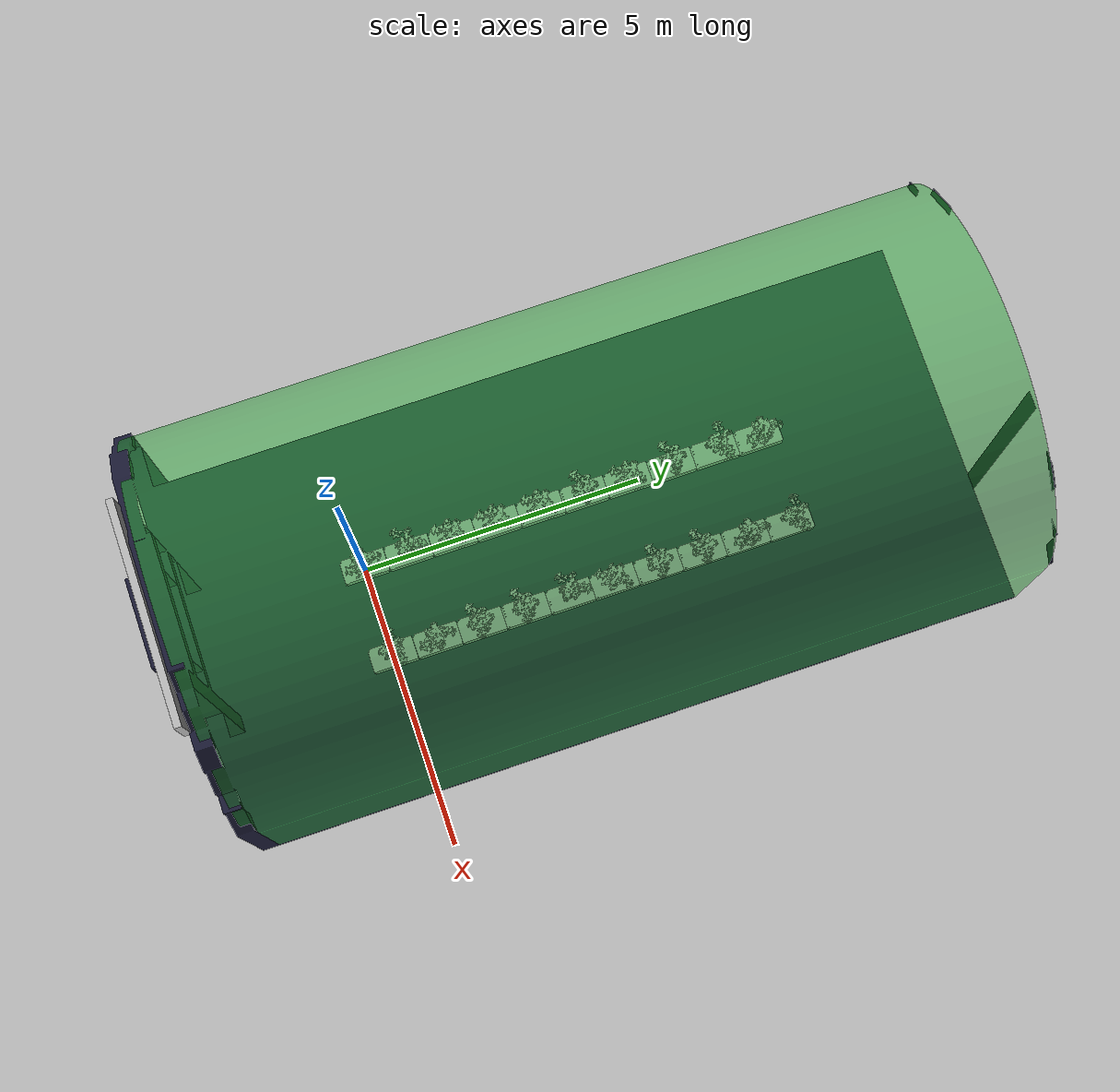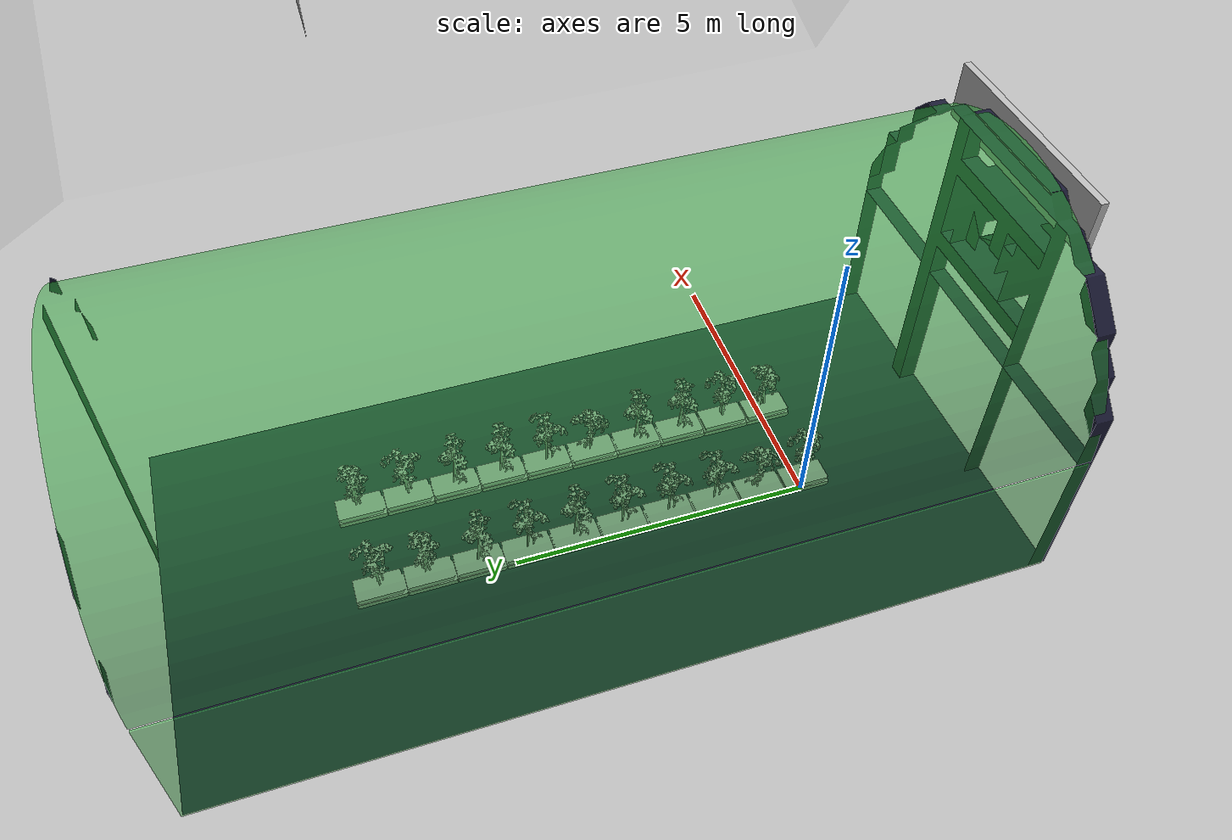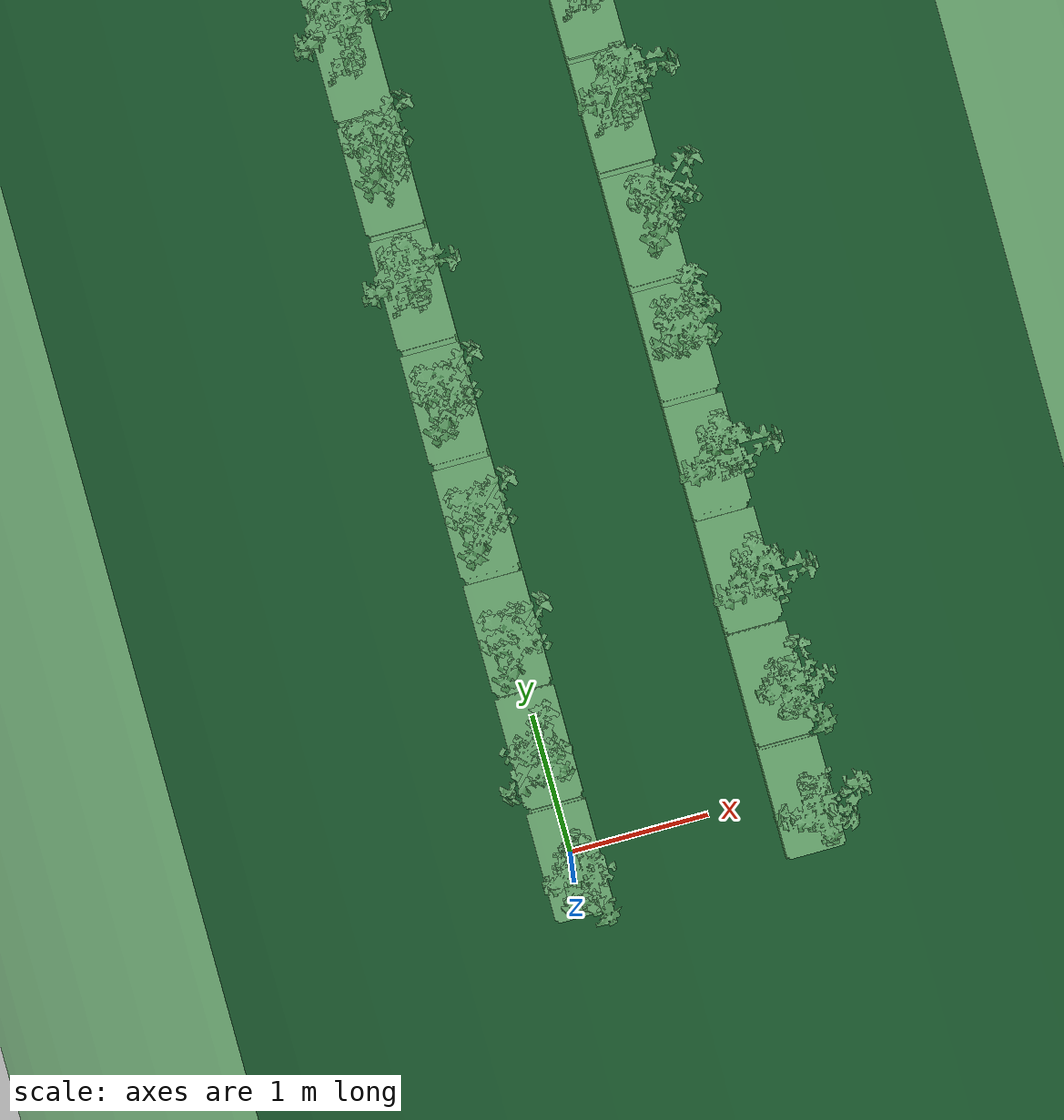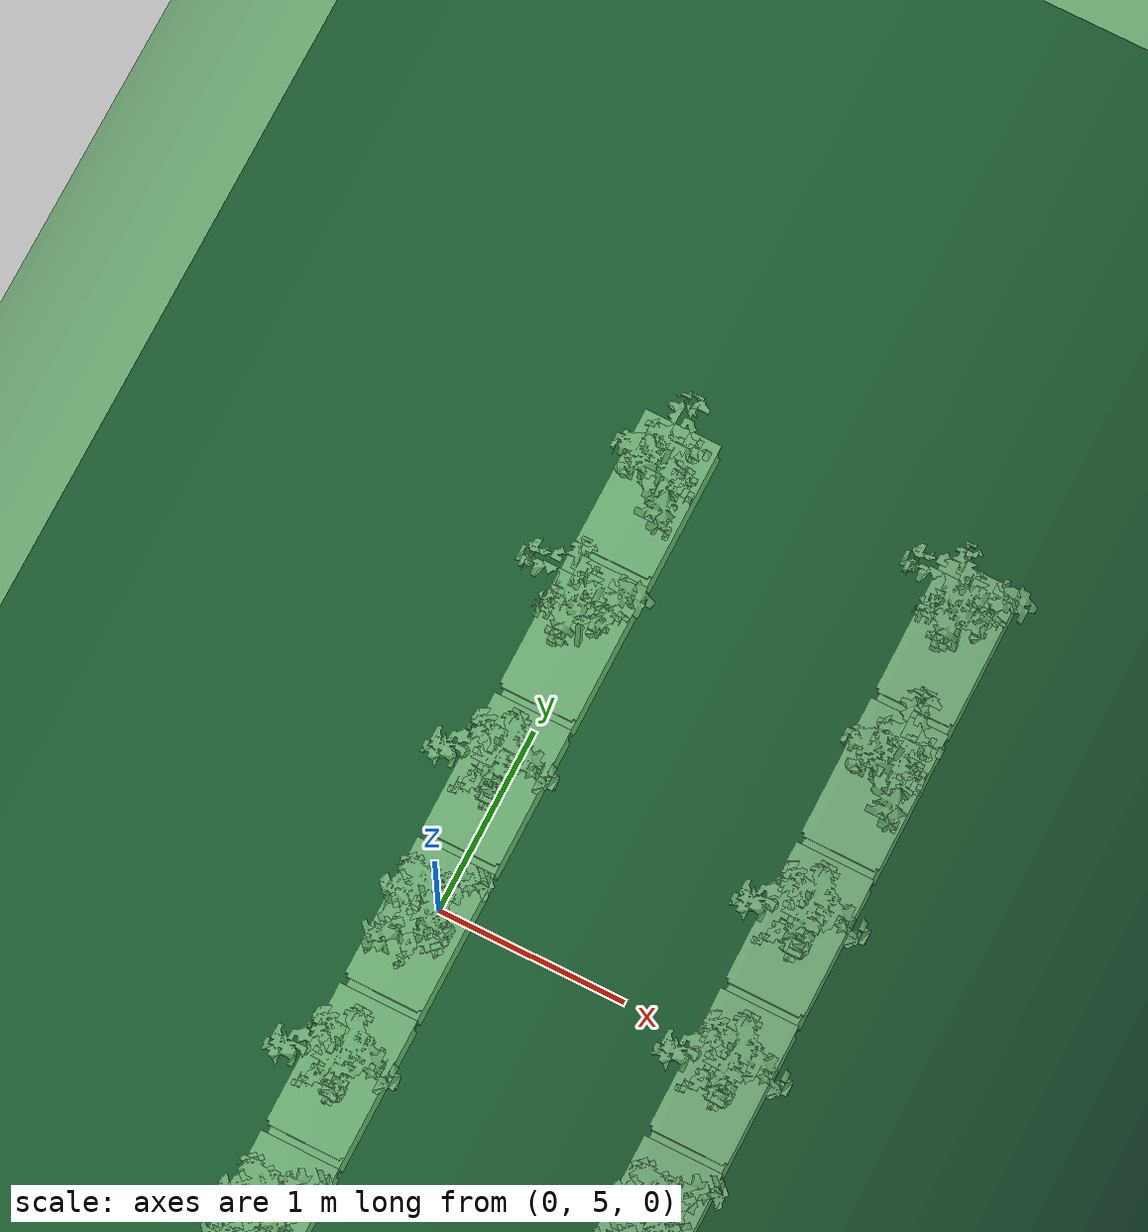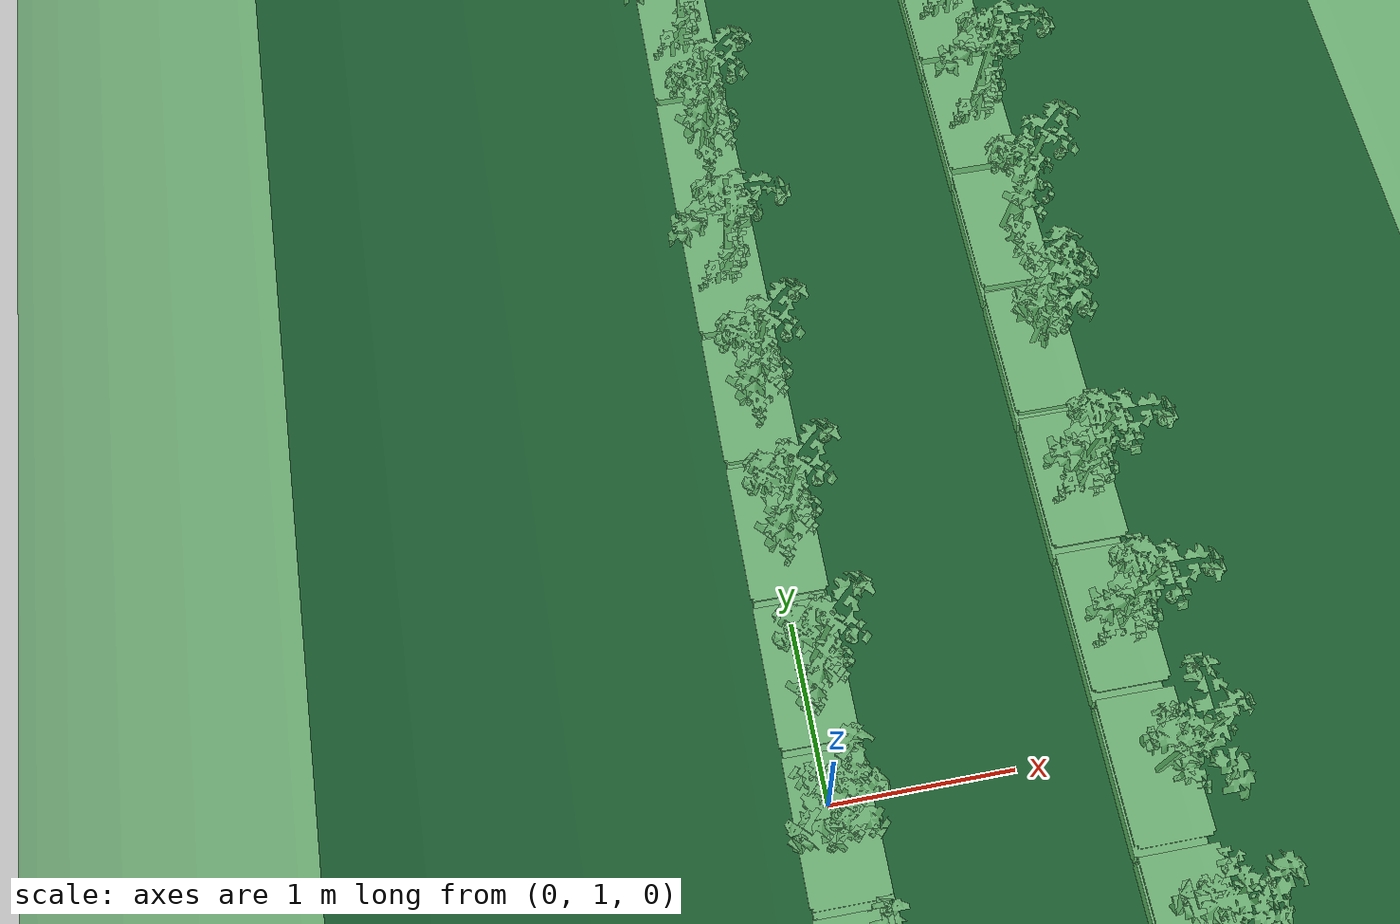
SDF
<sdf version="1.6">
 <world name="default">
  <physics name="default_physics" default="0" type="ode">
   <max_step_size>0.004</max_step_size>
   <real_time_factor>1</real_time_factor>
   <real_time_update_rate>250</real_time_update_rate>
   <ode>
    <solver>
     <iters>50</iters>
     <island_threads>4</island_threads>
     <type>quick</type>
     <sor>1.3</sor>
     <use_dynamic_moi_rescaling>0</use_dynamic_moi_rescaling>
    </solver>
    <constraints>
     <cfm>0</cfm>
     <erp>0.2</erp>
     <contact_max_correcting_vel>100</contact_max_correcting_vel>
     <contact_surface_layer>0.001</contact_surface_layer>
    </constraints>
   </ode>
  </physics>
  <scene>
   <shadows>0</shadows>
   <grid>0</grid>
   <sky><clouds><speed>4</speed></clouds></sky>
   <ambient>0.4 0.4 0.4 1</ambient>
   <background>0.7 0.7 0.7 1</background>
  </scene>
  <model name="farm">
   <static>1</static>
   <link name="link">
    <collision name="colision1"><geometry><box><size>2.32 1 1</size></box></geometry></collision>
    <visual name="visual1">
     <cast_shadows>0</cast_shadows>
     <geometry><mesh><uri>model://farm1/meshes/agriculture_world.dae</uri></mesh></geometry>
    </visual>
   </link>
   <pose>1.42405 -8.25 0.15 -0.02 0.029 -0</pose>
  </model>
  <model name="green_house">
   <static>1</static>
   <link name="link">
    <collision name="collision">
     <geometry>
      <mesh><scale>0.001 0.001 0.001</scale><uri>file://green_house/meshes/greenhouse_eyantra_glass.stl</uri></mesh>
     </geometry>
    </collision>
    <visual name="branch">
     <geometry>
      <mesh><scale>0.001 0.001 0.001</scale><uri>file://green_house/meshes/greenhouse_eyantra_glass.stl</uri></mesh>
     </geometry>
     <material>
      <script><name>Gazebo/GreenTransparent</name><uri>file://media/materials/scripts/gazebo.material</uri></script>
     </material>
    </visual>
   </link>
   <link name="link2">
    <collision name="collision2">
     <geometry>
      <mesh>
       <scale>0.001 0.001 0.001</scale>
       <uri>file://green_house/meshes/greenhouse_eyantra_skeleton.stl</uri>
      </mesh>
     </geometry>
    </collision>
    <visual name="branch2">
     <geometry>
      <mesh>
       <scale>0.001 0.001 0.001</scale>
       <uri>file://green_house/meshes/greenhouse_eyantra_skeleton.stl</uri>
      </mesh>
     </geometry>
     <material>
      <ambient>0.1 0.1 0.1 1</ambient>
      <diffuse>0.1 0.1 0.2 1</diffuse>
      <specular>0 0 0 0</specular>
      <emissive>0 0 0 1</emissive>
     </material>
    </visual>
   </link>
   <link name="link3">
    <pose>9.7 5.5 -0.2 3.14159 0.001593 3.14159</pose>
    <collision name="logo">
     <geometry><mesh><scale>400 400 400</scale><uri>file://green_house/meshes/logo2.dae</uri></mesh></geometry>
    </collision>
    <visual name="logo_c">
     <geometry><mesh><scale>400 400 400</scale><uri>file://green_house/meshes/logo2.dae</uri></mesh></geometry>
    </visual>
   </link>
   <joint name="logo" type="fixed"><child>link3</child><parent>link2</parent></joint>
   <pose>10.523 -2.987 0.1 1.57159 -0.001593 -3.14159</pose>
  </model>
  <gravity>0 0 -9.8</gravity>
  <magnetic_field>6e-06 2.3e-05 -4.2e-05</magnetic_field>
  <atmosphere type="adiabatic"/>
  <audio><device>default</device></audio>
  <spherical_coordinates>
   <surface_model>EARTH_WGS84</surface_model>
   <latitude_deg>0</latitude_deg>
   <longitude_deg>0</longitude_deg>
   <elevation>0</elevation>
   <heading_deg>0</heading_deg>
  </spherical_coordinates>
  <model name="plant00">
   <static>0</static>
   <link name="tomato_plant_link">
    <inertial>
     <mass>20</mass>
     <inertia><ixx>1</ixx><ixy>0</ixy><ixz>0</ixz><iyy>1</iyy><iyz>0</iyz><izz>1</izz></inertia>
    </inertial>
    <visual name="visual">
     <geometry><mesh><uri>model://tomato_plant/meshes/tomato_plant.obj</uri></mesh></geometry>
    </visual>
    <collision name="collision">
     <pose>0 0 0.05 0 -0 0</pose>
     <geometry><box><size>0.1 0.1 0.1</size></box></geometry>
    </collision>
   </link>
   <link name="t_link_0">
    <pose>0.176111 0.046061 0.713729 0 -0 0</pose>
    <inertial>
     <mass>0.1</mass>
     <inertia><ixx>1</ixx><ixy>0</ixy><ixz>0</ixz><iyy>1</iyy><iyz>0</iyz><izz>1</izz></inertia>
    </inertial>
    <collision name="collision"><geometry><sphere><radius>0.02</radius></sphere></geometry></collision>
    <visual name="visual">
     <geometry><mesh><uri>model://green_tomato/meshes/green_tomato.obj</uri></mesh></geometry>
    </visual>
   </link>
   <joint name="t_joint_0" type="fixed">
    <parent>tomato_plant_link</parent>
    <child>t_link_0</child>
    <axis>
     <xyz>0 0 1</xyz>
     <use_parent_model_frame>1</use_parent_model_frame>
     <limit><lower>-1e+16</lower><upper>1e+16</upper></limit>
    </axis>
    <sensor name="force_torque" type="force_torque">
     <always_on>1</always_on>
     <update_rate>250</update_rate>
     <plugin name="breakable_0" filename="libBreakableJointPlugin.so">
      <breaking_force_N>10</breaking_force_N>
     </plugin>
    </sensor>
   </joint>
   <link name="t_link_1">
    <pose>0.063172 0.108629 0.685474 0 -0 0</pose>
    <inertial>
     <mass>0.1</mass>
     <inertia><ixx>1</ixx><ixy>0</ixy><ixz>0</ixz><iyy>1</iyy><iyz>0</iyz><izz>1</izz></inertia>
    </inertial>
    <collision name="collision"><geometry><sphere><radius>0.02</radius></sphere></geometry></collision>
    <visual name="visual">
     <geometry><mesh><uri>model://green_tomato/meshes/green_tomato.obj</uri></mesh></geometry>
    </visual>
   </link>
   <joint name="t_joint_1" type="fixed">
    <parent>tomato_plant_link</parent>
    <child>t_link_1</child>
    <axis>
     <xyz>0 0 1</xyz>
     <use_parent_model_frame>1</use_parent_model_frame>
     <limit><lower>-1e+16</lower><upper>1e+16</upper></limit>
    </axis>
    <sensor name="force_torque" type="force_torque">
     <always_on>1</always_on>
     <update_rate>250</update_rate>
     <plugin name="breakable_1" filename="libBreakableJointPlugin.so">
      <breaking_force_N>10</breaking_force_N>
     </plugin>
    </sensor>
   </joint>
   <link name="t_link_2">
    <pose>0.062027 -0.170581 0.614534 0 -0 0</pose>
    <inertial>
     <mass>0.1</mass>
     <inertia><ixx>1</ixx><ixy>0</ixy><ixz>0</ixz><iyy>1</iyy><iyz>0</iyz><izz>1</izz></inertia>
    </inertial>
    <collision name="collision"><geometry><sphere><radius>0.02</radius></sphere></geometry></collision>
    <visual name="visual">
     <geometry><mesh><uri>model://green_tomato/meshes/green_tomato.obj</uri></mesh></geometry>
    </visual>
   </link>
   <joint name="t_joint_2" type="fixed">
    <parent>tomato_plant_link</parent>
    <child>t_link_2</child>
    <axis>
     <xyz>0 0 1</xyz>
     <use_parent_model_frame>1</use_parent_model_frame>
     <limit><lower>-1e+16</lower><upper>1e+16</upper></limit>
    </axis>
    <sensor name="force_torque" type="force_torque">
     <always_on>1</always_on>
     <update_rate>250</update_rate>
     <plugin name="breakable_2" filename="libBreakableJointPlugin.so">
      <breaking_force_N>10</breaking_force_N>
     </plugin>
    </sensor>
   </joint>
   <link name="t_link_3">
    <pose>0.114746 0.0304 0.926457 0 -0 0</pose>
    <inertial>
     <mass>0.1</mass>
     <inertia><ixx>1</ixx><ixy>0</ixy><ixz>0</ixz><iyy>1</iyy><iyz>0</iyz><izz>1</izz></inertia>
    </inertial>
    <collision name="collision"><geometry><sphere><radius>0.02</radius></sphere></geometry></collision>
    <visual name="visual">
     <geometry><mesh><uri>model://yellow_tomato/meshes/yellow_tomato.obj</uri></mesh></geometry>
    </visual>
   </link>
   <joint name="t_joint_3" type="fixed">
    <parent>tomato_plant_link</parent>
    <child>t_link_3</child>
    <axis>
     <xyz>0 0 1</xyz>
     <use_parent_model_frame>1</use_parent_model_frame>
     <limit><lower>-1e+16</lower><upper>1e+16</upper></limit>
    </axis>
    <sensor name="force_torque" type="force_torque">
     <always_on>1</always_on>
     <update_rate>250</update_rate>
     <plugin name="breakable_3" filename="libBreakableJointPlugin.so">
      <breaking_force_N>10</breaking_force_N>
     </plugin>
    </sensor>
   </joint>
   <link name="t_link_4">
    <pose>0.003426 0.147925 0.840454 0 -0 0</pose>
    <inertial>
     <mass>0.1</mass>
     <inertia><ixx>1</ixx><ixy>0</ixy><ixz>0</ixz><iyy>1</iyy><iyz>0</iyz><izz>1</izz></inertia>
    </inertial>
    <collision name="collision"><geometry><sphere><radius>0.02</radius></sphere></geometry></collision>
    <visual name="visual">
     <geometry><mesh><uri>model://yellow_tomato/meshes/yellow_tomato.obj</uri></mesh></geometry>
    </visual>
   </link>
   <joint name="t_joint_4" type="fixed">
    <parent>tomato_plant_link</parent>
    <child>t_link_4</child>
    <axis>
     <xyz>0 0 1</xyz>
     <use_parent_model_frame>1</use_parent_model_frame>
     <limit><lower>-1e+16</lower><upper>1e+16</upper></limit>
    </axis>
    <sensor name="force_torque" type="force_torque">
     <always_on>1</always_on>
     <update_rate>250</update_rate>
     <plugin name="breakable_4" filename="libBreakableJointPlugin.so">
      <breaking_force_N>10</breaking_force_N>
     </plugin>
    </sensor>
   </joint>
   <link name="t_link_5">
    <pose>-0.12391 0.091553 0.91111 0 -0 0</pose>
    <inertial>
     <mass>0.1</mass>
     <inertia><ixx>1</ixx><ixy>0</ixy><ixz>0</ixz><iyy>1</iyy><iyz>0</iyz><izz>1</izz></inertia>
    </inertial>
    <collision name="collision"><geometry><sphere><radius>0.02</radius></sphere></geometry></collision>
    <visual name="visual">
     <geometry><mesh><uri>model://yellow_tomato/meshes/yellow_tomato.obj</uri></mesh></geometry>
    </visual>
   </link>
   <joint name="t_joint_5" type="fixed">
    <parent>tomato_plant_link</parent>
    <child>t_link_5</child>
    <axis>
     <xyz>0 0 1</xyz>
     <use_parent_model_frame>1</use_parent_model_frame>
     <limit><lower>-1e+16</lower><upper>1e+16</upper></limit>
    </axis>
    <sensor name="force_torque" type="force_torque">
     <always_on>1</always_on>
     <update_rate>250</update_rate>
     <plugin name="breakable_5" filename="libBreakableJointPlugin.so">
      <breaking_force_N>10</breaking_force_N>
     </plugin>
    </sensor>
   </joint>
   <link name="t_link_6">
    <pose>-0.23014 -0.132697 0.911579 0 -0 0</pose>
    <inertial>
     <mass>0.1</mass>
     <inertia><ixx>1</ixx><ixy>0</ixy><ixz>0</ixz><iyy>1</iyy><iyz>0</iyz><izz>1</izz></inertia>
    </inertial>
    <collision name="collision"><geometry><sphere><radius>0.03</radius></sphere></geometry></collision>
    <visual name="visual">
     <geometry><mesh><uri>model://red_tomato/meshes/red_tomato.obj</uri></mesh></geometry>
    </visual>
   </link>
   <joint name="t_joint_6" type="fixed">
    <parent>tomato_plant_link</parent>
    <child>t_link_6</child>
    <axis>
     <xyz>0 0 1</xyz>
     <use_parent_model_frame>1</use_parent_model_frame>
     <limit><lower>-1e+16</lower><upper>1e+16</upper></limit>
    </axis>
    <sensor name="force_torque" type="force_torque">
     <always_on>1</always_on>
     <update_rate>250</update_rate>
     <plugin name="breakable_6" filename="libBreakableJointPlugin.so">
      <breaking_force_N>10</breaking_force_N>
     </plugin>
    </sensor>
   </joint>
   <link name="t_link_7">
    <pose>-0.139776 -0.09326 0.950185 0 -0 0</pose>
    <inertial>
     <mass>0.1</mass>
     <inertia><ixx>1</ixx><ixy>0</ixy><ixz>0</ixz><iyy>1</iyy><iyz>0</iyz><izz>1</izz></inertia>
    </inertial>
    <collision name="collision"><geometry><sphere><radius>0.03</radius></sphere></geometry></collision>
    <visual name="visual">
     <geometry><mesh><uri>model://red_tomato/meshes/red_tomato.obj</uri></mesh></geometry>
    </visual>
   </link>
   <joint name="t_joint_7" type="fixed">
    <parent>tomato_plant_link</parent>
    <child>t_link_7</child>
    <axis>
     <xyz>0 0 1</xyz>
     <use_parent_model_frame>1</use_parent_model_frame>
     <limit><lower>-1e+16</lower><upper>1e+16</upper></limit>
    </axis>
    <sensor name="force_torque" type="force_torque">
     <always_on>1</always_on>
     <update_rate>250</update_rate>
     <plugin name="breakable_7" filename="libBreakableJointPlugin.so">
      <breaking_force_N>10</breaking_force_N>
     </plugin>
    </sensor>
   </joint>
   <link name="t_link_8">
    <pose>0.284181 -0.063758 1.01928 0 -0 0</pose>
    <inertial>
     <mass>0.1</mass>
     <inertia><ixx>1</ixx><ixy>0</ixy><ixz>0</ixz><iyy>1</iyy><iyz>0</iyz><izz>1</izz></inertia>
    </inertial>
    <collision name="collision"><geometry><sphere><radius>0.03</radius></sphere></geometry></collision>
    <visual name="visual">
     <geometry><mesh><uri>model://red_tomato/meshes/red_tomato.obj</uri></mesh></geometry>
    </visual>
   </link>
   <joint name="t_joint_8" type="fixed">
    <parent>tomato_plant_link</parent>
    <child>t_link_8</child>
    <axis>
     <xyz>0 0 1</xyz>
     <use_parent_model_frame>1</use_parent_model_frame>
     <limit><lower>-1e+16</lower><upper>1e+16</upper></limit>
    </axis>
    <sensor name="force_torque" type="force_torque">
     <always_on>1</always_on>
     <update_rate>250</update_rate>
     <plugin name="breakable_8" filename="libBreakableJointPlugin.so">
      <breaking_force_N>10</breaking_force_N>
     </plugin>
    </sensor>
   </joint>
   <link name="t_link_9">
    <pose>0.055319 -0.176349 1.06525 0 -0 0</pose>
    <inertial>
     <mass>0.1</mass>
     <inertia><ixx>1</ixx><ixy>0</ixy><ixz>0</ixz><iyy>1</iyy><iyz>0</iyz><izz>1</izz></inertia>
    </inertial>
    <collision name="collision"><geometry><sphere><radius>0.03</radius></sphere></geometry></collision>
    <visual name="visual">
     <geometry><mesh><uri>model://red_tomato/meshes/red_tomato.obj</uri></mesh></geometry>
    </visual>
   </link>
   <joint name="t_joint_9" type="fixed">
    <parent>tomato_plant_link</parent>
    <child>t_link_9</child>
    <axis>
     <xyz>0 0 1</xyz>
     <use_parent_model_frame>1</use_parent_model_frame>
     <limit><lower>-1e+16</lower><upper>1e+16</upper></limit>
    </axis>
    <sensor name="force_torque" type="force_torque">
     <always_on>1</always_on>
     <update_rate>250</update_rate>
     <plugin name="breakable_9" filename="libBreakableJointPlugin.so">
      <breaking_force_N>10</breaking_force_N>
     </plugin>
    </sensor>
   </joint>
   <pose>0.018323 0.010007 0.114245 0.001554 0.000867 1.56035</pose>
  </model>
  <model name="trough00">
   <static>1</static>
   <link name="trough_link">
    <visual name="visual"><geometry><mesh><uri>model://trough/meshes/truf.obj</uri></mesh></geometry></visual>
   </link>
   <pose>0 0 0.18 1.57 -0 1.57</pose>
  </model>
  <model name="plant01">
   <static>0</static>
   <link name="tomato_plant_link">
    <inertial>
     <mass>20</mass>
     <inertia><ixx>1</ixx><ixy>0</ixy><ixz>0</ixz><iyy>1</iyy><iyz>0</iyz><izz>1</izz></inertia>
    </inertial>
    <visual name="visual">
     <geometry><mesh><uri>model://tomato_plant/meshes/tomato_plant.obj</uri></mesh></geometry>
    </visual>
    <collision name="collision">
     <pose>0 0 0.05 0 -0 0</pose>
     <geometry><box><size>0.1 0.1 0.1</size></box></geometry>
    </collision>
   </link>
   <link name="t_link_0">
    <pose>0.176111 0.046061 0.713729 0 -0 0</pose>
    <inertial>
     <mass>0.1</mass>
     <inertia><ixx>1</ixx><ixy>0</ixy><ixz>0</ixz><iyy>1</iyy><iyz>0</iyz><izz>1</izz></inertia>
    </inertial>
    <collision name="collision"><geometry><sphere><radius>0.02</radius></sphere></geometry></collision>
    <visual name="visual">
     <geometry><mesh><uri>model://green_tomato/meshes/green_tomato.obj</uri></mesh></geometry>
    </visual>
   </link>
   <joint name="t_joint_0" type="fixed">
    <parent>tomato_plant_link</parent>
    <child>t_link_0</child>
    <axis>
     <xyz>0 0 1</xyz>
     <use_parent_model_frame>1</use_parent_model_frame>
     <limit><lower>-1e+16</lower><upper>1e+16</upper></limit>
    </axis>
    <sensor name="force_torque" type="force_torque">
     <always_on>1</always_on>
     <update_rate>250</update_rate>
     <plugin name="breakable_0" filename="libBreakableJointPlugin.so">
      <breaking_force_N>10</breaking_force_N>
     </plugin>
    </sensor>
   </joint>
   <link name="t_link_1">
    <pose>0.063172 0.108629 0.685474 0 -0 0</pose>
    <inertial>
     <mass>0.1</mass>
     <inertia><ixx>1</ixx><ixy>0</ixy><ixz>0</ixz><iyy>1</iyy><iyz>0</iyz><izz>1</izz></inertia>
    </inertial>
    <collision name="collision"><geometry><sphere><radius>0.02</radius></sphere></geometry></collision>
    <visual name="visual">
     <geometry><mesh><uri>model://green_tomato/meshes/green_tomato.obj</uri></mesh></geometry>
    </visual>
   </link>
   <joint name="t_joint_1" type="fixed">
    <parent>tomato_plant_link</parent>
    <child>t_link_1</child>
    <axis>
     <xyz>0 0 1</xyz>
     <use_parent_model_frame>1</use_parent_model_frame>
     <limit><lower>-1e+16</lower><upper>1e+16</upper></limit>
    </axis>
    <sensor name="force_torque" type="force_torque">
     <always_on>1</always_on>
     <update_rate>250</update_rate>
     <plugin name="breakable_1" filename="libBreakableJointPlugin.so">
      <breaking_force_N>10</breaking_force_N>
     </plugin>
    </sensor>
   </joint>
   <link name="t_link_2">
    <pose>0.062027 -0.170581 0.614534 0 -0 0</pose>
    <inertial>
     <mass>0.1</mass>
     <inertia><ixx>1</ixx><ixy>0</ixy><ixz>0</ixz><iyy>1</iyy><iyz>0</iyz><izz>1</izz></inertia>
    </inertial>
    <collision name="collision"><geometry><sphere><radius>0.02</radius></sphere></geometry></collision>
    <visual name="visual">
     <geometry><mesh><uri>model://green_tomato/meshes/green_tomato.obj</uri></mesh></geometry>
    </visual>
   </link>
   <joint name="t_joint_2" type="fixed">
    <parent>tomato_plant_link</parent>
    <child>t_link_2</child>
    <axis>
     <xyz>0 0 1</xyz>
     <use_parent_model_frame>1</use_parent_model_frame>
     <limit><lower>-1e+16</lower><upper>1e+16</upper></limit>
    </axis>
    <sensor name="force_torque" type="force_torque">
     <always_on>1</always_on>
     <update_rate>250</update_rate>
     <plugin name="breakable_2" filename="libBreakableJointPlugin.so">
      <breaking_force_N>10</breaking_force_N>
     </plugin>
    </sensor>
   </joint>
   <link name="t_link_3">
    <pose>0.114746 0.0304 0.926457 0 -0 0</pose>
    <inertial>
     <mass>0.1</mass>
     <inertia><ixx>1</ixx><ixy>0</ixy><ixz>0</ixz><iyy>1</iyy><iyz>0</iyz><izz>1</izz></inertia>
    </inertial>
    <collision name="collision"><geometry><sphere><radius>0.02</radius></sphere></geometry></collision>
    <visual name="visual">
     <geometry><mesh><uri>model://yellow_tomato/meshes/yellow_tomato.obj</uri></mesh></geometry>
    </visual>
   </link>
   <joint name="t_joint_3" type="fixed">
    <parent>tomato_plant_link</parent>
    <child>t_link_3</child>
    <axis>
     <xyz>0 0 1</xyz>
     <use_parent_model_frame>1</use_parent_model_frame>
     <limit><lower>-1e+16</lower><upper>1e+16</upper></limit>
    </axis>
    <sensor name="force_torque" type="force_torque">
     <always_on>1</always_on>
     <update_rate>250</update_rate>
     <plugin name="breakable_3" filename="libBreakableJointPlugin.so">
      <breaking_force_N>10</breaking_force_N>
     </plugin>
    </sensor>
   </joint>
   <link name="t_link_4">
    <pose>0.003426 0.147925 0.840454 0 -0 0</pose>
    <inertial>
     <mass>0.1</mass>
     <inertia><ixx>1</ixx><ixy>0</ixy><ixz>0</ixz><iyy>1</iyy><iyz>0</iyz><izz>1</izz></inertia>
    </inertial>
    <collision name="collision"><geometry><sphere><radius>0.02</radius></sphere></geometry></collision>
    <visual name="visual">
     <geometry><mesh><uri>model://yellow_tomato/meshes/yellow_tomato.obj</uri></mesh></geometry>
    </visual>
   </link>
   <joint name="t_joint_4" type="fixed">
    <parent>tomato_plant_link</parent>
    <child>t_link_4</child>
    <axis>
     <xyz>0 0 1</xyz>
     <use_parent_model_frame>1</use_parent_model_frame>
     <limit><lower>-1e+16</lower><upper>1e+16</upper></limit>
    </axis>
    <sensor name="force_torque" type="force_torque">
     <always_on>1</always_on>
     <update_rate>250</update_rate>
     <plugin name="breakable_4" filename="libBreakableJointPlugin.so">
      <breaking_force_N>10</breaking_force_N>
     </plugin>
    </sensor>
   </joint>
   <link name="t_link_5">
    <pose>-0.12391 0.091553 0.91111 0 -0 0</pose>
    <inertial>
     <mass>0.1</mass>
     <inertia><ixx>1</ixx><ixy>0</ixy><ixz>0</ixz><iyy>1</iyy><iyz>0</iyz><izz>1</izz></inertia>
    </inertial>
    <collision name="collision"><geometry><sphere><radius>0.02</radius></sphere></geometry></collision>
    <visual name="visual">
     <geometry><mesh><uri>model://yellow_tomato/meshes/yellow_tomato.obj</uri></mesh></geometry>
    </visual>
   </link>
   <joint name="t_joint_5" type="fixed">
    <parent>tomato_plant_link</parent>
    <child>t_link_5</child>
    <axis>
     <xyz>0 0 1</xyz>
     <use_parent_model_frame>1</use_parent_model_frame>
     <limit><lower>-1e+16</lower><upper>1e+16</upper></limit>
    </axis>
    <sensor name="force_torque" type="force_torque">
     <always_on>1</always_on>
     <update_rate>250</update_rate>
     <plugin name="breakable_5" filename="libBreakableJointPlugin.so">
      <breaking_force_N>10</breaking_force_N>
     </plugin>
    </sensor>
   </joint>
   <link name="t_link_6">
    <pose>-0.23014 -0.132697 0.911579 0 -0 0</pose>
    <inertial>
     <mass>0.1</mass>
     <inertia><ixx>1</ixx><ixy>0</ixy><ixz>0</ixz><iyy>1</iyy><iyz>0</iyz><izz>1</izz></inertia>
    </inertial>
    <collision name="collision"><geometry><sphere><radius>0.03</radius></sphere></geometry></collision>
    <visual name="visual">
     <geometry><mesh><uri>model://red_tomato/meshes/red_tomato.obj</uri></mesh></geometry>
    </visual>
   </link>
   <joint name="t_joint_6" type="fixed">
    <parent>tomato_plant_link</parent>
    <child>t_link_6</child>
    <axis>
     <xyz>0 0 1</xyz>
     <use_parent_model_frame>1</use_parent_model_frame>
     <limit><lower>-1e+16</lower><upper>1e+16</upper></limit>
    </axis>
    <sensor name="force_torque" type="force_torque">
     <always_on>1</always_on>
     <update_rate>250</update_rate>
     <plugin name="breakable_6" filename="libBreakableJointPlugin.so">
      <breaking_force_N>10</breaking_force_N>
     </plugin>
    </sensor>
   </joint>
   <link name="t_link_7">
    <pose>-0.139776 -0.09326 0.950185 0 -0 0</pose>
    <inertial>
     <mass>0.1</mass>
     <inertia><ixx>1</ixx><ixy>0</ixy><ixz>0</ixz><iyy>1</iyy><iyz>0</iyz><izz>1</izz></inertia>
    </inertial>
    <collision name="collision"><geometry><sphere><radius>0.03</radius></sphere></geometry></collision>
    <visual name="visual">
     <geometry><mesh><uri>model://red_tomato/meshes/red_tomato.obj</uri></mesh></geometry>
    </visual>
   </link>
   <joint name="t_joint_7" type="fixed">
    <parent>tomato_plant_link</parent>
    <child>t_link_7</child>
    <axis>
     <xyz>0 0 1</xyz>
     <use_parent_model_frame>1</use_parent_model_frame>
     <limit><lower>-1e+16</lower><upper>1e+16</upper></limit>
    </axis>
    <sensor name="force_torque" type="force_torque">
     <always_on>1</always_on>
     <update_rate>250</update_rate>
     <plugin name="breakable_7" filename="libBreakableJointPlugin.so">
      <breaking_force_N>10</breaking_force_N>
     </plugin>
    </sensor>
   </joint>
   <link name="t_link_8">
    <pose>0.284181 -0.063758 1.01928 0 -0 0</pose>
    <inertial>
     <mass>0.1</mass>
     <inertia><ixx>1</ixx><ixy>0</ixy><ixz>0</ixz><iyy>1</iyy><iyz>0</iyz><izz>1</izz></inertia>
    </inertial>
    <collision name="collision"><geometry><sphere><radius>0.03</radius></sphere></geometry></collision>
    <visual name="visual">
     <geometry><mesh><uri>model://red_tomato/meshes/red_tomato.obj</uri></mesh></geometry>
    </visual>
   </link>
   <joint name="t_joint_8" type="fixed">
    <parent>tomato_plant_link</parent>
    <child>t_link_8</child>
    <axis>
     <xyz>0 0 1</xyz>
     <use_parent_model_frame>1</use_parent_model_frame>
     <limit><lower>-1e+16</lower><upper>1e+16</upper></limit>
    </axis>
    <sensor name="force_torque" type="force_torque">
     <always_on>1</always_on>
     <update_rate>250</update_rate>
     <plugin name="breakable_8" filename="libBreakableJointPlugin.so">
      <breaking_force_N>10</breaking_force_N>
     </plugin>
    </sensor>
   </joint>
   <link name="t_link_9">
    <pose>0.055319 -0.176349 1.06525 0 -0 0</pose>
    <inertial>
     <mass>0.1</mass>
     <inertia><ixx>1</ixx><ixy>0</ixy><ixz>0</ixz><iyy>1</iyy><iyz>0</iyz><izz>1</izz></inertia>
    </inertial>
    <collision name="collision"><geometry><sphere><radius>0.03</radius></sphere></geometry></collision>
    <visual name="visual">
     <geometry><mesh><uri>model://red_tomato/meshes/red_tomato.obj</uri></mesh></geometry>
    </visual>
   </link>
   <joint name="t_joint_9" type="fixed">
    <parent>tomato_plant_link</parent>
    <child>t_link_9</child>
    <axis>
     <xyz>0 0 1</xyz>
     <use_parent_model_frame>1</use_parent_model_frame>
     <limit><lower>-1e+16</lower><upper>1e+16</upper></limit>
    </axis>
    <sensor name="force_torque" type="force_torque">
     <always_on>1</always_on>
     <update_rate>250</update_rate>
     <plugin name="breakable_9" filename="libBreakableJointPlugin.so">
      <breaking_force_N>10</breaking_force_N>
     </plugin>
    </sensor>
   </joint>
   <pose>0.022043 0.808835 0.11372 -0.000579 -0.001647 -2.35786</pose>
  </model>
  <model name="trough01">
   <static>1</static>
   <link name="trough_link">
    <visual name="visual"><geometry><mesh><uri>model://trough/meshes/truf.obj</uri></mesh></geometry></visual>
   </link>
   <pose>0 0.8 0.18 1.57 -0 1.57</pose>
  </model>
  <model name="plant02">
   <static>0</static>
   <link name="tomato_plant_link">
    <inertial>
     <mass>20</mass>
     <inertia><ixx>1</ixx><ixy>0</ixy><ixz>0</ixz><iyy>1</iyy><iyz>0</iyz><izz>1</izz></inertia>
    </inertial>
    <visual name="visual">
     <geometry><mesh><uri>model://tomato_plant/meshes/tomato_plant.obj</uri></mesh></geometry>
    </visual>
    <collision name="collision">
     <pose>0 0 0.05 0 -0 0</pose>
     <geometry><box><size>0.1 0.1 0.1</size></box></geometry>
    </collision>
   </link>
   <link name="t_link_0">
    <pose>0.176111 0.046061 0.713729 0 -0 0</pose>
    <inertial>
     <mass>0.1</mass>
     <inertia><ixx>1</ixx><ixy>0</ixy><ixz>0</ixz><iyy>1</iyy><iyz>0</iyz><izz>1</izz></inertia>
    </inertial>
    <collision name="collision"><geometry><sphere><radius>0.02</radius></sphere></geometry></collision>
    <visual name="visual">
     <geometry><mesh><uri>model://green_tomato/meshes/green_tomato.obj</uri></mesh></geometry>
    </visual>
   </link>
   <joint name="t_joint_0" type="fixed">
    <parent>tomato_plant_link</parent>
    <child>t_link_0</child>
    <axis>
     <xyz>0 0 1</xyz>
     <use_parent_model_frame>1</use_parent_model_frame>
     <limit><lower>-1e+16</lower><upper>1e+16</upper></limit>
    </axis>
    <sensor name="force_torque" type="force_torque">
     <always_on>1</always_on>
     <update_rate>250</update_rate>
     <plugin name="breakable_0" filename="libBreakableJointPlugin.so">
      <breaking_force_N>10</breaking_force_N>
     </plugin>
    </sensor>
   </joint>
   <link name="t_link_1">
    <pose>0.063172 0.108629 0.685474 0 -0 0</pose>
    <inertial>
     <mass>0.1</mass>
     <inertia><ixx>1</ixx><ixy>0</ixy><ixz>0</ixz><iyy>1</iyy><iyz>0</iyz><izz>1</izz></inertia>
    </inertial>
    <collision name="collision"><geometry><sphere><radius>0.02</radius></sphere></geometry></collision>
    <visual name="visual">
     <geometry><mesh><uri>model://green_tomato/meshes/green_tomato.obj</uri></mesh></geometry>
    </visual>
   </link>
   <joint name="t_joint_1" type="fixed">
    <parent>tomato_plant_link</parent>
    <child>t_link_1</child>
    <axis>
     <xyz>0 0 1</xyz>
     <use_parent_model_frame>1</use_parent_model_frame>
     <limit><lower>-1e+16</lower><upper>1e+16</upper></limit>
    </axis>
    <sensor name="force_torque" type="force_torque">
     <always_on>1</always_on>
     <update_rate>250</update_rate>
     <plugin name="breakable_1" filename="libBreakableJointPlugin.so">
      <breaking_force_N>10</breaking_force_N>
     </plugin>
    </sensor>
   </joint>
   <link name="t_link_2">
    <pose>0.062027 -0.170581 0.614534 0 -0 0</pose>
    <inertial>
     <mass>0.1</mass>
     <inertia><ixx>1</ixx><ixy>0</ixy><ixz>0</ixz><iyy>1</iyy><iyz>0</iyz><izz>1</izz></inertia>
    </inertial>
    <collision name="collision"><geometry><sphere><radius>0.02</radius></sphere></geometry></collision>
    <visual name="visual">
     <geometry><mesh><uri>model://green_tomato/meshes/green_tomato.obj</uri></mesh></geometry>
    </visual>
   </link>
   <joint name="t_joint_2" type="fixed">
    <parent>tomato_plant_link</parent>
    <child>t_link_2</child>
    <axis>
     <xyz>0 0 1</xyz>
     <use_parent_model_frame>1</use_parent_model_frame>
     <limit><lower>-1e+16</lower><upper>1e+16</upper></limit>
    </axis>
    <sensor name="force_torque" type="force_torque">
     <always_on>1</always_on>
     <update_rate>250</update_rate>
     <plugin name="breakable_2" filename="libBreakableJointPlugin.so">
      <breaking_force_N>10</breaking_force_N>
     </plugin>
    </sensor>
   </joint>
   <link name="t_link_3">
    <pose>0.114746 0.0304 0.926457 0 -0 0</pose>
    <inertial>
     <mass>0.1</mass>
     <inertia><ixx>1</ixx><ixy>0</ixy><ixz>0</ixz><iyy>1</iyy><iyz>0</iyz><izz>1</izz></inertia>
    </inertial>
    <collision name="collision"><geometry><sphere><radius>0.02</radius></sphere></geometry></collision>
    <visual name="visual">
     <geometry><mesh><uri>model://yellow_tomato/meshes/yellow_tomato.obj</uri></mesh></geometry>
    </visual>
   </link>
   <joint name="t_joint_3" type="fixed">
    <parent>tomato_plant_link</parent>
    <child>t_link_3</child>
    <axis>
     <xyz>0 0 1</xyz>
     <use_parent_model_frame>1</use_parent_model_frame>
     <limit><lower>-1e+16</lower><upper>1e+16</upper></limit>
    </axis>
    <sensor name="force_torque" type="force_torque">
     <always_on>1</always_on>
     <update_rate>250</update_rate>
     <plugin name="breakable_3" filename="libBreakableJointPlugin.so">
      <breaking_force_N>10</breaking_force_N>
     </plugin>
    </sensor>
   </joint>
   <link name="t_link_4">
    <pose>0.003426 0.147925 0.840454 0 -0 0</pose>
    <inertial>
     <mass>0.1</mass>
     <inertia><ixx>1</ixx><ixy>0</ixy><ixz>0</ixz><iyy>1</iyy><iyz>0</iyz><izz>1</izz></inertia>
    </inertial>
    <collision name="collision"><geometry><sphere><radius>0.02</radius></sphere></geometry></collision>
    <visual name="visual">
     <geometry><mesh><uri>model://yellow_tomato/meshes/yellow_tomato.obj</uri></mesh></geometry>
    </visual>
   </link>
   <joint name="t_joint_4" type="fixed">
    <parent>tomato_plant_link</parent>
    <child>t_link_4</child>
    <axis>
     <xyz>0 0 1</xyz>
     <use_parent_model_frame>1</use_parent_model_frame>
     <limit><lower>-1e+16</lower><upper>1e+16</upper></limit>
    </axis>
    <sensor name="force_torque" type="force_torque">
     <always_on>1</always_on>
     <update_rate>250</update_rate>
     <plugin name="breakable_4" filename="libBreakableJointPlugin.so">
      <breaking_force_N>10</breaking_force_N>
     </plugin>
    </sensor>
   </joint>
   <link name="t_link_5">
    <pose>-0.12391 0.091553 0.91111 0 -0 0</pose>
    <inertial>
     <mass>0.1</mass>
     <inertia><ixx>1</ixx><ixy>0</ixy><ixz>0</ixz><iyy>1</iyy><iyz>0</iyz><izz>1</izz></inertia>
    </inertial>
    <collision name="collision"><geometry><sphere><radius>0.02</radius></sphere></geometry></collision>
    <visual name="visual">
     <geometry><mesh><uri>model://yellow_tomato/meshes/yellow_tomato.obj</uri></mesh></geometry>
    </visual>
   </link>
   <joint name="t_joint_5" type="fixed">
    <parent>tomato_plant_link</parent>
    <child>t_link_5</child>
    <axis>
     <xyz>0 0 1</xyz>
     <use_parent_model_frame>1</use_parent_model_frame>
     <limit><lower>-1e+16</lower><upper>1e+16</upper></limit>
    </axis>
    <sensor name="force_torque" type="force_torque">
     <always_on>1</always_on>
     <update_rate>250</update_rate>
     <plugin name="breakable_5" filename="libBreakableJointPlugin.so">
      <breaking_force_N>10</breaking_force_N>
     </plugin>
    </sensor>
   </joint>
   <link name="t_link_6">
    <pose>-0.23014 -0.132697 0.911579 0 -0 0</pose>
    <inertial>
     <mass>0.1</mass>
     <inertia><ixx>1</ixx><ixy>0</ixy><ixz>0</ixz><iyy>1</iyy><iyz>0</iyz><izz>1</izz></inertia>
    </inertial>
    <collision name="collision"><geometry><sphere><radius>0.03</radius></sphere></geometry></collision>
    <visual name="visual">
     <geometry><mesh><uri>model://red_tomato/meshes/red_tomato.obj</uri></mesh></geometry>
    </visual>
   </link>
   <joint name="t_joint_6" type="fixed">
    <parent>tomato_plant_link</parent>
    <child>t_link_6</child>
    <axis>
     <xyz>0 0 1</xyz>
     <use_parent_model_frame>1</use_parent_model_frame>
     <limit><lower>-1e+16</lower><upper>1e+16</upper></limit>
    </axis>
    <sensor name="force_torque" type="force_torque">
     <always_on>1</always_on>
     <update_rate>250</update_rate>
     <plugin name="breakable_6" filename="libBreakableJointPlugin.so">
      <breaking_force_N>10</breaking_force_N>
     </plugin>
    </sensor>
   </joint>
   <link name="t_link_7">
    <pose>-0.139776 -0.09326 0.950185 0 -0 0</pose>
    <inertial>
     <mass>0.1</mass>
     <inertia><ixx>1</ixx><ixy>0</ixy><ixz>0</ixz><iyy>1</iyy><iyz>0</iyz><izz>1</izz></inertia>
    </inertial>
    <collision name="collision"><geometry><sphere><radius>0.03</radius></sphere></geometry></collision>
    <visual name="visual">
     <geometry><mesh><uri>model://red_tomato/meshes/red_tomato.obj</uri></mesh></geometry>
    </visual>
   </link>
   <joint name="t_joint_7" type="fixed">
    <parent>tomato_plant_link</parent>
    <child>t_link_7</child>
    <axis>
     <xyz>0 0 1</xyz>
     <use_parent_model_frame>1</use_parent_model_frame>
     <limit><lower>-1e+16</lower><upper>1e+16</upper></limit>
    </axis>
    <sensor name="force_torque" type="force_torque">
     <always_on>1</always_on>
     <update_rate>250</update_rate>
     <plugin name="breakable_7" filename="libBreakableJointPlugin.so">
      <breaking_force_N>10</breaking_force_N>
     </plugin>
    </sensor>
   </joint>
   <link name="t_link_8">
    <pose>0.284181 -0.063758 1.01928 0 -0 0</pose>
    <inertial>
     <mass>0.1</mass>
     <inertia><ixx>1</ixx><ixy>0</ixy><ixz>0</ixz><iyy>1</iyy><iyz>0</iyz><izz>1</izz></inertia>
    </inertial>
    <collision name="collision"><geometry><sphere><radius>0.03</radius></sphere></geometry></collision>
    <visual name="visual">
     <geometry><mesh><uri>model://red_tomato/meshes/red_tomato.obj</uri></mesh></geometry>
    </visual>
   </link>
   <joint name="t_joint_8" type="fixed">
    <parent>tomato_plant_link</parent>
    <child>t_link_8</child>
    <axis>
     <xyz>0 0 1</xyz>
     <use_parent_model_frame>1</use_parent_model_frame>
     <limit><lower>-1e+16</lower><upper>1e+16</upper></limit>
    </axis>
    <sensor name="force_torque" type="force_torque">
     <always_on>1</always_on>
     <update_rate>250</update_rate>
     <plugin name="breakable_8" filename="libBreakableJointPlugin.so">
      <breaking_force_N>10</breaking_force_N>
     </plugin>
    </sensor>
   </joint>
   <link name="t_link_9">
    <pose>0.055319 -0.176349 1.06525 0 -0 0</pose>
    <inertial>
     <mass>0.1</mass>
     <inertia><ixx>1</ixx><ixy>0</ixy><ixz>0</ixz><iyy>1</iyy><iyz>0</iyz><izz>1</izz></inertia>
    </inertial>
    <collision name="collision"><geometry><sphere><radius>0.03</radius></sphere></geometry></collision>
    <visual name="visual">
     <geometry><mesh><uri>model://red_tomato/meshes/red_tomato.obj</uri></mesh></geometry>
    </visual>
   </link>
   <joint name="t_joint_9" type="fixed">
    <parent>tomato_plant_link</parent>
    <child>t_link_9</child>
    <axis>
     <xyz>0 0 1</xyz>
     <use_parent_model_frame>1</use_parent_model_frame>
     <limit><lower>-1e+16</lower><upper>1e+16</upper></limit>
    </axis>
    <sensor name="force_torque" type="force_torque">
     <always_on>1</always_on>
     <update_rate>250</update_rate>
     <plugin name="breakable_9" filename="libBreakableJointPlugin.so">
      <breaking_force_N>10</breaking_force_N>
     </plugin>
    </sensor>
   </joint>
   <pose>0.018779 1.61155 0.113088 0.000526 0.001737 0.771767</pose>
  </model>
  <model name="trough02">
   <static>1</static>
   <link name="trough_link">
    <visual name="visual"><geometry><mesh><uri>model://trough/meshes/truf.obj</uri></mesh></geometry></visual>
   </link>
   <pose>0 1.6 0.18 1.57 -0 1.57</pose>
  </model>
  <model name="plant03">
   <static>0</static>
   <link name="tomato_plant_link">
    <inertial>
     <mass>20</mass>
     <inertia><ixx>1</ixx><ixy>0</ixy><ixz>0</ixz><iyy>1</iyy><iyz>0</iyz><izz>1</izz></inertia>
    </inertial>
    <visual name="visual">
     <geometry><mesh><uri>model://tomato_plant/meshes/tomato_plant.obj</uri></mesh></geometry>
    </visual>
    <collision name="collision">
     <pose>0 0 0.05 0 -0 0</pose>
     <geometry><box><size>0.1 0.1 0.1</size></box></geometry>
    </collision>
   </link>
   <link name="t_link_0">
    <pose>0.176111 0.046061 0.713729 0 -0 0</pose>
    <inertial>
     <mass>0.1</mass>
     <inertia><ixx>1</ixx><ixy>0</ixy><ixz>0</ixz><iyy>1</iyy><iyz>0</iyz><izz>1</izz></inertia>
    </inertial>
    <collision name="collision"><geometry><sphere><radius>0.02</radius></sphere></geometry></collision>
    <visual name="visual">
     <geometry><mesh><uri>model://green_tomato/meshes/green_tomato.obj</uri></mesh></geometry>
    </visual>
   </link>
   <joint name="t_joint_0" type="fixed">
    <parent>tomato_plant_link</parent>
    <child>t_link_0</child>
    <axis>
     <xyz>0 0 1</xyz>
     <use_parent_model_frame>1</use_parent_model_frame>
     <limit><lower>-1e+16</lower><upper>1e+16</upper></limit>
    </axis>
    <sensor name="force_torque" type="force_torque">
     <always_on>1</always_on>
     <update_rate>250</update_rate>
     <plugin name="breakable_0" filename="libBreakableJointPlugin.so">
      <breaking_force_N>10</breaking_force_N>
     </plugin>
    </sensor>
   </joint>
   <link name="t_link_1">
    <pose>0.063172 0.108629 0.685474 0 -0 0</pose>
    <inertial>
     <mass>0.1</mass>
     <inertia><ixx>1</ixx><ixy>0</ixy><ixz>0</ixz><iyy>1</iyy><iyz>0</iyz><izz>1</izz></inertia>
    </inertial>
    <collision name="collision"><geometry><sphere><radius>0.02</radius></sphere></geometry></collision>
    <visual name="visual">
     <geometry><mesh><uri>model://green_tomato/meshes/green_tomato.obj</uri></mesh></geometry>
    </visual>
   </link>
   <joint name="t_joint_1" type="fixed">
    <parent>tomato_plant_link</parent>
    <child>t_link_1</child>
    <axis>
     <xyz>0 0 1</xyz>
     <use_parent_model_frame>1</use_parent_model_frame>
     <limit><lower>-1e+16</lower><upper>1e+16</upper></limit>
    </axis>
    <sensor name="force_torque" type="force_torque">
     <always_on>1</always_on>
     <update_rate>250</update_rate>
     <plugin name="breakable_1" filename="libBreakableJointPlugin.so">
      <breaking_force_N>10</breaking_force_N>
     </plugin>
    </sensor>
   </joint>
   <link name="t_link_2">
    <pose>0.062027 -0.170581 0.614534 0 -0 0</pose>
    <inertial>
     <mass>0.1</mass>
     <inertia><ixx>1</ixx><ixy>0</ixy><ixz>0</ixz><iyy>1</iyy><iyz>0</iyz><izz>1</izz></inertia>
    </inertial>
    <collision name="collision"><geometry><sphere><radius>0.02</radius></sphere></geometry></collision>
    <visual name="visual">
     <geometry><mesh><uri>model://green_tomato/meshes/green_tomato.obj</uri></mesh></geometry>
    </visual>
   </link>
   <joint name="t_joint_2" type="fixed">
    <parent>tomato_plant_link</parent>
    <child>t_link_2</child>
    <axis>
     <xyz>0 0 1</xyz>
     <use_parent_model_frame>1</use_parent_model_frame>
     <limit><lower>-1e+16</lower><upper>1e+16</upper></limit>
    </axis>
    <sensor name="force_torque" type="force_torque">
     <always_on>1</always_on>
     <update_rate>250</update_rate>
     <plugin name="breakable_2" filename="libBreakableJointPlugin.so">
      <breaking_force_N>10</breaking_force_N>
     </plugin>
    </sensor>
   </joint>
   <link name="t_link_3">
    <pose>0.114746 0.0304 0.926457 0 -0 0</pose>
    <inertial>
     <mass>0.1</mass>
     <inertia><ixx>1</ixx><ixy>0</ixy><ixz>0</ixz><iyy>1</iyy><iyz>0</iyz><izz>1</izz></inertia>
    </inertial>
    <collision name="collision"><geometry><sphere><radius>0.02</radius></sphere></geometry></collision>
    <visual name="visual">
     <geometry><mesh><uri>model://yellow_tomato/meshes/yellow_tomato.obj</uri></mesh></geometry>
    </visual>
   </link>
   <joint name="t_joint_3" type="fixed">
    <parent>tomato_plant_link</parent>
    <child>t_link_3</child>
    <axis>
     <xyz>0 0 1</xyz>
     <use_parent_model_frame>1</use_parent_model_frame>
     <limit><lower>-1e+16</lower><upper>1e+16</upper></limit>
    </axis>
    <sensor name="force_torque" type="force_torque">
     <always_on>1</always_on>
     <update_rate>250</update_rate>
     <plugin name="breakable_3" filename="libBreakableJointPlugin.so">
      <breaking_force_N>10</breaking_force_N>
     </plugin>
    </sensor>
   </joint>
   <link name="t_link_4">
    <pose>0.003426 0.147925 0.840454 0 -0 0</pose>
    <inertial>
     <mass>0.1</mass>
     <inertia><ixx>1</ixx><ixy>0</ixy><ixz>0</ixz><iyy>1</iyy><iyz>0</iyz><izz>1</izz></inertia>
    </inertial>
    <collision name="collision"><geometry><sphere><radius>0.02</radius></sphere></geometry></collision>
    <visual name="visual">
     <geometry><mesh><uri>model://yellow_tomato/meshes/yellow_tomato.obj</uri></mesh></geometry>
    </visual>
   </link>
   <joint name="t_joint_4" type="fixed">
    <parent>tomato_plant_link</parent>
    <child>t_link_4</child>
    <axis>
     <xyz>0 0 1</xyz>
     <use_parent_model_frame>1</use_parent_model_frame>
     <limit><lower>-1e+16</lower><upper>1e+16</upper></limit>
    </axis>
    <sensor name="force_torque" type="force_torque">
     <always_on>1</always_on>
     <update_rate>250</update_rate>
     <plugin name="breakable_4" filename="libBreakableJointPlugin.so">
      <breaking_force_N>10</breaking_force_N>
     </plugin>
    </sensor>
   </joint>
   <link name="t_link_5">
    <pose>-0.12391 0.091553 0.91111 0 -0 0</pose>
    <inertial>
     <mass>0.1</mass>
     <inertia><ixx>1</ixx><ixy>0</ixy><ixz>0</ixz><iyy>1</iyy><iyz>0</iyz><izz>1</izz></inertia>
    </inertial>
    <collision name="collision"><geometry><sphere><radius>0.02</radius></sphere></geometry></collision>
    <visual name="visual">
     <geometry><mesh><uri>model://yellow_tomato/meshes/yellow_tomato.obj</uri></mesh></geometry>
    </visual>
   </link>
   <joint name="t_joint_5" type="fixed">
    <parent>tomato_plant_link</parent>
    <child>t_link_5</child>
    <axis>
     <xyz>0 0 1</xyz>
     <use_parent_model_frame>1</use_parent_model_frame>
     <limit><lower>-1e+16</lower><upper>1e+16</upper></limit>
    </axis>
    <sensor name="force_torque" type="force_torque">
     <always_on>1</always_on>
     <update_rate>250</update_rate>
     <plugin name="breakable_5" filename="libBreakableJointPlugin.so">
      <breaking_force_N>10</breaking_force_N>
     </plugin>
    </sensor>
   </joint>
   <link name="t_link_6">
    <pose>-0.23014 -0.132697 0.911579 0 -0 0</pose>
    <inertial>
     <mass>0.1</mass>
     <inertia><ixx>1</ixx><ixy>0</ixy><ixz>0</ixz><iyy>1</iyy><iyz>0</iyz><izz>1</izz></inertia>
    </inertial>
    <collision name="collision"><geometry><sphere><radius>0.03</radius></sphere></geometry></collision>
    <visual name="visual">
     <geometry><mesh><uri>model://red_tomato/meshes/red_tomato.obj</uri></mesh></geometry>
    </visual>
   </link>
   <joint name="t_joint_6" type="fixed">
    <parent>tomato_plant_link</parent>
    <child>t_link_6</child>
    <axis>
     <xyz>0 0 1</xyz>
     <use_parent_model_frame>1</use_parent_model_frame>
     <limit><lower>-1e+16</lower><upper>1e+16</upper></limit>
    </axis>
    <sensor name="force_torque" type="force_torque">
     <always_on>1</always_on>
     <update_rate>250</update_rate>
     <plugin name="breakable_6" filename="libBreakableJointPlugin.so">
      <breaking_force_N>10</breaking_force_N>
     </plugin>
    </sensor>
   </joint>
   <link name="t_link_7">
    <pose>-0.139776 -0.09326 0.950185 0 -0 0</pose>
    <inertial>
     <mass>0.1</mass>
     <inertia><ixx>1</ixx><ixy>0</ixy><ixz>0</ixz><iyy>1</iyy><iyz>0</iyz><izz>1</izz></inertia>
    </inertial>
    <collision name="collision"><geometry><sphere><radius>0.03</radius></sphere></geometry></collision>
    <visual name="visual">
     <geometry><mesh><uri>model://red_tomato/meshes/red_tomato.obj</uri></mesh></geometry>
    </visual>
   </link>
   <joint name="t_joint_7" type="fixed">
    <parent>tomato_plant_link</parent>
    <child>t_link_7</child>
    <axis>
     <xyz>0 0 1</xyz>
     <use_parent_model_frame>1</use_parent_model_frame>
     <limit><lower>-1e+16</lower><upper>1e+16</upper></limit>
    </axis>
    <sensor name="force_torque" type="force_torque">
     <always_on>1</always_on>
     <update_rate>250</update_rate>
     <plugin name="breakable_7" filename="libBreakableJointPlugin.so">
      <breaking_force_N>10</breaking_force_N>
     </plugin>
    </sensor>
   </joint>
   <link name="t_link_8">
    <pose>0.284181 -0.063758 1.01928 0 -0 0</pose>
    <inertial>
     <mass>0.1</mass>
     <inertia><ixx>1</ixx><ixy>0</ixy><ixz>0</ixz><iyy>1</iyy><iyz>0</iyz><izz>1</izz></inertia>
    </inertial>
    <collision name="collision"><geometry><sphere><radius>0.03</radius></sphere></geometry></collision>
    <visual name="visual">
     <geometry><mesh><uri>model://red_tomato/meshes/red_tomato.obj</uri></mesh></geometry>
    </visual>
   </link>
   <joint name="t_joint_8" type="fixed">
    <parent>tomato_plant_link</parent>
    <child>t_link_8</child>
    <axis>
     <xyz>0 0 1</xyz>
     <use_parent_model_frame>1</use_parent_model_frame>
     <limit><lower>-1e+16</lower><upper>1e+16</upper></limit>
    </axis>
    <sensor name="force_torque" type="force_torque">
     <always_on>1</always_on>
     <update_rate>250</update_rate>
     <plugin name="breakable_8" filename="libBreakableJointPlugin.so">
      <breaking_force_N>10</breaking_force_N>
     </plugin>
    </sensor>
   </joint>
   <link name="t_link_9">
    <pose>0.055319 -0.176349 1.06525 0 -0 0</pose>
    <inertial>
     <mass>0.1</mass>
     <inertia><ixx>1</ixx><ixy>0</ixy><ixz>0</ixz><iyy>1</iyy><iyz>0</iyz><izz>1</izz></inertia>
    </inertial>
    <collision name="collision"><geometry><sphere><radius>0.03</radius></sphere></geometry></collision>
    <visual name="visual">
     <geometry><mesh><uri>model://red_tomato/meshes/red_tomato.obj</uri></mesh></geometry>
    </visual>
   </link>
   <joint name="t_joint_9" type="fixed">
    <parent>tomato_plant_link</parent>
    <child>t_link_9</child>
    <axis>
     <xyz>0 0 1</xyz>
     <use_parent_model_frame>1</use_parent_model_frame>
     <limit><lower>-1e+16</lower><upper>1e+16</upper></limit>
    </axis>
    <sensor name="force_torque" type="force_torque">
     <always_on>1</always_on>
     <update_rate>250</update_rate>
     <plugin name="breakable_9" filename="libBreakableJointPlugin.so">
      <breaking_force_N>10</breaking_force_N>
     </plugin>
    </sensor>
   </joint>
   <pose>0.018766 2.41155 0.112338 0.000511 0.001752 0.771774</pose>
  </model>
  <model name="trough03">
   <static>1</static>
   <link name="trough_link">
    <visual name="visual"><geometry><mesh><uri>model://trough/meshes/truf.obj</uri></mesh></geometry></visual>
   </link>
   <pose>0 2.4 0.18 1.57 -0 1.57</pose>
  </model>
  <model name="plant04">
   <static>0</static>
   <link name="tomato_plant_link">
    <inertial>
     <mass>20</mass>
     <inertia><ixx>1</ixx><ixy>0</ixy><ixz>0</ixz><iyy>1</iyy><iyz>0</iyz><izz>1</izz></inertia>
    </inertial>
    <visual name="visual">
     <geometry><mesh><uri>model://tomato_plant/meshes/tomato_plant.obj</uri></mesh></geometry>
    </visual>
    <collision name="collision">
     <pose>0 0 0.05 0 -0 0</pose>
     <geometry><box><size>0.1 0.1 0.1</size></box></geometry>
    </collision>
   </link>
   <link name="t_link_0">
    <pose>0.176111 0.046061 0.713729 0 -0 0</pose>
    <inertial>
     <mass>0.1</mass>
     <inertia><ixx>1</ixx><ixy>0</ixy><ixz>0</ixz><iyy>1</iyy><iyz>0</iyz><izz>1</izz></inertia>
    </inertial>
    <collision name="collision"><geometry><sphere><radius>0.02</radius></sphere></geometry></collision>
    <visual name="visual">
     <geometry><mesh><uri>model://green_tomato/meshes/green_tomato.obj</uri></mesh></geometry>
    </visual>
   </link>
   <joint name="t_joint_0" type="fixed">
    <parent>tomato_plant_link</parent>
    <child>t_link_0</child>
    <axis>
     <xyz>0 0 1</xyz>
     <use_parent_model_frame>1</use_parent_model_frame>
     <limit><lower>-1e+16</lower><upper>1e+16</upper></limit>
    </axis>
    <sensor name="force_torque" type="force_torque">
     <always_on>1</always_on>
     <update_rate>250</update_rate>
     <plugin name="breakable_0" filename="libBreakableJointPlugin.so">
      <breaking_force_N>10</breaking_force_N>
     </plugin>
    </sensor>
   </joint>
   <link name="t_link_1">
    <pose>0.063172 0.108629 0.685474 0 -0 0</pose>
    <inertial>
     <mass>0.1</mass>
     <inertia><ixx>1</ixx><ixy>0</ixy><ixz>0</ixz><iyy>1</iyy><iyz>0</iyz><izz>1</izz></inertia>
    </inertial>
    <collision name="collision"><geometry><sphere><radius>0.02</radius></sphere></geometry></collision>
    <visual name="visual">
     <geometry><mesh><uri>model://green_tomato/meshes/green_tomato.obj</uri></mesh></geometry>
    </visual>
   </link>
   <joint name="t_joint_1" type="fixed">
    <parent>tomato_plant_link</parent>
    <child>t_link_1</child>
    <axis>
     <xyz>0 0 1</xyz>
     <use_parent_model_frame>1</use_parent_model_frame>
     <limit><lower>-1e+16</lower><upper>1e+16</upper></limit>
    </axis>
    <sensor name="force_torque" type="force_torque">
     <always_on>1</always_on>
     <update_rate>250</update_rate>
     <plugin name="breakable_1" filename="libBreakableJointPlugin.so">
      <breaking_force_N>10</breaking_force_N>
     </plugin>
    </sensor>
   </joint>
   <link name="t_link_2">
    <pose>0.062027 -0.170581 0.614534 0 -0 0</pose>
    <inertial>
     <mass>0.1</mass>
     <inertia><ixx>1</ixx><ixy>0</ixy><ixz>0</ixz><iyy>1</iyy><iyz>0</iyz><izz>1</izz></inertia>
    </inertial>
    <collision name="collision"><geometry><sphere><radius>0.02</radius></sphere></geometry></collision>
    <visual name="visual">
     <geometry><mesh><uri>model://green_tomato/meshes/green_tomato.obj</uri></mesh></geometry>
    </visual>
   </link>
   <joint name="t_joint_2" type="fixed">
    <parent>tomato_plant_link</parent>
    <child>t_link_2</child>
    <axis>
     <xyz>0 0 1</xyz>
     <use_parent_model_frame>1</use_parent_model_frame>
     <limit><lower>-1e+16</lower><upper>1e+16</upper></limit>
    </axis>
    <sensor name="force_torque" type="force_torque">
     <always_on>1</always_on>
     <update_rate>250</update_rate>
     <plugin name="breakable_2" filename="libBreakableJointPlugin.so">
      <breaking_force_N>10</breaking_force_N>
     </plugin>
    </sensor>
   </joint>
   <link name="t_link_3">
    <pose>0.114746 0.0304 0.926457 0 -0 0</pose>
    <inertial>
     <mass>0.1</mass>
     <inertia><ixx>1</ixx><ixy>0</ixy><ixz>0</ixz><iyy>1</iyy><iyz>0</iyz><izz>1</izz></inertia>
    </inertial>
    <collision name="collision"><geometry><sphere><radius>0.02</radius></sphere></geometry></collision>
    <visual name="visual">
     <geometry><mesh><uri>model://yellow_tomato/meshes/yellow_tomato.obj</uri></mesh></geometry>
    </visual>
   </link>
   <joint name="t_joint_3" type="fixed">
    <parent>tomato_plant_link</parent>
    <child>t_link_3</child>
    <axis>
     <xyz>0 0 1</xyz>
     <use_parent_model_frame>1</use_parent_model_frame>
     <limit><lower>-1e+16</lower><upper>1e+16</upper></limit>
    </axis>
    <sensor name="force_torque" type="force_torque">
     <always_on>1</always_on>
     <update_rate>250</update_rate>
     <plugin name="breakable_3" filename="libBreakableJointPlugin.so">
      <breaking_force_N>10</breaking_force_N>
     </plugin>
    </sensor>
   </joint>
   <link name="t_link_4">
    <pose>0.003426 0.147925 0.840454 0 -0 0</pose>
    <inertial>
     <mass>0.1</mass>
     <inertia><ixx>1</ixx><ixy>0</ixy><ixz>0</ixz><iyy>1</iyy><iyz>0</iyz><izz>1</izz></inertia>
    </inertial>
    <collision name="collision"><geometry><sphere><radius>0.02</radius></sphere></geometry></collision>
    <visual name="visual">
     <geometry><mesh><uri>model://yellow_tomato/meshes/yellow_tomato.obj</uri></mesh></geometry>
    </visual>
   </link>
   <joint name="t_joint_4" type="fixed">
    <parent>tomato_plant_link</parent>
    <child>t_link_4</child>
    <axis>
     <xyz>0 0 1</xyz>
     <use_parent_model_frame>1</use_parent_model_frame>
     <limit><lower>-1e+16</lower><upper>1e+16</upper></limit>
    </axis>
    <sensor name="force_torque" type="force_torque">
     <always_on>1</always_on>
     <update_rate>250</update_rate>
     <plugin name="breakable_4" filename="libBreakableJointPlugin.so">
      <breaking_force_N>10</breaking_force_N>
     </plugin>
    </sensor>
   </joint>
   <link name="t_link_5">
    <pose>-0.12391 0.091553 0.91111 0 -0 0</pose>
    <inertial>
     <mass>0.1</mass>
     <inertia><ixx>1</ixx><ixy>0</ixy><ixz>0</ixz><iyy>1</iyy><iyz>0</iyz><izz>1</izz></inertia>
    </inertial>
    <collision name="collision"><geometry><sphere><radius>0.02</radius></sphere></geometry></collision>
    <visual name="visual">
     <geometry><mesh><uri>model://yellow_tomato/meshes/yellow_tomato.obj</uri></mesh></geometry>
    </visual>
   </link>
   <joint name="t_joint_5" type="fixed">
    <parent>tomato_plant_link</parent>
    <child>t_link_5</child>
    <axis>
     <xyz>0 0 1</xyz>
     <use_parent_model_frame>1</use_parent_model_frame>
     <limit><lower>-1e+16</lower><upper>1e+16</upper></limit>
    </axis>
    <sensor name="force_torque" type="force_torque">
     <always_on>1</always_on>
     <update_rate>250</update_rate>
     <plugin name="breakable_5" filename="libBreakableJointPlugin.so">
      <breaking_force_N>10</breaking_force_N>
     </plugin>
    </sensor>
   </joint>
   <link name="t_link_6">
    <pose>-0.23014 -0.132697 0.911579 0 -0 0</pose>
    <inertial>
     <mass>0.1</mass>
     <inertia><ixx>1</ixx><ixy>0</ixy><ixz>0</ixz><iyy>1</iyy><iyz>0</iyz><izz>1</izz></inertia>
    </inertial>
    <collision name="collision"><geometry><sphere><radius>0.03</radius></sphere></geometry></collision>
    <visual name="visual">
     <geometry><mesh><uri>model://red_tomato/meshes/red_tomato.obj</uri></mesh></geometry>
    </visual>
   </link>
   <joint name="t_joint_6" type="fixed">
    <parent>tomato_plant_link</parent>
    <child>t_link_6</child>
    <axis>
     <xyz>0 0 1</xyz>
     <use_parent_model_frame>1</use_parent_model_frame>
     <limit><lower>-1e+16</lower><upper>1e+16</upper></limit>
    </axis>
    <sensor name="force_torque" type="force_torque">
     <always_on>1</always_on>
     <update_rate>250</update_rate>
     <plugin name="breakable_6" filename="libBreakableJointPlugin.so">
      <breaking_force_N>10</breaking_force_N>
     </plugin>
    </sensor>
   </joint>
   <link name="t_link_7">
    <pose>-0.139776 -0.09326 0.950185 0 -0 0</pose>
    <inertial>
     <mass>0.1</mass>
     <inertia><ixx>1</ixx><ixy>0</ixy><ixz>0</ixz><iyy>1</iyy><iyz>0</iyz><izz>1</izz></inertia>
    </inertial>
    <collision name="collision"><geometry><sphere><radius>0.03</radius></sphere></geometry></collision>
    <visual name="visual">
     <geometry><mesh><uri>model://red_tomato/meshes/red_tomato.obj</uri></mesh></geometry>
    </visual>
   </link>
   <joint name="t_joint_7" type="fixed">
    <parent>tomato_plant_link</parent>
    <child>t_link_7</child>
    <axis>
     <xyz>0 0 1</xyz>
     <use_parent_model_frame>1</use_parent_model_frame>
     <limit><lower>-1e+16</lower><upper>1e+16</upper></limit>
    </axis>
    <sensor name="force_torque" type="force_torque">
     <always_on>1</always_on>
     <update_rate>250</update_rate>
     <plugin name="breakable_7" filename="libBreakableJointPlugin.so">
      <breaking_force_N>10</breaking_force_N>
     </plugin>
    </sensor>
   </joint>
   <link name="t_link_8">
    <pose>0.284181 -0.063758 1.01928 0 -0 0</pose>
    <inertial>
     <mass>0.1</mass>
     <inertia><ixx>1</ixx><ixy>0</ixy><ixz>0</ixz><iyy>1</iyy><iyz>0</iyz><izz>1</izz></inertia>
    </inertial>
    <collision name="collision"><geometry><sphere><radius>0.03</radius></sphere></geometry></collision>
    <visual name="visual">
     <geometry><mesh><uri>model://red_tomato/meshes/red_tomato.obj</uri></mesh></geometry>
    </visual>
   </link>
   <joint name="t_joint_8" type="fixed">
    <parent>tomato_plant_link</parent>
    <child>t_link_8</child>
    <axis>
     <xyz>0 0 1</xyz>
     <use_parent_model_frame>1</use_parent_model_frame>
     <limit><lower>-1e+16</lower><upper>1e+16</upper></limit>
    </axis>
    <sensor name="force_torque" type="force_torque">
     <always_on>1</always_on>
     <update_rate>250</update_rate>
     <plugin name="breakable_8" filename="libBreakableJointPlugin.so">
      <breaking_force_N>10</breaking_force_N>
     </plugin>
    </sensor>
   </joint>
   <link name="t_link_9">
    <pose>0.055319 -0.176349 1.06525 0 -0 0</pose>
    <inertial>
     <mass>0.1</mass>
     <inertia><ixx>1</ixx><ixy>0</ixy><ixz>0</ixz><iyy>1</iyy><iyz>0</iyz><izz>1</izz></inertia>
    </inertial>
    <collision name="collision"><geometry><sphere><radius>0.03</radius></sphere></geometry></collision>
    <visual name="visual">
     <geometry><mesh><uri>model://red_tomato/meshes/red_tomato.obj</uri></mesh></geometry>
    </visual>
   </link>
   <joint name="t_joint_9" type="fixed">
    <parent>tomato_plant_link</parent>
    <child>t_link_9</child>
    <axis>
     <xyz>0 0 1</xyz>
     <use_parent_model_frame>1</use_parent_model_frame>
     <limit><lower>-1e+16</lower><upper>1e+16</upper></limit>
    </axis>
    <sensor name="force_torque" type="force_torque">
     <always_on>1</always_on>
     <update_rate>250</update_rate>
     <plugin name="breakable_9" filename="libBreakableJointPlugin.so">
      <breaking_force_N>10</breaking_force_N>
     </plugin>
    </sensor>
   </joint>
   <pose>0.018753 3.21154 0.111703 0.000511 0.001752 0.771782</pose>
  </model>
  <model name="trough04">
   <static>1</static>
   <link name="trough_link">
    <visual name="visual"><geometry><mesh><uri>model://trough/meshes/truf.obj</uri></mesh></geometry></visual>
   </link>
   <pose>0 3.2 0.18 1.57 -0 1.57</pose>
  </model>
  <model name="plant05">
   <static>0</static>
   <link name="tomato_plant_link">
    <inertial>
     <mass>20</mass>
     <inertia><ixx>1</ixx><ixy>0</ixy><ixz>0</ixz><iyy>1</iyy><iyz>0</iyz><izz>1</izz></inertia>
    </inertial>
    <visual name="visual">
     <geometry><mesh><uri>model://tomato_plant/meshes/tomato_plant.obj</uri></mesh></geometry>
    </visual>
    <collision name="collision">
     <pose>0 0 0.05 0 -0 0</pose>
     <geometry><box><size>0.1 0.1 0.1</size></box></geometry>
    </collision>
   </link>
   <link name="t_link_0">
    <pose>0.176111 0.046061 0.713729 0 -0 0</pose>
    <inertial>
     <mass>0.1</mass>
     <inertia><ixx>1</ixx><ixy>0</ixy><ixz>0</ixz><iyy>1</iyy><iyz>0</iyz><izz>1</izz></inertia>
    </inertial>
    <collision name="collision"><geometry><sphere><radius>0.02</radius></sphere></geometry></collision>
    <visual name="visual">
     <geometry><mesh><uri>model://green_tomato/meshes/green_tomato.obj</uri></mesh></geometry>
    </visual>
   </link>
   <joint name="t_joint_0" type="fixed">
    <parent>tomato_plant_link</parent>
    <child>t_link_0</child>
    <axis>
     <xyz>0 0 1</xyz>
     <use_parent_model_frame>1</use_parent_model_frame>
     <limit><lower>-1e+16</lower><upper>1e+16</upper></limit>
    </axis>
    <sensor name="force_torque" type="force_torque">
     <always_on>1</always_on>
     <update_rate>250</update_rate>
     <plugin name="breakable_0" filename="libBreakableJointPlugin.so">
      <breaking_force_N>10</breaking_force_N>
     </plugin>
    </sensor>
   </joint>
   <link name="t_link_1">
    <pose>0.063172 0.108629 0.685474 0 -0 0</pose>
    <inertial>
     <mass>0.1</mass>
     <inertia><ixx>1</ixx><ixy>0</ixy><ixz>0</ixz><iyy>1</iyy><iyz>0</iyz><izz>1</izz></inertia>
    </inertial>
    <collision name="collision"><geometry><sphere><radius>0.02</radius></sphere></geometry></collision>
    <visual name="visual">
     <geometry><mesh><uri>model://green_tomato/meshes/green_tomato.obj</uri></mesh></geometry>
    </visual>
   </link>
   <joint name="t_joint_1" type="fixed">
    <parent>tomato_plant_link</parent>
    <child>t_link_1</child>
    <axis>
     <xyz>0 0 1</xyz>
     <use_parent_model_frame>1</use_parent_model_frame>
     <limit><lower>-1e+16</lower><upper>1e+16</upper></limit>
    </axis>
    <sensor name="force_torque" type="force_torque">
     <always_on>1</always_on>
     <update_rate>250</update_rate>
     <plugin name="breakable_1" filename="libBreakableJointPlugin.so">
      <breaking_force_N>10</breaking_force_N>
     </plugin>
    </sensor>
   </joint>
   <link name="t_link_2">
    <pose>0.062027 -0.170581 0.614534 0 -0 0</pose>
    <inertial>
     <mass>0.1</mass>
     <inertia><ixx>1</ixx><ixy>0</ixy><ixz>0</ixz><iyy>1</iyy><iyz>0</iyz><izz>1</izz></inertia>
    </inertial>
    <collision name="collision"><geometry><sphere><radius>0.02</radius></sphere></geometry></collision>
    <visual name="visual">
     <geometry><mesh><uri>model://green_tomato/meshes/green_tomato.obj</uri></mesh></geometry>
    </visual>
   </link>
   <joint name="t_joint_2" type="fixed">
    <parent>tomato_plant_link</parent>
    <child>t_link_2</child>
    <axis>
     <xyz>0 0 1</xyz>
     <use_parent_model_frame>1</use_parent_model_frame>
     <limit><lower>-1e+16</lower><upper>1e+16</upper></limit>
    </axis>
    <sensor name="force_torque" type="force_torque">
     <always_on>1</always_on>
     <update_rate>250</update_rate>
     <plugin name="breakable_2" filename="libBreakableJointPlugin.so">
      <breaking_force_N>10</breaking_force_N>
     </plugin>
    </sensor>
   </joint>
   <link name="t_link_3">
    <pose>0.114746 0.0304 0.926457 0 -0 0</pose>
    <inertial>
     <mass>0.1</mass>
     <inertia><ixx>1</ixx><ixy>0</ixy><ixz>0</ixz><iyy>1</iyy><iyz>0</iyz><izz>1</izz></inertia>
    </inertial>
    <collision name="collision"><geometry><sphere><radius>0.02</radius></sphere></geometry></collision>
    <visual name="visual">
     <geometry><mesh><uri>model://yellow_tomato/meshes/yellow_tomato.obj</uri></mesh></geometry>
    </visual>
   </link>
   <joint name="t_joint_3" type="fixed">
    <parent>tomato_plant_link</parent>
    <child>t_link_3</child>
    <axis>
     <xyz>0 0 1</xyz>
     <use_parent_model_frame>1</use_parent_model_frame>
     <limit><lower>-1e+16</lower><upper>1e+16</upper></limit>
    </axis>
    <sensor name="force_torque" type="force_torque">
     <always_on>1</always_on>
     <update_rate>250</update_rate>
     <plugin name="breakable_3" filename="libBreakableJointPlugin.so">
      <breaking_force_N>10</breaking_force_N>
     </plugin>
    </sensor>
   </joint>
   <link name="t_link_4">
    <pose>0.003426 0.147925 0.840454 0 -0 0</pose>
    <inertial>
     <mass>0.1</mass>
     <inertia><ixx>1</ixx><ixy>0</ixy><ixz>0</ixz><iyy>1</iyy><iyz>0</iyz><izz>1</izz></inertia>
    </inertial>
    <collision name="collision"><geometry><sphere><radius>0.02</radius></sphere></geometry></collision>
    <visual name="visual">
     <geometry><mesh><uri>model://yellow_tomato/meshes/yellow_tomato.obj</uri></mesh></geometry>
    </visual>
   </link>
   <joint name="t_joint_4" type="fixed">
    <parent>tomato_plant_link</parent>
    <child>t_link_4</child>
    <axis>
     <xyz>0 0 1</xyz>
     <use_parent_model_frame>1</use_parent_model_frame>
     <limit><lower>-1e+16</lower><upper>1e+16</upper></limit>
    </axis>
    <sensor name="force_torque" type="force_torque">
     <always_on>1</always_on>
     <update_rate>250</update_rate>
     <plugin name="breakable_4" filename="libBreakableJointPlugin.so">
      <breaking_force_N>10</breaking_force_N>
     </plugin>
    </sensor>
   </joint>
   <link name="t_link_5">
    <pose>-0.12391 0.091553 0.91111 0 -0 0</pose>
    <inertial>
     <mass>0.1</mass>
     <inertia><ixx>1</ixx><ixy>0</ixy><ixz>0</ixz><iyy>1</iyy><iyz>0</iyz><izz>1</izz></inertia>
    </inertial>
    <collision name="collision"><geometry><sphere><radius>0.02</radius></sphere></geometry></collision>
    <visual name="visual">
     <geometry><mesh><uri>model://yellow_tomato/meshes/yellow_tomato.obj</uri></mesh></geometry>
    </visual>
   </link>
   <joint name="t_joint_5" type="fixed">
    <parent>tomato_plant_link</parent>
    <child>t_link_5</child>
    <axis>
     <xyz>0 0 1</xyz>
     <use_parent_model_frame>1</use_parent_model_frame>
     <limit><lower>-1e+16</lower><upper>1e+16</upper></limit>
    </axis>
    <sensor name="force_torque" type="force_torque">
     <always_on>1</always_on>
     <update_rate>250</update_rate>
     <plugin name="breakable_5" filename="libBreakableJointPlugin.so">
      <breaking_force_N>10</breaking_force_N>
     </plugin>
    </sensor>
   </joint>
   <link name="t_link_6">
    <pose>-0.23014 -0.132697 0.911579 0 -0 0</pose>
    <inertial>
     <mass>0.1</mass>
     <inertia><ixx>1</ixx><ixy>0</ixy><ixz>0</ixz><iyy>1</iyy><iyz>0</iyz><izz>1</izz></inertia>
    </inertial>
    <collision name="collision"><geometry><sphere><radius>0.03</radius></sphere></geometry></collision>
    <visual name="visual">
     <geometry><mesh><uri>model://red_tomato/meshes/red_tomato.obj</uri></mesh></geometry>
    </visual>
   </link>
   <joint name="t_joint_6" type="fixed">
    <parent>tomato_plant_link</parent>
    <child>t_link_6</child>
    <axis>
     <xyz>0 0 1</xyz>
     <use_parent_model_frame>1</use_parent_model_frame>
     <limit><lower>-1e+16</lower><upper>1e+16</upper></limit>
    </axis>
    <sensor name="force_torque" type="force_torque">
     <always_on>1</always_on>
     <update_rate>250</update_rate>
     <plugin name="breakable_6" filename="libBreakableJointPlugin.so">
      <breaking_force_N>10</breaking_force_N>
     </plugin>
    </sensor>
   </joint>
   <link name="t_link_7">
    <pose>-0.139776 -0.09326 0.950185 0 -0 0</pose>
    <inertial>
     <mass>0.1</mass>
     <inertia><ixx>1</ixx><ixy>0</ixy><ixz>0</ixz><iyy>1</iyy><iyz>0</iyz><izz>1</izz></inertia>
    </inertial>
    <collision name="collision"><geometry><sphere><radius>0.03</radius></sphere></geometry></collision>
    <visual name="visual">
     <geometry><mesh><uri>model://red_tomato/meshes/red_tomato.obj</uri></mesh></geometry>
    </visual>
   </link>
   <joint name="t_joint_7" type="fixed">
    <parent>tomato_plant_link</parent>
    <child>t_link_7</child>
    <axis>
     <xyz>0 0 1</xyz>
     <use_parent_model_frame>1</use_parent_model_frame>
     <limit><lower>-1e+16</lower><upper>1e+16</upper></limit>
    </axis>
    <sensor name="force_torque" type="force_torque">
     <always_on>1</always_on>
     <update_rate>250</update_rate>
     <plugin name="breakable_7" filename="libBreakableJointPlugin.so">
      <breaking_force_N>10</breaking_force_N>
     </plugin>
    </sensor>
   </joint>
   <link name="t_link_8">
    <pose>0.284181 -0.063758 1.01928 0 -0 0</pose>
    <inertial>
     <mass>0.1</mass>
     <inertia><ixx>1</ixx><ixy>0</ixy><ixz>0</ixz><iyy>1</iyy><iyz>0</iyz><izz>1</izz></inertia>
    </inertial>
    <collision name="collision"><geometry><sphere><radius>0.03</radius></sphere></geometry></collision>
    <visual name="visual">
     <geometry><mesh><uri>model://red_tomato/meshes/red_tomato.obj</uri></mesh></geometry>
    </visual>
   </link>
   <joint name="t_joint_8" type="fixed">
    <parent>tomato_plant_link</parent>
    <child>t_link_8</child>
    <axis>
     <xyz>0 0 1</xyz>
     <use_parent_model_frame>1</use_parent_model_frame>
     <limit><lower>-1e+16</lower><upper>1e+16</upper></limit>
    </axis>
    <sensor name="force_torque" type="force_torque">
     <always_on>1</always_on>
     <update_rate>250</update_rate>
     <plugin name="breakable_8" filename="libBreakableJointPlugin.so">
      <breaking_force_N>10</breaking_force_N>
     </plugin>
    </sensor>
   </joint>
   <link name="t_link_9">
    <pose>0.055319 -0.176349 1.06525 0 -0 0</pose>
    <inertial>
     <mass>0.1</mass>
     <inertia><ixx>1</ixx><ixy>0</ixy><ixz>0</ixz><iyy>1</iyy><iyz>0</iyz><izz>1</izz></inertia>
    </inertial>
    <collision name="collision"><geometry><sphere><radius>0.03</radius></sphere></geometry></collision>
    <visual name="visual">
     <geometry><mesh><uri>model://red_tomato/meshes/red_tomato.obj</uri></mesh></geometry>
    </visual>
   </link>
   <joint name="t_joint_9" type="fixed">
    <parent>tomato_plant_link</parent>
    <child>t_link_9</child>
    <axis>
     <xyz>0 0 1</xyz>
     <use_parent_model_frame>1</use_parent_model_frame>
     <limit><lower>-1e+16</lower><upper>1e+16</upper></limit>
    </axis>
    <sensor name="force_torque" type="force_torque">
     <always_on>1</always_on>
     <update_rate>250</update_rate>
     <plugin name="breakable_9" filename="libBreakableJointPlugin.so">
      <breaking_force_N>10</breaking_force_N>
     </plugin>
    </sensor>
   </joint>
   <pose>0.020188 4.01228 0.11118 -0.000832 0.001624 -0.013698</pose>
  </model>
  <model name="trough05">
   <static>1</static>
   <link name="trough_link">
    <visual name="visual"><geometry><mesh><uri>model://trough/meshes/truf.obj</uri></mesh></geometry></visual>
   </link>
   <pose>0 4 0.18 1.57 -0 1.57</pose>
  </model>
  <model name="plant06">
   <static>0</static>
   <link name="tomato_plant_link">
    <inertial>
     <mass>20</mass>
     <inertia><ixx>1</ixx><ixy>0</ixy><ixz>0</ixz><iyy>1</iyy><iyz>0</iyz><izz>1</izz></inertia>
    </inertial>
    <visual name="visual">
     <geometry><mesh><uri>model://tomato_plant/meshes/tomato_plant.obj</uri></mesh></geometry>
    </visual>
    <collision name="collision">
     <pose>0 0 0.05 0 -0 0</pose>
     <geometry><box><size>0.1 0.1 0.1</size></box></geometry>
    </collision>
   </link>
   <link name="t_link_0">
    <pose>0.176111 0.046061 0.713729 0 -0 0</pose>
    <inertial>
     <mass>0.1</mass>
     <inertia><ixx>1</ixx><ixy>0</ixy><ixz>0</ixz><iyy>1</iyy><iyz>0</iyz><izz>1</izz></inertia>
    </inertial>
    <collision name="collision"><geometry><sphere><radius>0.02</radius></sphere></geometry></collision>
    <visual name="visual">
     <geometry><mesh><uri>model://green_tomato/meshes/green_tomato.obj</uri></mesh></geometry>
    </visual>
   </link>
   <joint name="t_joint_0" type="fixed">
    <parent>tomato_plant_link</parent>
    <child>t_link_0</child>
    <axis>
     <xyz>0 0 1</xyz>
     <use_parent_model_frame>1</use_parent_model_frame>
     <limit><lower>-1e+16</lower><upper>1e+16</upper></limit>
    </axis>
    <sensor name="force_torque" type="force_torque">
     <always_on>1</always_on>
     <update_rate>250</update_rate>
     <plugin name="breakable_0" filename="libBreakableJointPlugin.so">
      <breaking_force_N>10</breaking_force_N>
     </plugin>
    </sensor>
   </joint>
   <link name="t_link_1">
    <pose>0.063172 0.108629 0.685474 0 -0 0</pose>
    <inertial>
     <mass>0.1</mass>
     <inertia><ixx>1</ixx><ixy>0</ixy><ixz>0</ixz><iyy>1</iyy><iyz>0</iyz><izz>1</izz></inertia>
    </inertial>
    <collision name="collision"><geometry><sphere><radius>0.02</radius></sphere></geometry></collision>
    <visual name="visual">
     <geometry><mesh><uri>model://green_tomato/meshes/green_tomato.obj</uri></mesh></geometry>
    </visual>
   </link>
   <joint name="t_joint_1" type="fixed">
    <parent>tomato_plant_link</parent>
    <child>t_link_1</child>
    <axis>
     <xyz>0 0 1</xyz>
     <use_parent_model_frame>1</use_parent_model_frame>
     <limit><lower>-1e+16</lower><upper>1e+16</upper></limit>
    </axis>
    <sensor name="force_torque" type="force_torque">
     <always_on>1</always_on>
     <update_rate>250</update_rate>
     <plugin name="breakable_1" filename="libBreakableJointPlugin.so">
      <breaking_force_N>10</breaking_force_N>
     </plugin>
    </sensor>
   </joint>
   <link name="t_link_2">
    <pose>0.062027 -0.170581 0.614534 0 -0 0</pose>
    <inertial>
     <mass>0.1</mass>
     <inertia><ixx>1</ixx><ixy>0</ixy><ixz>0</ixz><iyy>1</iyy><iyz>0</iyz><izz>1</izz></inertia>
    </inertial>
    <collision name="collision"><geometry><sphere><radius>0.02</radius></sphere></geometry></collision>
    <visual name="visual">
     <geometry><mesh><uri>model://green_tomato/meshes/green_tomato.obj</uri></mesh></geometry>
    </visual>
   </link>
   <joint name="t_joint_2" type="fixed">
    <parent>tomato_plant_link</parent>
    <child>t_link_2</child>
    <axis>
     <xyz>0 0 1</xyz>
     <use_parent_model_frame>1</use_parent_model_frame>
     <limit><lower>-1e+16</lower><upper>1e+16</upper></limit>
    </axis>
    <sensor name="force_torque" type="force_torque">
     <always_on>1</always_on>
     <update_rate>250</update_rate>
     <plugin name="breakable_2" filename="libBreakableJointPlugin.so">
      <breaking_force_N>10</breaking_force_N>
     </plugin>
    </sensor>
   </joint>
   <link name="t_link_3">
    <pose>0.114746 0.0304 0.926457 0 -0 0</pose>
    <inertial>
     <mass>0.1</mass>
     <inertia><ixx>1</ixx><ixy>0</ixy><ixz>0</ixz><iyy>1</iyy><iyz>0</iyz><izz>1</izz></inertia>
    </inertial>
    <collision name="collision"><geometry><sphere><radius>0.02</radius></sphere></geometry></collision>
    <visual name="visual">
     <geometry><mesh><uri>model://yellow_tomato/meshes/yellow_tomato.obj</uri></mesh></geometry>
    </visual>
   </link>
   <joint name="t_joint_3" type="fixed">
    <parent>tomato_plant_link</parent>
    <child>t_link_3</child>
    <axis>
     <xyz>0 0 1</xyz>
     <use_parent_model_frame>1</use_parent_model_frame>
     <limit><lower>-1e+16</lower><upper>1e+16</upper></limit>
    </axis>
    <sensor name="force_torque" type="force_torque">
     <always_on>1</always_on>
     <update_rate>250</update_rate>
     <plugin name="breakable_3" filename="libBreakableJointPlugin.so">
      <breaking_force_N>10</breaking_force_N>
     </plugin>
    </sensor>
   </joint>
   <link name="t_link_4">
    <pose>0.003426 0.147925 0.840454 0 -0 0</pose>
    <inertial>
     <mass>0.1</mass>
     <inertia><ixx>1</ixx><ixy>0</ixy><ixz>0</ixz><iyy>1</iyy><iyz>0</iyz><izz>1</izz></inertia>
    </inertial>
    <collision name="collision"><geometry><sphere><radius>0.02</radius></sphere></geometry></collision>
    <visual name="visual">
     <geometry><mesh><uri>model://yellow_tomato/meshes/yellow_tomato.obj</uri></mesh></geometry>
    </visual>
   </link>
   <joint name="t_joint_4" type="fixed">
    <parent>tomato_plant_link</parent>
    <child>t_link_4</child>
    <axis>
     <xyz>0 0 1</xyz>
     <use_parent_model_frame>1</use_parent_model_frame>
     <limit><lower>-1e+16</lower><upper>1e+16</upper></limit>
    </axis>
    <sensor name="force_torque" type="force_torque">
     <always_on>1</always_on>
     <update_rate>250</update_rate>
     <plugin name="breakable_4" filename="libBreakableJointPlugin.so">
      <breaking_force_N>10</breaking_force_N>
     </plugin>
    </sensor>
   </joint>
   <link name="t_link_5">
    <pose>-0.12391 0.091553 0.91111 0 -0 0</pose>
    <inertial>
     <mass>0.1</mass>
     <inertia><ixx>1</ixx><ixy>0</ixy><ixz>0</ixz><iyy>1</iyy><iyz>0</iyz><izz>1</izz></inertia>
    </inertial>
    <collision name="collision"><geometry><sphere><radius>0.02</radius></sphere></geometry></collision>
    <visual name="visual">
     <geometry><mesh><uri>model://yellow_tomato/meshes/yellow_tomato.obj</uri></mesh></geometry>
    </visual>
   </link>
   <joint name="t_joint_5" type="fixed">
    <parent>tomato_plant_link</parent>
    <child>t_link_5</child>
    <axis>
     <xyz>0 0 1</xyz>
     <use_parent_model_frame>1</use_parent_model_frame>
     <limit><lower>-1e+16</lower><upper>1e+16</upper></limit>
    </axis>
    <sensor name="force_torque" type="force_torque">
     <always_on>1</always_on>
     <update_rate>250</update_rate>
     <plugin name="breakable_5" filename="libBreakableJointPlugin.so">
      <breaking_force_N>10</breaking_force_N>
     </plugin>
    </sensor>
   </joint>
   <link name="t_link_6">
    <pose>-0.23014 -0.132697 0.911579 0 -0 0</pose>
    <inertial>
     <mass>0.1</mass>
     <inertia><ixx>1</ixx><ixy>0</ixy><ixz>0</ixz><iyy>1</iyy><iyz>0</iyz><izz>1</izz></inertia>
    </inertial>
    <collision name="collision"><geometry><sphere><radius>0.03</radius></sphere></geometry></collision>
    <visual name="visual">
     <geometry><mesh><uri>model://red_tomato/meshes/red_tomato.obj</uri></mesh></geometry>
    </visual>
   </link>
   <joint name="t_joint_6" type="fixed">
    <parent>tomato_plant_link</parent>
    <child>t_link_6</child>
    <axis>
     <xyz>0 0 1</xyz>
     <use_parent_model_frame>1</use_parent_model_frame>
     <limit><lower>-1e+16</lower><upper>1e+16</upper></limit>
    </axis>
    <sensor name="force_torque" type="force_torque">
     <always_on>1</always_on>
     <update_rate>250</update_rate>
     <plugin name="breakable_6" filename="libBreakableJointPlugin.so">
      <breaking_force_N>10</breaking_force_N>
     </plugin>
    </sensor>
   </joint>
   <link name="t_link_7">
    <pose>-0.139776 -0.09326 0.950185 0 -0 0</pose>
    <inertial>
     <mass>0.1</mass>
     <inertia><ixx>1</ixx><ixy>0</ixy><ixz>0</ixz><iyy>1</iyy><iyz>0</iyz><izz>1</izz></inertia>
    </inertial>
    <collision name="collision"><geometry><sphere><radius>0.03</radius></sphere></geometry></collision>
    <visual name="visual">
     <geometry><mesh><uri>model://red_tomato/meshes/red_tomato.obj</uri></mesh></geometry>
    </visual>
   </link>
   <joint name="t_joint_7" type="fixed">
    <parent>tomato_plant_link</parent>
    <child>t_link_7</child>
    <axis>
     <xyz>0 0 1</xyz>
     <use_parent_model_frame>1</use_parent_model_frame>
     <limit><lower>-1e+16</lower><upper>1e+16</upper></limit>
    </axis>
    <sensor name="force_torque" type="force_torque">
     <always_on>1</always_on>
     <update_rate>250</update_rate>
     <plugin name="breakable_7" filename="libBreakableJointPlugin.so">
      <breaking_force_N>10</breaking_force_N>
     </plugin>
    </sensor>
   </joint>
   <link name="t_link_8">
    <pose>0.284181 -0.063758 1.01928 0 -0 0</pose>
    <inertial>
     <mass>0.1</mass>
     <inertia><ixx>1</ixx><ixy>0</ixy><ixz>0</ixz><iyy>1</iyy><iyz>0</iyz><izz>1</izz></inertia>
    </inertial>
    <collision name="collision"><geometry><sphere><radius>0.03</radius></sphere></geometry></collision>
    <visual name="visual">
     <geometry><mesh><uri>model://red_tomato/meshes/red_tomato.obj</uri></mesh></geometry>
    </visual>
   </link>
   <joint name="t_joint_8" type="fixed">
    <parent>tomato_plant_link</parent>
    <child>t_link_8</child>
    <axis>
     <xyz>0 0 1</xyz>
     <use_parent_model_frame>1</use_parent_model_frame>
     <limit><lower>-1e+16</lower><upper>1e+16</upper></limit>
    </axis>
    <sensor name="force_torque" type="force_torque">
     <always_on>1</always_on>
     <update_rate>250</update_rate>
     <plugin name="breakable_8" filename="libBreakableJointPlugin.so">
      <breaking_force_N>10</breaking_force_N>
     </plugin>
    </sensor>
   </joint>
   <link name="t_link_9">
    <pose>0.055319 -0.176349 1.06525 0 -0 0</pose>
    <inertial>
     <mass>0.1</mass>
     <inertia><ixx>1</ixx><ixy>0</ixy><ixz>0</ixz><iyy>1</iyy><iyz>0</iyz><izz>1</izz></inertia>
    </inertial>
    <collision name="collision"><geometry><sphere><radius>0.03</radius></sphere></geometry></collision>
    <visual name="visual">
     <geometry><mesh><uri>model://red_tomato/meshes/red_tomato.obj</uri></mesh></geometry>
    </visual>
   </link>
   <joint name="t_joint_9" type="fixed">
    <parent>tomato_plant_link</parent>
    <child>t_link_9</child>
    <axis>
     <xyz>0 0 1</xyz>
     <use_parent_model_frame>1</use_parent_model_frame>
     <limit><lower>-1e+16</lower><upper>1e+16</upper></limit>
    </axis>
    <sensor name="force_torque" type="force_torque">
     <always_on>1</always_on>
     <update_rate>250</update_rate>
     <plugin name="breakable_9" filename="libBreakableJointPlugin.so">
      <breaking_force_N>10</breaking_force_N>
     </plugin>
    </sensor>
   </joint>
   <pose>0.018727 4.81152 0.110433 0.000511 0.001752 0.771799</pose>
  </model>
  <model name="trough06">
   <static>1</static>
   <link name="trough_link">
    <visual name="visual"><geometry><mesh><uri>model://trough/meshes/truf.obj</uri></mesh></geometry></visual>
   </link>
   <pose>0 4.8 0.18 1.57 -0 1.57</pose>
  </model>
  <model name="plant07">
   <static>0</static>
   <link name="tomato_plant_link">
    <inertial>
     <mass>20</mass>
     <inertia><ixx>1</ixx><ixy>0</ixy><ixz>0</ixz><iyy>1</iyy><iyz>0</iyz><izz>1</izz></inertia>
    </inertial>
    <visual name="visual">
     <geometry><mesh><uri>model://tomato_plant/meshes/tomato_plant.obj</uri></mesh></geometry>
    </visual>
    <collision name="collision">
     <pose>0 0 0.05 0 -0 0</pose>
     <geometry><box><size>0.1 0.1 0.1</size></box></geometry>
    </collision>
   </link>
   <link name="t_link_0">
    <pose>0.176111 0.046061 0.713729 0 -0 0</pose>
    <inertial>
     <mass>0.1</mass>
     <inertia><ixx>1</ixx><ixy>0</ixy><ixz>0</ixz><iyy>1</iyy><iyz>0</iyz><izz>1</izz></inertia>
    </inertial>
    <collision name="collision"><geometry><sphere><radius>0.02</radius></sphere></geometry></collision>
    <visual name="visual">
     <geometry><mesh><uri>model://green_tomato/meshes/green_tomato.obj</uri></mesh></geometry>
    </visual>
   </link>
   <joint name="t_joint_0" type="fixed">
    <parent>tomato_plant_link</parent>
    <child>t_link_0</child>
    <axis>
     <xyz>0 0 1</xyz>
     <use_parent_model_frame>1</use_parent_model_frame>
     <limit><lower>-1e+16</lower><upper>1e+16</upper></limit>
    </axis>
    <sensor name="force_torque" type="force_torque">
     <always_on>1</always_on>
     <update_rate>250</update_rate>
     <plugin name="breakable_0" filename="libBreakableJointPlugin.so">
      <breaking_force_N>10</breaking_force_N>
     </plugin>
    </sensor>
   </joint>
   <link name="t_link_1">
    <pose>0.063172 0.108629 0.685474 0 -0 0</pose>
    <inertial>
     <mass>0.1</mass>
     <inertia><ixx>1</ixx><ixy>0</ixy><ixz>0</ixz><iyy>1</iyy><iyz>0</iyz><izz>1</izz></inertia>
    </inertial>
    <collision name="collision"><geometry><sphere><radius>0.02</radius></sphere></geometry></collision>
    <visual name="visual">
     <geometry><mesh><uri>model://green_tomato/meshes/green_tomato.obj</uri></mesh></geometry>
    </visual>
   </link>
   <joint name="t_joint_1" type="fixed">
    <parent>tomato_plant_link</parent>
    <child>t_link_1</child>
    <axis>
     <xyz>0 0 1</xyz>
     <use_parent_model_frame>1</use_parent_model_frame>
     <limit><lower>-1e+16</lower><upper>1e+16</upper></limit>
    </axis>
    <sensor name="force_torque" type="force_torque">
     <always_on>1</always_on>
     <update_rate>250</update_rate>
     <plugin name="breakable_1" filename="libBreakableJointPlugin.so">
      <breaking_force_N>10</breaking_force_N>
     </plugin>
    </sensor>
   </joint>
   <link name="t_link_2">
    <pose>0.062027 -0.170581 0.614534 0 -0 0</pose>
    <inertial>
     <mass>0.1</mass>
     <inertia><ixx>1</ixx><ixy>0</ixy><ixz>0</ixz><iyy>1</iyy><iyz>0</iyz><izz>1</izz></inertia>
    </inertial>
    <collision name="collision"><geometry><sphere><radius>0.02</radius></sphere></geometry></collision>
    <visual name="visual">
     <geometry><mesh><uri>model://green_tomato/meshes/green_tomato.obj</uri></mesh></geometry>
    </visual>
   </link>
   <joint name="t_joint_2" type="fixed">
    <parent>tomato_plant_link</parent>
    <child>t_link_2</child>
    <axis>
     <xyz>0 0 1</xyz>
     <use_parent_model_frame>1</use_parent_model_frame>
     <limit><lower>-1e+16</lower><upper>1e+16</upper></limit>
    </axis>
    <sensor name="force_torque" type="force_torque">
     <always_on>1</always_on>
     <update_rate>250</update_rate>
     <plugin name="breakable_2" filename="libBreakableJointPlugin.so">
      <breaking_force_N>10</breaking_force_N>
     </plugin>
    </sensor>
   </joint>
   <link name="t_link_3">
    <pose>0.114746 0.0304 0.926457 0 -0 0</pose>
    <inertial>
     <mass>0.1</mass>
     <inertia><ixx>1</ixx><ixy>0</ixy><ixz>0</ixz><iyy>1</iyy><iyz>0</iyz><izz>1</izz></inertia>
    </inertial>
    <collision name="collision"><geometry><sphere><radius>0.02</radius></sphere></geometry></collision>
    <visual name="visual">
     <geometry><mesh><uri>model://yellow_tomato/meshes/yellow_tomato.obj</uri></mesh></geometry>
    </visual>
   </link>
   <joint name="t_joint_3" type="fixed">
    <parent>tomato_plant_link</parent>
    <child>t_link_3</child>
    <axis>
     <xyz>0 0 1</xyz>
     <use_parent_model_frame>1</use_parent_model_frame>
     <limit><lower>-1e+16</lower><upper>1e+16</upper></limit>
    </axis>
    <sensor name="force_torque" type="force_torque">
     <always_on>1</always_on>
     <update_rate>250</update_rate>
     <plugin name="breakable_3" filename="libBreakableJointPlugin.so">
      <breaking_force_N>10</breaking_force_N>
     </plugin>
    </sensor>
   </joint>
   <link name="t_link_4">
    <pose>0.003426 0.147925 0.840454 0 -0 0</pose>
    <inertial>
     <mass>0.1</mass>
     <inertia><ixx>1</ixx><ixy>0</ixy><ixz>0</ixz><iyy>1</iyy><iyz>0</iyz><izz>1</izz></inertia>
    </inertial>
    <collision name="collision"><geometry><sphere><radius>0.02</radius></sphere></geometry></collision>
    <visual name="visual">
     <geometry><mesh><uri>model://yellow_tomato/meshes/yellow_tomato.obj</uri></mesh></geometry>
    </visual>
   </link>
   <joint name="t_joint_4" type="fixed">
    <parent>tomato_plant_link</parent>
    <child>t_link_4</child>
    <axis>
     <xyz>0 0 1</xyz>
     <use_parent_model_frame>1</use_parent_model_frame>
     <limit><lower>-1e+16</lower><upper>1e+16</upper></limit>
    </axis>
    <sensor name="force_torque" type="force_torque">
     <always_on>1</always_on>
     <update_rate>250</update_rate>
     <plugin name="breakable_4" filename="libBreakableJointPlugin.so">
      <breaking_force_N>10</breaking_force_N>
     </plugin>
    </sensor>
   </joint>
   <link name="t_link_5">
    <pose>-0.12391 0.091553 0.91111 0 -0 0</pose>
    <inertial>
     <mass>0.1</mass>
     <inertia><ixx>1</ixx><ixy>0</ixy><ixz>0</ixz><iyy>1</iyy><iyz>0</iyz><izz>1</izz></inertia>
    </inertial>
    <collision name="collision"><geometry><sphere><radius>0.02</radius></sphere></geometry></collision>
    <visual name="visual">
     <geometry><mesh><uri>model://yellow_tomato/meshes/yellow_tomato.obj</uri></mesh></geometry>
    </visual>
   </link>
   <joint name="t_joint_5" type="fixed">
    <parent>tomato_plant_link</parent>
    <child>t_link_5</child>
    <axis>
     <xyz>0 0 1</xyz>
     <use_parent_model_frame>1</use_parent_model_frame>
     <limit><lower>-1e+16</lower><upper>1e+16</upper></limit>
    </axis>
    <sensor name="force_torque" type="force_torque">
     <always_on>1</always_on>
     <update_rate>250</update_rate>
     <plugin name="breakable_5" filename="libBreakableJointPlugin.so">
      <breaking_force_N>10</breaking_force_N>
     </plugin>
    </sensor>
   </joint>
   <link name="t_link_6">
    <pose>-0.23014 -0.132697 0.911579 0 -0 0</pose>
    <inertial>
     <mass>0.1</mass>
     <inertia><ixx>1</ixx><ixy>0</ixy><ixz>0</ixz><iyy>1</iyy><iyz>0</iyz><izz>1</izz></inertia>
    </inertial>
    <collision name="collision"><geometry><sphere><radius>0.03</radius></sphere></geometry></collision>
    <visual name="visual">
     <geometry><mesh><uri>model://red_tomato/meshes/red_tomato.obj</uri></mesh></geometry>
    </visual>
   </link>
   <joint name="t_joint_6" type="fixed">
    <parent>tomato_plant_link</parent>
    <child>t_link_6</child>
    <axis>
     <xyz>0 0 1</xyz>
     <use_parent_model_frame>1</use_parent_model_frame>
     <limit><lower>-1e+16</lower><upper>1e+16</upper></limit>
    </axis>
    <sensor name="force_torque" type="force_torque">
     <always_on>1</always_on>
     <update_rate>250</update_rate>
     <plugin name="breakable_6" filename="libBreakableJointPlugin.so">
      <breaking_force_N>10</breaking_force_N>
     </plugin>
    </sensor>
   </joint>
   <link name="t_link_7">
    <pose>-0.139776 -0.09326 0.950185 0 -0 0</pose>
    <inertial>
     <mass>0.1</mass>
     <inertia><ixx>1</ixx><ixy>0</ixy><ixz>0</ixz><iyy>1</iyy><iyz>0</iyz><izz>1</izz></inertia>
    </inertial>
    <collision name="collision"><geometry><sphere><radius>0.03</radius></sphere></geometry></collision>
    <visual name="visual">
     <geometry><mesh><uri>model://red_tomato/meshes/red_tomato.obj</uri></mesh></geometry>
    </visual>
   </link>
   <joint name="t_joint_7" type="fixed">
    <parent>tomato_plant_link</parent>
    <child>t_link_7</child>
    <axis>
     <xyz>0 0 1</xyz>
     <use_parent_model_frame>1</use_parent_model_frame>
     <limit><lower>-1e+16</lower><upper>1e+16</upper></limit>
    </axis>
    <sensor name="force_torque" type="force_torque">
     <always_on>1</always_on>
     <update_rate>250</update_rate>
     <plugin name="breakable_7" filename="libBreakableJointPlugin.so">
      <breaking_force_N>10</breaking_force_N>
     </plugin>
    </sensor>
   </joint>
   <link name="t_link_8">
    <pose>0.284181 -0.063758 1.01928 0 -0 0</pose>
    <inertial>
     <mass>0.1</mass>
     <inertia><ixx>1</ixx><ixy>0</ixy><ixz>0</ixz><iyy>1</iyy><iyz>0</iyz><izz>1</izz></inertia>
    </inertial>
    <collision name="collision"><geometry><sphere><radius>0.03</radius></sphere></geometry></collision>
    <visual name="visual">
     <geometry><mesh><uri>model://red_tomato/meshes/red_tomato.obj</uri></mesh></geometry>
    </visual>
   </link>
   <joint name="t_joint_8" type="fixed">
    <parent>tomato_plant_link</parent>
    <child>t_link_8</child>
    <axis>
     <xyz>0 0 1</xyz>
     <use_parent_model_frame>1</use_parent_model_frame>
     <limit><lower>-1e+16</lower><upper>1e+16</upper></limit>
    </axis>
    <sensor name="force_torque" type="force_torque">
     <always_on>1</always_on>
     <update_rate>250</update_rate>
     <plugin name="breakable_8" filename="libBreakableJointPlugin.so">
      <breaking_force_N>10</breaking_force_N>
     </plugin>
    </sensor>
   </joint>
   <link name="t_link_9">
    <pose>0.055319 -0.176349 1.06525 0 -0 0</pose>
    <inertial>
     <mass>0.1</mass>
     <inertia><ixx>1</ixx><ixy>0</ixy><ixz>0</ixz><iyy>1</iyy><iyz>0</iyz><izz>1</izz></inertia>
    </inertial>
    <collision name="collision"><geometry><sphere><radius>0.03</radius></sphere></geometry></collision>
    <visual name="visual">
     <geometry><mesh><uri>model://red_tomato/meshes/red_tomato.obj</uri></mesh></geometry>
    </visual>
   </link>
   <joint name="t_joint_9" type="fixed">
    <parent>tomato_plant_link</parent>
    <child>t_link_9</child>
    <axis>
     <xyz>0 0 1</xyz>
     <use_parent_model_frame>1</use_parent_model_frame>
     <limit><lower>-1e+16</lower><upper>1e+16</upper></limit>
    </axis>
    <sensor name="force_torque" type="force_torque">
     <always_on>1</always_on>
     <update_rate>250</update_rate>
     <plugin name="breakable_9" filename="libBreakableJointPlugin.so">
      <breaking_force_N>10</breaking_force_N>
     </plugin>
    </sensor>
   </joint>
   <pose>0.02016 5.61226 0.109795 -0.000846 0.001639 -0.013684</pose>
  </model>
  <model name="trough07">
   <static>1</static>
   <link name="trough_link">
    <visual name="visual"><geometry><mesh><uri>model://trough/meshes/truf.obj</uri></mesh></geometry></visual>
   </link>
   <pose>0 5.6 0.18 1.57 -0 1.57</pose>
  </model>
  <model name="plant08">
   <static>0</static>
   <link name="tomato_plant_link">
    <inertial>
     <mass>20</mass>
     <inertia><ixx>1</ixx><ixy>0</ixy><ixz>0</ixz><iyy>1</iyy><iyz>0</iyz><izz>1</izz></inertia>
    </inertial>
    <visual name="visual">
     <geometry><mesh><uri>model://tomato_plant/meshes/tomato_plant.obj</uri></mesh></geometry>
    </visual>
    <collision name="collision">
     <pose>0 0 0.05 0 -0 0</pose>
     <geometry><box><size>0.1 0.1 0.1</size></box></geometry>
    </collision>
   </link>
   <link name="t_link_0">
    <pose>0.176111 0.046061 0.713729 0 -0 0</pose>
    <inertial>
     <mass>0.1</mass>
     <inertia><ixx>1</ixx><ixy>0</ixy><ixz>0</ixz><iyy>1</iyy><iyz>0</iyz><izz>1</izz></inertia>
    </inertial>
    <collision name="collision"><geometry><sphere><radius>0.02</radius></sphere></geometry></collision>
    <visual name="visual">
     <geometry><mesh><uri>model://green_tomato/meshes/green_tomato.obj</uri></mesh></geometry>
    </visual>
   </link>
   <joint name="t_joint_0" type="fixed">
    <parent>tomato_plant_link</parent>
    <child>t_link_0</child>
    <axis>
     <xyz>0 0 1</xyz>
     <use_parent_model_frame>1</use_parent_model_frame>
     <limit><lower>-1e+16</lower><upper>1e+16</upper></limit>
    </axis>
    <sensor name="force_torque" type="force_torque">
     <always_on>1</always_on>
     <update_rate>250</update_rate>
     <plugin name="breakable_0" filename="libBreakableJointPlugin.so">
      <breaking_force_N>10</breaking_force_N>
     </plugin>
    </sensor>
   </joint>
   <link name="t_link_1">
    <pose>0.063172 0.108629 0.685474 0 -0 0</pose>
    <inertial>
     <mass>0.1</mass>
     <inertia><ixx>1</ixx><ixy>0</ixy><ixz>0</ixz><iyy>1</iyy><iyz>0</iyz><izz>1</izz></inertia>
    </inertial>
    <collision name="collision"><geometry><sphere><radius>0.02</radius></sphere></geometry></collision>
    <visual name="visual">
     <geometry><mesh><uri>model://green_tomato/meshes/green_tomato.obj</uri></mesh></geometry>
    </visual>
   </link>
   <joint name="t_joint_1" type="fixed">
    <parent>tomato_plant_link</parent>
    <child>t_link_1</child>
    <axis>
     <xyz>0 0 1</xyz>
     <use_parent_model_frame>1</use_parent_model_frame>
     <limit><lower>-1e+16</lower><upper>1e+16</upper></limit>
    </axis>
    <sensor name="force_torque" type="force_torque">
     <always_on>1</always_on>
     <update_rate>250</update_rate>
     <plugin name="breakable_1" filename="libBreakableJointPlugin.so">
      <breaking_force_N>10</breaking_force_N>
     </plugin>
    </sensor>
   </joint>
   <link name="t_link_2">
    <pose>0.062027 -0.170581 0.614534 0 -0 0</pose>
    <inertial>
     <mass>0.1</mass>
     <inertia><ixx>1</ixx><ixy>0</ixy><ixz>0</ixz><iyy>1</iyy><iyz>0</iyz><izz>1</izz></inertia>
    </inertial>
    <collision name="collision"><geometry><sphere><radius>0.02</radius></sphere></geometry></collision>
    <visual name="visual">
     <geometry><mesh><uri>model://green_tomato/meshes/green_tomato.obj</uri></mesh></geometry>
    </visual>
   </link>
   <joint name="t_joint_2" type="fixed">
    <parent>tomato_plant_link</parent>
    <child>t_link_2</child>
    <axis>
     <xyz>0 0 1</xyz>
     <use_parent_model_frame>1</use_parent_model_frame>
     <limit><lower>-1e+16</lower><upper>1e+16</upper></limit>
    </axis>
    <sensor name="force_torque" type="force_torque">
     <always_on>1</always_on>
     <update_rate>250</update_rate>
     <plugin name="breakable_2" filename="libBreakableJointPlugin.so">
      <breaking_force_N>10</breaking_force_N>
     </plugin>
    </sensor>
   </joint>
   <link name="t_link_3">
    <pose>0.114746 0.0304 0.926457 0 -0 0</pose>
    <inertial>
     <mass>0.1</mass>
     <inertia><ixx>1</ixx><ixy>0</ixy><ixz>0</ixz><iyy>1</iyy><iyz>0</iyz><izz>1</izz></inertia>
    </inertial>
    <collision name="collision"><geometry><sphere><radius>0.02</radius></sphere></geometry></collision>
    <visual name="visual">
     <geometry><mesh><uri>model://yellow_tomato/meshes/yellow_tomato.obj</uri></mesh></geometry>
    </visual>
   </link>
   <joint name="t_joint_3" type="fixed">
    <parent>tomato_plant_link</parent>
    <child>t_link_3</child>
    <axis>
     <xyz>0 0 1</xyz>
     <use_parent_model_frame>1</use_parent_model_frame>
     <limit><lower>-1e+16</lower><upper>1e+16</upper></limit>
    </axis>
    <sensor name="force_torque" type="force_torque">
     <always_on>1</always_on>
     <update_rate>250</update_rate>
     <plugin name="breakable_3" filename="libBreakableJointPlugin.so">
      <breaking_force_N>10</breaking_force_N>
     </plugin>
    </sensor>
   </joint>
   <link name="t_link_4">
    <pose>0.003426 0.147925 0.840454 0 -0 0</pose>
    <inertial>
     <mass>0.1</mass>
     <inertia><ixx>1</ixx><ixy>0</ixy><ixz>0</ixz><iyy>1</iyy><iyz>0</iyz><izz>1</izz></inertia>
    </inertial>
    <collision name="collision"><geometry><sphere><radius>0.02</radius></sphere></geometry></collision>
    <visual name="visual">
     <geometry><mesh><uri>model://yellow_tomato/meshes/yellow_tomato.obj</uri></mesh></geometry>
    </visual>
   </link>
   <joint name="t_joint_4" type="fixed">
    <parent>tomato_plant_link</parent>
    <child>t_link_4</child>
    <axis>
     <xyz>0 0 1</xyz>
     <use_parent_model_frame>1</use_parent_model_frame>
     <limit><lower>-1e+16</lower><upper>1e+16</upper></limit>
    </axis>
    <sensor name="force_torque" type="force_torque">
     <always_on>1</always_on>
     <update_rate>250</update_rate>
     <plugin name="breakable_4" filename="libBreakableJointPlugin.so">
      <breaking_force_N>10</breaking_force_N>
     </plugin>
    </sensor>
   </joint>
   <link name="t_link_5">
    <pose>-0.12391 0.091553 0.91111 0 -0 0</pose>
    <inertial>
     <mass>0.1</mass>
     <inertia><ixx>1</ixx><ixy>0</ixy><ixz>0</ixz><iyy>1</iyy><iyz>0</iyz><izz>1</izz></inertia>
    </inertial>
    <collision name="collision"><geometry><sphere><radius>0.02</radius></sphere></geometry></collision>
    <visual name="visual">
     <geometry><mesh><uri>model://yellow_tomato/meshes/yellow_tomato.obj</uri></mesh></geometry>
    </visual>
   </link>
   <joint name="t_joint_5" type="fixed">
    <parent>tomato_plant_link</parent>
    <child>t_link_5</child>
    <axis>
     <xyz>0 0 1</xyz>
     <use_parent_model_frame>1</use_parent_model_frame>
     <limit><lower>-1e+16</lower><upper>1e+16</upper></limit>
    </axis>
    <sensor name="force_torque" type="force_torque">
     <always_on>1</always_on>
     <update_rate>250</update_rate>
     <plugin name="breakable_5" filename="libBreakableJointPlugin.so">
      <breaking_force_N>10</breaking_force_N>
     </plugin>
    </sensor>
   </joint>
   <link name="t_link_6">
    <pose>-0.23014 -0.132697 0.911579 0 -0 0</pose>
    <inertial>
     <mass>0.1</mass>
     <inertia><ixx>1</ixx><ixy>0</ixy><ixz>0</ixz><iyy>1</iyy><iyz>0</iyz><izz>1</izz></inertia>
    </inertial>
    <collision name="collision"><geometry><sphere><radius>0.03</radius></sphere></geometry></collision>
    <visual name="visual">
     <geometry><mesh><uri>model://red_tomato/meshes/red_tomato.obj</uri></mesh></geometry>
    </visual>
   </link>
   <joint name="t_joint_6" type="fixed">
    <parent>tomato_plant_link</parent>
    <child>t_link_6</child>
    <axis>
     <xyz>0 0 1</xyz>
     <use_parent_model_frame>1</use_parent_model_frame>
     <limit><lower>-1e+16</lower><upper>1e+16</upper></limit>
    </axis>
    <sensor name="force_torque" type="force_torque">
     <always_on>1</always_on>
     <update_rate>250</update_rate>
     <plugin name="breakable_6" filename="libBreakableJointPlugin.so">
      <breaking_force_N>10</breaking_force_N>
     </plugin>
    </sensor>
   </joint>
   <link name="t_link_7">
    <pose>-0.139776 -0.09326 0.950185 0 -0 0</pose>
    <inertial>
     <mass>0.1</mass>
     <inertia><ixx>1</ixx><ixy>0</ixy><ixz>0</ixz><iyy>1</iyy><iyz>0</iyz><izz>1</izz></inertia>
    </inertial>
    <collision name="collision"><geometry><sphere><radius>0.03</radius></sphere></geometry></collision>
    <visual name="visual">
     <geometry><mesh><uri>model://red_tomato/meshes/red_tomato.obj</uri></mesh></geometry>
    </visual>
   </link>
   <joint name="t_joint_7" type="fixed">
    <parent>tomato_plant_link</parent>
    <child>t_link_7</child>
    <axis>
     <xyz>0 0 1</xyz>
     <use_parent_model_frame>1</use_parent_model_frame>
     <limit><lower>-1e+16</lower><upper>1e+16</upper></limit>
    </axis>
    <sensor name="force_torque" type="force_torque">
     <always_on>1</always_on>
     <update_rate>250</update_rate>
     <plugin name="breakable_7" filename="libBreakableJointPlugin.so">
      <breaking_force_N>10</breaking_force_N>
     </plugin>
    </sensor>
   </joint>
   <link name="t_link_8">
    <pose>0.284181 -0.063758 1.01928 0 -0 0</pose>
    <inertial>
     <mass>0.1</mass>
     <inertia><ixx>1</ixx><ixy>0</ixy><ixz>0</ixz><iyy>1</iyy><iyz>0</iyz><izz>1</izz></inertia>
    </inertial>
    <collision name="collision"><geometry><sphere><radius>0.03</radius></sphere></geometry></collision>
    <visual name="visual">
     <geometry><mesh><uri>model://red_tomato/meshes/red_tomato.obj</uri></mesh></geometry>
    </visual>
   </link>
   <joint name="t_joint_8" type="fixed">
    <parent>tomato_plant_link</parent>
    <child>t_link_8</child>
    <axis>
     <xyz>0 0 1</xyz>
     <use_parent_model_frame>1</use_parent_model_frame>
     <limit><lower>-1e+16</lower><upper>1e+16</upper></limit>
    </axis>
    <sensor name="force_torque" type="force_torque">
     <always_on>1</always_on>
     <update_rate>250</update_rate>
     <plugin name="breakable_8" filename="libBreakableJointPlugin.so">
      <breaking_force_N>10</breaking_force_N>
     </plugin>
    </sensor>
   </joint>
   <link name="t_link_9">
    <pose>0.055319 -0.176349 1.06525 0 -0 0</pose>
    <inertial>
     <mass>0.1</mass>
     <inertia><ixx>1</ixx><ixy>0</ixy><ixz>0</ixz><iyy>1</iyy><iyz>0</iyz><izz>1</izz></inertia>
    </inertial>
    <collision name="collision"><geometry><sphere><radius>0.03</radius></sphere></geometry></collision>
    <visual name="visual">
     <geometry><mesh><uri>model://red_tomato/meshes/red_tomato.obj</uri></mesh></geometry>
    </visual>
   </link>
   <joint name="t_joint_9" type="fixed">
    <parent>tomato_plant_link</parent>
    <child>t_link_9</child>
    <axis>
     <xyz>0 0 1</xyz>
     <use_parent_model_frame>1</use_parent_model_frame>
     <limit><lower>-1e+16</lower><upper>1e+16</upper></limit>
    </axis>
    <sensor name="force_torque" type="force_torque">
     <always_on>1</always_on>
     <update_rate>250</update_rate>
     <plugin name="breakable_9" filename="libBreakableJointPlugin.so">
      <breaking_force_N>10</breaking_force_N>
     </plugin>
    </sensor>
   </joint>
   <pose>0.020511 6.40806 0.109278 0.000786 -0.001547 3.1361</pose>
  </model>
  <model name="trough08">
   <static>1</static>
   <link name="trough_link">
    <visual name="visual"><geometry><mesh><uri>model://trough/meshes/truf.obj</uri></mesh></geometry></visual>
   </link>
   <pose>0 6.4 0.18 1.57 -0 1.57</pose>
  </model>
  <model name="plant09">
   <static>0</static>
   <link name="tomato_plant_link">
    <inertial>
     <mass>20</mass>
     <inertia><ixx>1</ixx><ixy>0</ixy><ixz>0</ixz><iyy>1</iyy><iyz>0</iyz><izz>1</izz></inertia>
    </inertial>
    <visual name="visual">
     <geometry><mesh><uri>model://tomato_plant/meshes/tomato_plant.obj</uri></mesh></geometry>
    </visual>
    <collision name="collision">
     <pose>0 0 0.05 0 -0 0</pose>
     <geometry><box><size>0.1 0.1 0.1</size></box></geometry>
    </collision>
   </link>
   <link name="t_link_0">
    <pose>0.176111 0.046061 0.713729 0 -0 0</pose>
    <inertial>
     <mass>0.1</mass>
     <inertia><ixx>1</ixx><ixy>0</ixy><ixz>0</ixz><iyy>1</iyy><iyz>0</iyz><izz>1</izz></inertia>
    </inertial>
    <collision name="collision"><geometry><sphere><radius>0.02</radius></sphere></geometry></collision>
    <visual name="visual">
     <geometry><mesh><uri>model://green_tomato/meshes/green_tomato.obj</uri></mesh></geometry>
    </visual>
   </link>
   <joint name="t_joint_0" type="fixed">
    <parent>tomato_plant_link</parent>
    <child>t_link_0</child>
    <axis>
     <xyz>0 0 1</xyz>
     <use_parent_model_frame>1</use_parent_model_frame>
     <limit><lower>-1e+16</lower><upper>1e+16</upper></limit>
    </axis>
    <sensor name="force_torque" type="force_torque">
     <always_on>1</always_on>
     <update_rate>250</update_rate>
     <plugin name="breakable_0" filename="libBreakableJointPlugin.so">
      <breaking_force_N>10</breaking_force_N>
     </plugin>
    </sensor>
   </joint>
   <link name="t_link_1">
    <pose>0.063172 0.108629 0.685474 0 -0 0</pose>
    <inertial>
     <mass>0.1</mass>
     <inertia><ixx>1</ixx><ixy>0</ixy><ixz>0</ixz><iyy>1</iyy><iyz>0</iyz><izz>1</izz></inertia>
    </inertial>
    <collision name="collision"><geometry><sphere><radius>0.02</radius></sphere></geometry></collision>
    <visual name="visual">
     <geometry><mesh><uri>model://green_tomato/meshes/green_tomato.obj</uri></mesh></geometry>
    </visual>
   </link>
   <joint name="t_joint_1" type="fixed">
    <parent>tomato_plant_link</parent>
    <child>t_link_1</child>
    <axis>
     <xyz>0 0 1</xyz>
     <use_parent_model_frame>1</use_parent_model_frame>
     <limit><lower>-1e+16</lower><upper>1e+16</upper></limit>
    </axis>
    <sensor name="force_torque" type="force_torque">
     <always_on>1</always_on>
     <update_rate>250</update_rate>
     <plugin name="breakable_1" filename="libBreakableJointPlugin.so">
      <breaking_force_N>10</breaking_force_N>
     </plugin>
    </sensor>
   </joint>
   <link name="t_link_2">
    <pose>0.062027 -0.170581 0.614534 0 -0 0</pose>
    <inertial>
     <mass>0.1</mass>
     <inertia><ixx>1</ixx><ixy>0</ixy><ixz>0</ixz><iyy>1</iyy><iyz>0</iyz><izz>1</izz></inertia>
    </inertial>
    <collision name="collision"><geometry><sphere><radius>0.02</radius></sphere></geometry></collision>
    <visual name="visual">
     <geometry><mesh><uri>model://green_tomato/meshes/green_tomato.obj</uri></mesh></geometry>
    </visual>
   </link>
   <joint name="t_joint_2" type="fixed">
    <parent>tomato_plant_link</parent>
    <child>t_link_2</child>
    <axis>
     <xyz>0 0 1</xyz>
     <use_parent_model_frame>1</use_parent_model_frame>
     <limit><lower>-1e+16</lower><upper>1e+16</upper></limit>
    </axis>
    <sensor name="force_torque" type="force_torque">
     <always_on>1</always_on>
     <update_rate>250</update_rate>
     <plugin name="breakable_2" filename="libBreakableJointPlugin.so">
      <breaking_force_N>10</breaking_force_N>
     </plugin>
    </sensor>
   </joint>
   <link name="t_link_3">
    <pose>0.114746 0.0304 0.926457 0 -0 0</pose>
    <inertial>
     <mass>0.1</mass>
     <inertia><ixx>1</ixx><ixy>0</ixy><ixz>0</ixz><iyy>1</iyy><iyz>0</iyz><izz>1</izz></inertia>
    </inertial>
    <collision name="collision"><geometry><sphere><radius>0.02</radius></sphere></geometry></collision>
    <visual name="visual">
     <geometry><mesh><uri>model://yellow_tomato/meshes/yellow_tomato.obj</uri></mesh></geometry>
    </visual>
   </link>
   <joint name="t_joint_3" type="fixed">
    <parent>tomato_plant_link</parent>
    <child>t_link_3</child>
    <axis>
     <xyz>0 0 1</xyz>
     <use_parent_model_frame>1</use_parent_model_frame>
     <limit><lower>-1e+16</lower><upper>1e+16</upper></limit>
    </axis>
    <sensor name="force_torque" type="force_torque">
     <always_on>1</always_on>
     <update_rate>250</update_rate>
     <plugin name="breakable_3" filename="libBreakableJointPlugin.so">
      <breaking_force_N>10</breaking_force_N>
     </plugin>
    </sensor>
   </joint>
   <link name="t_link_4">
    <pose>0.003426 0.147925 0.840454 0 -0 0</pose>
    <inertial>
     <mass>0.1</mass>
     <inertia><ixx>1</ixx><ixy>0</ixy><ixz>0</ixz><iyy>1</iyy><iyz>0</iyz><izz>1</izz></inertia>
    </inertial>
    <collision name="collision"><geometry><sphere><radius>0.02</radius></sphere></geometry></collision>
    <visual name="visual">
     <geometry><mesh><uri>model://yellow_tomato/meshes/yellow_tomato.obj</uri></mesh></geometry>
    </visual>
   </link>
   <joint name="t_joint_4" type="fixed">
    <parent>tomato_plant_link</parent>
    <child>t_link_4</child>
    <axis>
     <xyz>0 0 1</xyz>
     <use_parent_model_frame>1</use_parent_model_frame>
     <limit><lower>-1e+16</lower><upper>1e+16</upper></limit>
    </axis>
    <sensor name="force_torque" type="force_torque">
     <always_on>1</always_on>
     <update_rate>250</update_rate>
     <plugin name="breakable_4" filename="libBreakableJointPlugin.so">
      <breaking_force_N>10</breaking_force_N>
     </plugin>
    </sensor>
   </joint>
   <link name="t_link_5">
    <pose>-0.12391 0.091553 0.91111 0 -0 0</pose>
    <inertial>
     <mass>0.1</mass>
     <inertia><ixx>1</ixx><ixy>0</ixy><ixz>0</ixz><iyy>1</iyy><iyz>0</iyz><izz>1</izz></inertia>
    </inertial>
    <collision name="collision"><geometry><sphere><radius>0.02</radius></sphere></geometry></collision>
    <visual name="visual">
     <geometry><mesh><uri>model://yellow_tomato/meshes/yellow_tomato.obj</uri></mesh></geometry>
    </visual>
   </link>
   <joint name="t_joint_5" type="fixed">
    <parent>tomato_plant_link</parent>
    <child>t_link_5</child>
    <axis>
     <xyz>0 0 1</xyz>
     <use_parent_model_frame>1</use_parent_model_frame>
     <limit><lower>-1e+16</lower><upper>1e+16</upper></limit>
    </axis>
    <sensor name="force_torque" type="force_torque">
     <always_on>1</always_on>
     <update_rate>250</update_rate>
     <plugin name="breakable_5" filename="libBreakableJointPlugin.so">
      <breaking_force_N>10</breaking_force_N>
     </plugin>
    </sensor>
   </joint>
   <link name="t_link_6">
    <pose>-0.23014 -0.132697 0.911579 0 -0 0</pose>
    <inertial>
     <mass>0.1</mass>
     <inertia><ixx>1</ixx><ixy>0</ixy><ixz>0</ixz><iyy>1</iyy><iyz>0</iyz><izz>1</izz></inertia>
    </inertial>
    <collision name="collision"><geometry><sphere><radius>0.03</radius></sphere></geometry></collision>
    <visual name="visual">
     <geometry><mesh><uri>model://red_tomato/meshes/red_tomato.obj</uri></mesh></geometry>
    </visual>
   </link>
   <joint name="t_joint_6" type="fixed">
    <parent>tomato_plant_link</parent>
    <child>t_link_6</child>
    <axis>
     <xyz>0 0 1</xyz>
     <use_parent_model_frame>1</use_parent_model_frame>
     <limit><lower>-1e+16</lower><upper>1e+16</upper></limit>
    </axis>
    <sensor name="force_torque" type="force_torque">
     <always_on>1</always_on>
     <update_rate>250</update_rate>
     <plugin name="breakable_6" filename="libBreakableJointPlugin.so">
      <breaking_force_N>10</breaking_force_N>
     </plugin>
    </sensor>
   </joint>
   <link name="t_link_7">
    <pose>-0.139776 -0.09326 0.950185 0 -0 0</pose>
    <inertial>
     <mass>0.1</mass>
     <inertia><ixx>1</ixx><ixy>0</ixy><ixz>0</ixz><iyy>1</iyy><iyz>0</iyz><izz>1</izz></inertia>
    </inertial>
    <collision name="collision"><geometry><sphere><radius>0.03</radius></sphere></geometry></collision>
    <visual name="visual">
     <geometry><mesh><uri>model://red_tomato/meshes/red_tomato.obj</uri></mesh></geometry>
    </visual>
   </link>
   <joint name="t_joint_7" type="fixed">
    <parent>tomato_plant_link</parent>
    <child>t_link_7</child>
    <axis>
     <xyz>0 0 1</xyz>
     <use_parent_model_frame>1</use_parent_model_frame>
     <limit><lower>-1e+16</lower><upper>1e+16</upper></limit>
    </axis>
    <sensor name="force_torque" type="force_torque">
     <always_on>1</always_on>
     <update_rate>250</update_rate>
     <plugin name="breakable_7" filename="libBreakableJointPlugin.so">
      <breaking_force_N>10</breaking_force_N>
     </plugin>
    </sensor>
   </joint>
   <link name="t_link_8">
    <pose>0.284181 -0.063758 1.01928 0 -0 0</pose>
    <inertial>
     <mass>0.1</mass>
     <inertia><ixx>1</ixx><ixy>0</ixy><ixz>0</ixz><iyy>1</iyy><iyz>0</iyz><izz>1</izz></inertia>
    </inertial>
    <collision name="collision"><geometry><sphere><radius>0.03</radius></sphere></geometry></collision>
    <visual name="visual">
     <geometry><mesh><uri>model://red_tomato/meshes/red_tomato.obj</uri></mesh></geometry>
    </visual>
   </link>
   <joint name="t_joint_8" type="fixed">
    <parent>tomato_plant_link</parent>
    <child>t_link_8</child>
    <axis>
     <xyz>0 0 1</xyz>
     <use_parent_model_frame>1</use_parent_model_frame>
     <limit><lower>-1e+16</lower><upper>1e+16</upper></limit>
    </axis>
    <sensor name="force_torque" type="force_torque">
     <always_on>1</always_on>
     <update_rate>250</update_rate>
     <plugin name="breakable_8" filename="libBreakableJointPlugin.so">
      <breaking_force_N>10</breaking_force_N>
     </plugin>
    </sensor>
   </joint>
   <link name="t_link_9">
    <pose>0.055319 -0.176349 1.06525 0 -0 0</pose>
    <inertial>
     <mass>0.1</mass>
     <inertia><ixx>1</ixx><ixy>0</ixy><ixz>0</ixz><iyy>1</iyy><iyz>0</iyz><izz>1</izz></inertia>
    </inertial>
    <collision name="collision"><geometry><sphere><radius>0.03</radius></sphere></geometry></collision>
    <visual name="visual">
     <geometry><mesh><uri>model://red_tomato/meshes/red_tomato.obj</uri></mesh></geometry>
    </visual>
   </link>
   <joint name="t_joint_9" type="fixed">
    <parent>tomato_plant_link</parent>
    <child>t_link_9</child>
    <axis>
     <xyz>0 0 1</xyz>
     <use_parent_model_frame>1</use_parent_model_frame>
     <limit><lower>-1e+16</lower><upper>1e+16</upper></limit>
    </axis>
    <sensor name="force_torque" type="force_torque">
     <always_on>1</always_on>
     <update_rate>250</update_rate>
     <plugin name="breakable_9" filename="libBreakableJointPlugin.so">
      <breaking_force_N>10</breaking_force_N>
     </plugin>
    </sensor>
   </joint>
   <pose>0.018213 7.20995 0.108646 0.001568 0.000852 1.5604</pose>
  </model>
  <model name="trough09">
   <static>1</static>
   <link name="trough_link">
    <visual name="visual"><geometry><mesh><uri>model://trough/meshes/truf.obj</uri></mesh></geometry></visual>
   </link>
   <pose>0 7.2 0.18 1.57 -0 1.57</pose>
  </model>
  <model name="plant10">
   <static>0</static>
   <link name="tomato_plant_link">
    <inertial>
     <mass>20</mass>
     <inertia><ixx>1</ixx><ixy>0</ixy><ixz>0</ixz><iyy>1</iyy><iyz>0</iyz><izz>1</izz></inertia>
    </inertial>
    <visual name="visual">
     <geometry><mesh><uri>model://tomato_plant/meshes/tomato_plant.obj</uri></mesh></geometry>
    </visual>
    <collision name="collision">
     <pose>0 0 0.05 0 -0 0</pose>
     <geometry><box><size>0.1 0.1 0.1</size></box></geometry>
    </collision>
   </link>
   <link name="t_link_0">
    <pose>0.176111 0.046061 0.713729 0 -0 0</pose>
    <inertial>
     <mass>0.1</mass>
     <inertia><ixx>1</ixx><ixy>0</ixy><ixz>0</ixz><iyy>1</iyy><iyz>0</iyz><izz>1</izz></inertia>
    </inertial>
    <collision name="collision"><geometry><sphere><radius>0.02</radius></sphere></geometry></collision>
    <visual name="visual">
     <geometry><mesh><uri>model://green_tomato/meshes/green_tomato.obj</uri></mesh></geometry>
    </visual>
   </link>
   <joint name="t_joint_0" type="fixed">
    <parent>tomato_plant_link</parent>
    <child>t_link_0</child>
    <axis>
     <xyz>0 0 1</xyz>
     <use_parent_model_frame>1</use_parent_model_frame>
     <limit><lower>-1e+16</lower><upper>1e+16</upper></limit>
    </axis>
    <sensor name="force_torque" type="force_torque">
     <always_on>1</always_on>
     <update_rate>250</update_rate>
     <plugin name="breakable_0" filename="libBreakableJointPlugin.so">
      <breaking_force_N>10</breaking_force_N>
     </plugin>
    </sensor>
   </joint>
   <link name="t_link_1">
    <pose>0.063172 0.108629 0.685474 0 -0 0</pose>
    <inertial>
     <mass>0.1</mass>
     <inertia><ixx>1</ixx><ixy>0</ixy><ixz>0</ixz><iyy>1</iyy><iyz>0</iyz><izz>1</izz></inertia>
    </inertial>
    <collision name="collision"><geometry><sphere><radius>0.02</radius></sphere></geometry></collision>
    <visual name="visual">
     <geometry><mesh><uri>model://green_tomato/meshes/green_tomato.obj</uri></mesh></geometry>
    </visual>
   </link>
   <joint name="t_joint_1" type="fixed">
    <parent>tomato_plant_link</parent>
    <child>t_link_1</child>
    <axis>
     <xyz>0 0 1</xyz>
     <use_parent_model_frame>1</use_parent_model_frame>
     <limit><lower>-1e+16</lower><upper>1e+16</upper></limit>
    </axis>
    <sensor name="force_torque" type="force_torque">
     <always_on>1</always_on>
     <update_rate>250</update_rate>
     <plugin name="breakable_1" filename="libBreakableJointPlugin.so">
      <breaking_force_N>10</breaking_force_N>
     </plugin>
    </sensor>
   </joint>
   <link name="t_link_2">
    <pose>0.062027 -0.170581 0.614534 0 -0 0</pose>
    <inertial>
     <mass>0.1</mass>
     <inertia><ixx>1</ixx><ixy>0</ixy><ixz>0</ixz><iyy>1</iyy><iyz>0</iyz><izz>1</izz></inertia>
    </inertial>
    <collision name="collision"><geometry><sphere><radius>0.02</radius></sphere></geometry></collision>
    <visual name="visual">
     <geometry><mesh><uri>model://green_tomato/meshes/green_tomato.obj</uri></mesh></geometry>
    </visual>
   </link>
   <joint name="t_joint_2" type="fixed">
    <parent>tomato_plant_link</parent>
    <child>t_link_2</child>
    <axis>
     <xyz>0 0 1</xyz>
     <use_parent_model_frame>1</use_parent_model_frame>
     <limit><lower>-1e+16</lower><upper>1e+16</upper></limit>
    </axis>
    <sensor name="force_torque" type="force_torque">
     <always_on>1</always_on>
     <update_rate>250</update_rate>
     <plugin name="breakable_2" filename="libBreakableJointPlugin.so">
      <breaking_force_N>10</breaking_force_N>
     </plugin>
    </sensor>
   </joint>
   <link name="t_link_3">
    <pose>0.114746 0.0304 0.926457 0 -0 0</pose>
    <inertial>
     <mass>0.1</mass>
     <inertia><ixx>1</ixx><ixy>0</ixy><ixz>0</ixz><iyy>1</iyy><iyz>0</iyz><izz>1</izz></inertia>
    </inertial>
    <collision name="collision"><geometry><sphere><radius>0.02</radius></sphere></geometry></collision>
    <visual name="visual">
     <geometry><mesh><uri>model://yellow_tomato/meshes/yellow_tomato.obj</uri></mesh></geometry>
    </visual>
   </link>
   <joint name="t_joint_3" type="fixed">
    <parent>tomato_plant_link</parent>
    <child>t_link_3</child>
    <axis>
     <xyz>0 0 1</xyz>
     <use_parent_model_frame>1</use_parent_model_frame>
     <limit><lower>-1e+16</lower><upper>1e+16</upper></limit>
    </axis>
    <sensor name="force_torque" type="force_torque">
     <always_on>1</always_on>
     <update_rate>250</update_rate>
     <plugin name="breakable_3" filename="libBreakableJointPlugin.so">
      <breaking_force_N>10</breaking_force_N>
     </plugin>
    </sensor>
   </joint>
   <link name="t_link_4">
    <pose>0.003426 0.147925 0.840454 0 -0 0</pose>
    <inertial>
     <mass>0.1</mass>
     <inertia><ixx>1</ixx><ixy>0</ixy><ixz>0</ixz><iyy>1</iyy><iyz>0</iyz><izz>1</izz></inertia>
    </inertial>
    <collision name="collision"><geometry><sphere><radius>0.02</radius></sphere></geometry></collision>
    <visual name="visual">
     <geometry><mesh><uri>model://yellow_tomato/meshes/yellow_tomato.obj</uri></mesh></geometry>
    </visual>
   </link>
   <joint name="t_joint_4" type="fixed">
    <parent>tomato_plant_link</parent>
    <child>t_link_4</child>
    <axis>
     <xyz>0 0 1</xyz>
     <use_parent_model_frame>1</use_parent_model_frame>
     <limit><lower>-1e+16</lower><upper>1e+16</upper></limit>
    </axis>
    <sensor name="force_torque" type="force_torque">
     <always_on>1</always_on>
     <update_rate>250</update_rate>
     <plugin name="breakable_4" filename="libBreakableJointPlugin.so">
      <breaking_force_N>10</breaking_force_N>
     </plugin>
    </sensor>
   </joint>
   <link name="t_link_5">
    <pose>-0.12391 0.091553 0.91111 0 -0 0</pose>
    <inertial>
     <mass>0.1</mass>
     <inertia><ixx>1</ixx><ixy>0</ixy><ixz>0</ixz><iyy>1</iyy><iyz>0</iyz><izz>1</izz></inertia>
    </inertial>
    <collision name="collision"><geometry><sphere><radius>0.02</radius></sphere></geometry></collision>
    <visual name="visual">
     <geometry><mesh><uri>model://yellow_tomato/meshes/yellow_tomato.obj</uri></mesh></geometry>
    </visual>
   </link>
   <joint name="t_joint_5" type="fixed">
    <parent>tomato_plant_link</parent>
    <child>t_link_5</child>
    <axis>
     <xyz>0 0 1</xyz>
     <use_parent_model_frame>1</use_parent_model_frame>
     <limit><lower>-1e+16</lower><upper>1e+16</upper></limit>
    </axis>
    <sensor name="force_torque" type="force_torque">
     <always_on>1</always_on>
     <update_rate>250</update_rate>
     <plugin name="breakable_5" filename="libBreakableJointPlugin.so">
      <breaking_force_N>10</breaking_force_N>
     </plugin>
    </sensor>
   </joint>
   <link name="t_link_6">
    <pose>-0.23014 -0.132697 0.911579 0 -0 0</pose>
    <inertial>
     <mass>0.1</mass>
     <inertia><ixx>1</ixx><ixy>0</ixy><ixz>0</ixz><iyy>1</iyy><iyz>0</iyz><izz>1</izz></inertia>
    </inertial>
    <collision name="collision"><geometry><sphere><radius>0.03</radius></sphere></geometry></collision>
    <visual name="visual">
     <geometry><mesh><uri>model://red_tomato/meshes/red_tomato.obj</uri></mesh></geometry>
    </visual>
   </link>
   <joint name="t_joint_6" type="fixed">
    <parent>tomato_plant_link</parent>
    <child>t_link_6</child>
    <axis>
     <xyz>0 0 1</xyz>
     <use_parent_model_frame>1</use_parent_model_frame>
     <limit><lower>-1e+16</lower><upper>1e+16</upper></limit>
    </axis>
    <sensor name="force_torque" type="force_torque">
     <always_on>1</always_on>
     <update_rate>250</update_rate>
     <plugin name="breakable_6" filename="libBreakableJointPlugin.so">
      <breaking_force_N>10</breaking_force_N>
     </plugin>
    </sensor>
   </joint>
   <link name="t_link_7">
    <pose>-0.139776 -0.09326 0.950185 0 -0 0</pose>
    <inertial>
     <mass>0.1</mass>
     <inertia><ixx>1</ixx><ixy>0</ixy><ixz>0</ixz><iyy>1</iyy><iyz>0</iyz><izz>1</izz></inertia>
    </inertial>
    <collision name="collision"><geometry><sphere><radius>0.03</radius></sphere></geometry></collision>
    <visual name="visual">
     <geometry><mesh><uri>model://red_tomato/meshes/red_tomato.obj</uri></mesh></geometry>
    </visual>
   </link>
   <joint name="t_joint_7" type="fixed">
    <parent>tomato_plant_link</parent>
    <child>t_link_7</child>
    <axis>
     <xyz>0 0 1</xyz>
     <use_parent_model_frame>1</use_parent_model_frame>
     <limit><lower>-1e+16</lower><upper>1e+16</upper></limit>
    </axis>
    <sensor name="force_torque" type="force_torque">
     <always_on>1</always_on>
     <update_rate>250</update_rate>
     <plugin name="breakable_7" filename="libBreakableJointPlugin.so">
      <breaking_force_N>10</breaking_force_N>
     </plugin>
    </sensor>
   </joint>
   <link name="t_link_8">
    <pose>0.284181 -0.063758 1.01928 0 -0 0</pose>
    <inertial>
     <mass>0.1</mass>
     <inertia><ixx>1</ixx><ixy>0</ixy><ixz>0</ixz><iyy>1</iyy><iyz>0</iyz><izz>1</izz></inertia>
    </inertial>
    <collision name="collision"><geometry><sphere><radius>0.03</radius></sphere></geometry></collision>
    <visual name="visual">
     <geometry><mesh><uri>model://red_tomato/meshes/red_tomato.obj</uri></mesh></geometry>
    </visual>
   </link>
   <joint name="t_joint_8" type="fixed">
    <parent>tomato_plant_link</parent>
    <child>t_link_8</child>
    <axis>
     <xyz>0 0 1</xyz>
     <use_parent_model_frame>1</use_parent_model_frame>
     <limit><lower>-1e+16</lower><upper>1e+16</upper></limit>
    </axis>
    <sensor name="force_torque" type="force_torque">
     <always_on>1</always_on>
     <update_rate>250</update_rate>
     <plugin name="breakable_8" filename="libBreakableJointPlugin.so">
      <breaking_force_N>10</breaking_force_N>
     </plugin>
    </sensor>
   </joint>
   <link name="t_link_9">
    <pose>0.055319 -0.176349 1.06525 0 -0 0</pose>
    <inertial>
     <mass>0.1</mass>
     <inertia><ixx>1</ixx><ixy>0</ixy><ixz>0</ixz><iyy>1</iyy><iyz>0</iyz><izz>1</izz></inertia>
    </inertial>
    <collision name="collision"><geometry><sphere><radius>0.03</radius></sphere></geometry></collision>
    <visual name="visual">
     <geometry><mesh><uri>model://red_tomato/meshes/red_tomato.obj</uri></mesh></geometry>
    </visual>
   </link>
   <joint name="t_joint_9" type="fixed">
    <parent>tomato_plant_link</parent>
    <child>t_link_9</child>
    <axis>
     <xyz>0 0 1</xyz>
     <use_parent_model_frame>1</use_parent_model_frame>
     <limit><lower>-1e+16</lower><upper>1e+16</upper></limit>
    </axis>
    <sensor name="force_torque" type="force_torque">
     <always_on>1</always_on>
     <update_rate>250</update_rate>
     <plugin name="breakable_9" filename="libBreakableJointPlugin.so">
      <breaking_force_N>10</breaking_force_N>
     </plugin>
    </sensor>
   </joint>
   <pose>1.64048 0.008043 0.111662 0.000771 -0.001532 3.13611</pose>
  </model>
  <model name="trough10">
   <static>1</static>
   <link name="trough_link">
    <visual name="visual"><geometry><mesh><uri>model://trough/meshes/truf.obj</uri></mesh></geometry></visual>
   </link>
   <pose>1.62 0 0.18 1.57 -0 1.57</pose>
  </model>
  <model name="plant11">
   <static>0</static>
   <link name="tomato_plant_link">
    <inertial>
     <mass>20</mass>
     <inertia><ixx>1</ixx><ixy>0</ixy><ixz>0</ixz><iyy>1</iyy><iyz>0</iyz><izz>1</izz></inertia>
    </inertial>
    <visual name="visual">
     <geometry><mesh><uri>model://tomato_plant/meshes/tomato_plant.obj</uri></mesh></geometry>
    </visual>
    <collision name="collision">
     <pose>0 0 0.05 0 -0 0</pose>
     <geometry><box><size>0.1 0.1 0.1</size></box></geometry>
    </collision>
   </link>
   <link name="t_link_0">
    <pose>0.176111 0.046061 0.713729 0 -0 0</pose>
    <inertial>
     <mass>0.1</mass>
     <inertia><ixx>1</ixx><ixy>0</ixy><ixz>0</ixz><iyy>1</iyy><iyz>0</iyz><izz>1</izz></inertia>
    </inertial>
    <collision name="collision"><geometry><sphere><radius>0.02</radius></sphere></geometry></collision>
    <visual name="visual">
     <geometry><mesh><uri>model://green_tomato/meshes/green_tomato.obj</uri></mesh></geometry>
    </visual>
   </link>
   <joint name="t_joint_0" type="fixed">
    <parent>tomato_plant_link</parent>
    <child>t_link_0</child>
    <axis>
     <xyz>0 0 1</xyz>
     <use_parent_model_frame>1</use_parent_model_frame>
     <limit><lower>-1e+16</lower><upper>1e+16</upper></limit>
    </axis>
    <sensor name="force_torque" type="force_torque">
     <always_on>1</always_on>
     <update_rate>250</update_rate>
     <plugin name="breakable_0" filename="libBreakableJointPlugin.so">
      <breaking_force_N>10</breaking_force_N>
     </plugin>
    </sensor>
   </joint>
   <link name="t_link_1">
    <pose>0.063172 0.108629 0.685474 0 -0 0</pose>
    <inertial>
     <mass>0.1</mass>
     <inertia><ixx>1</ixx><ixy>0</ixy><ixz>0</ixz><iyy>1</iyy><iyz>0</iyz><izz>1</izz></inertia>
    </inertial>
    <collision name="collision"><geometry><sphere><radius>0.02</radius></sphere></geometry></collision>
    <visual name="visual">
     <geometry><mesh><uri>model://green_tomato/meshes/green_tomato.obj</uri></mesh></geometry>
    </visual>
   </link>
   <joint name="t_joint_1" type="fixed">
    <parent>tomato_plant_link</parent>
    <child>t_link_1</child>
    <axis>
     <xyz>0 0 1</xyz>
     <use_parent_model_frame>1</use_parent_model_frame>
     <limit><lower>-1e+16</lower><upper>1e+16</upper></limit>
    </axis>
    <sensor name="force_torque" type="force_torque">
     <always_on>1</always_on>
     <update_rate>250</update_rate>
     <plugin name="breakable_1" filename="libBreakableJointPlugin.so">
      <breaking_force_N>10</breaking_force_N>
     </plugin>
    </sensor>
   </joint>
   <link name="t_link_2">
    <pose>0.062027 -0.170581 0.614534 0 -0 0</pose>
    <inertial>
     <mass>0.1</mass>
     <inertia><ixx>1</ixx><ixy>0</ixy><ixz>0</ixz><iyy>1</iyy><iyz>0</iyz><izz>1</izz></inertia>
    </inertial>
    <collision name="collision"><geometry><sphere><radius>0.02</radius></sphere></geometry></collision>
    <visual name="visual">
     <geometry><mesh><uri>model://green_tomato/meshes/green_tomato.obj</uri></mesh></geometry>
    </visual>
   </link>
   <joint name="t_joint_2" type="fixed">
    <parent>tomato_plant_link</parent>
    <child>t_link_2</child>
    <axis>
     <xyz>0 0 1</xyz>
     <use_parent_model_frame>1</use_parent_model_frame>
     <limit><lower>-1e+16</lower><upper>1e+16</upper></limit>
    </axis>
    <sensor name="force_torque" type="force_torque">
     <always_on>1</always_on>
     <update_rate>250</update_rate>
     <plugin name="breakable_2" filename="libBreakableJointPlugin.so">
      <breaking_force_N>10</breaking_force_N>
     </plugin>
    </sensor>
   </joint>
   <link name="t_link_3">
    <pose>0.114746 0.0304 0.926457 0 -0 0</pose>
    <inertial>
     <mass>0.1</mass>
     <inertia><ixx>1</ixx><ixy>0</ixy><ixz>0</ixz><iyy>1</iyy><iyz>0</iyz><izz>1</izz></inertia>
    </inertial>
    <collision name="collision"><geometry><sphere><radius>0.02</radius></sphere></geometry></collision>
    <visual name="visual">
     <geometry><mesh><uri>model://yellow_tomato/meshes/yellow_tomato.obj</uri></mesh></geometry>
    </visual>
   </link>
   <joint name="t_joint_3" type="fixed">
    <parent>tomato_plant_link</parent>
    <child>t_link_3</child>
    <axis>
     <xyz>0 0 1</xyz>
     <use_parent_model_frame>1</use_parent_model_frame>
     <limit><lower>-1e+16</lower><upper>1e+16</upper></limit>
    </axis>
    <sensor name="force_torque" type="force_torque">
     <always_on>1</always_on>
     <update_rate>250</update_rate>
     <plugin name="breakable_3" filename="libBreakableJointPlugin.so">
      <breaking_force_N>10</breaking_force_N>
     </plugin>
    </sensor>
   </joint>
   <link name="t_link_4">
    <pose>0.003426 0.147925 0.840454 0 -0 0</pose>
    <inertial>
     <mass>0.1</mass>
     <inertia><ixx>1</ixx><ixy>0</ixy><ixz>0</ixz><iyy>1</iyy><iyz>0</iyz><izz>1</izz></inertia>
    </inertial>
    <collision name="collision"><geometry><sphere><radius>0.02</radius></sphere></geometry></collision>
    <visual name="visual">
     <geometry><mesh><uri>model://yellow_tomato/meshes/yellow_tomato.obj</uri></mesh></geometry>
    </visual>
   </link>
   <joint name="t_joint_4" type="fixed">
    <parent>tomato_plant_link</parent>
    <child>t_link_4</child>
    <axis>
     <xyz>0 0 1</xyz>
     <use_parent_model_frame>1</use_parent_model_frame>
     <limit><lower>-1e+16</lower><upper>1e+16</upper></limit>
    </axis>
    <sensor name="force_torque" type="force_torque">
     <always_on>1</always_on>
     <update_rate>250</update_rate>
     <plugin name="breakable_4" filename="libBreakableJointPlugin.so">
      <breaking_force_N>10</breaking_force_N>
     </plugin>
    </sensor>
   </joint>
   <link name="t_link_5">
    <pose>-0.12391 0.091553 0.91111 0 -0 0</pose>
    <inertial>
     <mass>0.1</mass>
     <inertia><ixx>1</ixx><ixy>0</ixy><ixz>0</ixz><iyy>1</iyy><iyz>0</iyz><izz>1</izz></inertia>
    </inertial>
    <collision name="collision"><geometry><sphere><radius>0.02</radius></sphere></geometry></collision>
    <visual name="visual">
     <geometry><mesh><uri>model://yellow_tomato/meshes/yellow_tomato.obj</uri></mesh></geometry>
    </visual>
   </link>
   <joint name="t_joint_5" type="fixed">
    <parent>tomato_plant_link</parent>
    <child>t_link_5</child>
    <axis>
     <xyz>0 0 1</xyz>
     <use_parent_model_frame>1</use_parent_model_frame>
     <limit><lower>-1e+16</lower><upper>1e+16</upper></limit>
    </axis>
    <sensor name="force_torque" type="force_torque">
     <always_on>1</always_on>
     <update_rate>250</update_rate>
     <plugin name="breakable_5" filename="libBreakableJointPlugin.so">
      <breaking_force_N>10</breaking_force_N>
     </plugin>
    </sensor>
   </joint>
   <link name="t_link_6">
    <pose>-0.23014 -0.132697 0.911579 0 -0 0</pose>
    <inertial>
     <mass>0.1</mass>
     <inertia><ixx>1</ixx><ixy>0</ixy><ixz>0</ixz><iyy>1</iyy><iyz>0</iyz><izz>1</izz></inertia>
    </inertial>
    <collision name="collision"><geometry><sphere><radius>0.03</radius></sphere></geometry></collision>
    <visual name="visual">
     <geometry><mesh><uri>model://red_tomato/meshes/red_tomato.obj</uri></mesh></geometry>
    </visual>
   </link>
   <joint name="t_joint_6" type="fixed">
    <parent>tomato_plant_link</parent>
    <child>t_link_6</child>
    <axis>
     <xyz>0 0 1</xyz>
     <use_parent_model_frame>1</use_parent_model_frame>
     <limit><lower>-1e+16</lower><upper>1e+16</upper></limit>
    </axis>
    <sensor name="force_torque" type="force_torque">
     <always_on>1</always_on>
     <update_rate>250</update_rate>
     <plugin name="breakable_6" filename="libBreakableJointPlugin.so">
      <breaking_force_N>10</breaking_force_N>
     </plugin>
    </sensor>
   </joint>
   <link name="t_link_7">
    <pose>-0.139776 -0.09326 0.950185 0 -0 0</pose>
    <inertial>
     <mass>0.1</mass>
     <inertia><ixx>1</ixx><ixy>0</ixy><ixz>0</ixz><iyy>1</iyy><iyz>0</iyz><izz>1</izz></inertia>
    </inertial>
    <collision name="collision"><geometry><sphere><radius>0.03</radius></sphere></geometry></collision>
    <visual name="visual">
     <geometry><mesh><uri>model://red_tomato/meshes/red_tomato.obj</uri></mesh></geometry>
    </visual>
   </link>
   <joint name="t_joint_7" type="fixed">
    <parent>tomato_plant_link</parent>
    <child>t_link_7</child>
    <axis>
     <xyz>0 0 1</xyz>
     <use_parent_model_frame>1</use_parent_model_frame>
     <limit><lower>-1e+16</lower><upper>1e+16</upper></limit>
    </axis>
    <sensor name="force_torque" type="force_torque">
     <always_on>1</always_on>
     <update_rate>250</update_rate>
     <plugin name="breakable_7" filename="libBreakableJointPlugin.so">
      <breaking_force_N>10</breaking_force_N>
     </plugin>
    </sensor>
   </joint>
   <link name="t_link_8">
    <pose>0.284181 -0.063758 1.01928 0 -0 0</pose>
    <inertial>
     <mass>0.1</mass>
     <inertia><ixx>1</ixx><ixy>0</ixy><ixz>0</ixz><iyy>1</iyy><iyz>0</iyz><izz>1</izz></inertia>
    </inertial>
    <collision name="collision"><geometry><sphere><radius>0.03</radius></sphere></geometry></collision>
    <visual name="visual">
     <geometry><mesh><uri>model://red_tomato/meshes/red_tomato.obj</uri></mesh></geometry>
    </visual>
   </link>
   <joint name="t_joint_8" type="fixed">
    <parent>tomato_plant_link</parent>
    <child>t_link_8</child>
    <axis>
     <xyz>0 0 1</xyz>
     <use_parent_model_frame>1</use_parent_model_frame>
     <limit><lower>-1e+16</lower><upper>1e+16</upper></limit>
    </axis>
    <sensor name="force_torque" type="force_torque">
     <always_on>1</always_on>
     <update_rate>250</update_rate>
     <plugin name="breakable_8" filename="libBreakableJointPlugin.so">
      <breaking_force_N>10</breaking_force_N>
     </plugin>
    </sensor>
   </joint>
   <link name="t_link_9">
    <pose>0.055319 -0.176349 1.06525 0 -0 0</pose>
    <inertial>
     <mass>0.1</mass>
     <inertia><ixx>1</ixx><ixy>0</ixy><ixz>0</ixz><iyy>1</iyy><iyz>0</iyz><izz>1</izz></inertia>
    </inertial>
    <collision name="collision"><geometry><sphere><radius>0.03</radius></sphere></geometry></collision>
    <visual name="visual">
     <geometry><mesh><uri>model://red_tomato/meshes/red_tomato.obj</uri></mesh></geometry>
    </visual>
   </link>
   <joint name="t_joint_9" type="fixed">
    <parent>tomato_plant_link</parent>
    <child>t_link_9</child>
    <axis>
     <xyz>0 0 1</xyz>
     <use_parent_model_frame>1</use_parent_model_frame>
     <limit><lower>-1e+16</lower><upper>1e+16</upper></limit>
    </axis>
    <sensor name="force_torque" type="force_torque">
     <always_on>1</always_on>
     <update_rate>250</update_rate>
     <plugin name="breakable_9" filename="libBreakableJointPlugin.so">
      <breaking_force_N>10</breaking_force_N>
     </plugin>
    </sensor>
   </joint>
   <pose>1.6382 0.809936 0.111144 0.001568 0.000852 1.56041</pose>
  </model>
  <model name="trough11">
   <static>1</static>
   <link name="trough_link">
    <visual name="visual"><geometry><mesh><uri>model://trough/meshes/truf.obj</uri></mesh></geometry></visual>
   </link>
   <pose>1.62 0.8 0.18 1.57 -0 1.57</pose>
  </model>
  <model name="plant12">
   <static>0</static>
   <link name="tomato_plant_link">
    <inertial>
     <mass>20</mass>
     <inertia><ixx>1</ixx><ixy>0</ixy><ixz>0</ixz><iyy>1</iyy><iyz>0</iyz><izz>1</izz></inertia>
    </inertial>
    <visual name="visual">
     <geometry><mesh><uri>model://tomato_plant/meshes/tomato_plant.obj</uri></mesh></geometry>
    </visual>
    <collision name="collision">
     <pose>0 0 0.05 0 -0 0</pose>
     <geometry><box><size>0.1 0.1 0.1</size></box></geometry>
    </collision>
   </link>
   <link name="t_link_0">
    <pose>0.176111 0.046061 0.713729 0 -0 0</pose>
    <inertial>
     <mass>0.1</mass>
     <inertia><ixx>1</ixx><ixy>0</ixy><ixz>0</ixz><iyy>1</iyy><iyz>0</iyz><izz>1</izz></inertia>
    </inertial>
    <collision name="collision"><geometry><sphere><radius>0.02</radius></sphere></geometry></collision>
    <visual name="visual">
     <geometry><mesh><uri>model://green_tomato/meshes/green_tomato.obj</uri></mesh></geometry>
    </visual>
   </link>
   <joint name="t_joint_0" type="fixed">
    <parent>tomato_plant_link</parent>
    <child>t_link_0</child>
    <axis>
     <xyz>0 0 1</xyz>
     <use_parent_model_frame>1</use_parent_model_frame>
     <limit><lower>-1e+16</lower><upper>1e+16</upper></limit>
    </axis>
    <sensor name="force_torque" type="force_torque">
     <always_on>1</always_on>
     <update_rate>250</update_rate>
     <plugin name="breakable_0" filename="libBreakableJointPlugin.so">
      <breaking_force_N>10</breaking_force_N>
     </plugin>
    </sensor>
   </joint>
   <link name="t_link_1">
    <pose>0.063172 0.108629 0.685474 0 -0 0</pose>
    <inertial>
     <mass>0.1</mass>
     <inertia><ixx>1</ixx><ixy>0</ixy><ixz>0</ixz><iyy>1</iyy><iyz>0</iyz><izz>1</izz></inertia>
    </inertial>
    <collision name="collision"><geometry><sphere><radius>0.02</radius></sphere></geometry></collision>
    <visual name="visual">
     <geometry><mesh><uri>model://green_tomato/meshes/green_tomato.obj</uri></mesh></geometry>
    </visual>
   </link>
   <joint name="t_joint_1" type="fixed">
    <parent>tomato_plant_link</parent>
    <child>t_link_1</child>
    <axis>
     <xyz>0 0 1</xyz>
     <use_parent_model_frame>1</use_parent_model_frame>
     <limit><lower>-1e+16</lower><upper>1e+16</upper></limit>
    </axis>
    <sensor name="force_torque" type="force_torque">
     <always_on>1</always_on>
     <update_rate>250</update_rate>
     <plugin name="breakable_1" filename="libBreakableJointPlugin.so">
      <breaking_force_N>10</breaking_force_N>
     </plugin>
    </sensor>
   </joint>
   <link name="t_link_2">
    <pose>0.062027 -0.170581 0.614534 0 -0 0</pose>
    <inertial>
     <mass>0.1</mass>
     <inertia><ixx>1</ixx><ixy>0</ixy><ixz>0</ixz><iyy>1</iyy><iyz>0</iyz><izz>1</izz></inertia>
    </inertial>
    <collision name="collision"><geometry><sphere><radius>0.02</radius></sphere></geometry></collision>
    <visual name="visual">
     <geometry><mesh><uri>model://green_tomato/meshes/green_tomato.obj</uri></mesh></geometry>
    </visual>
   </link>
   <joint name="t_joint_2" type="fixed">
    <parent>tomato_plant_link</parent>
    <child>t_link_2</child>
    <axis>
     <xyz>0 0 1</xyz>
     <use_parent_model_frame>1</use_parent_model_frame>
     <limit><lower>-1e+16</lower><upper>1e+16</upper></limit>
    </axis>
    <sensor name="force_torque" type="force_torque">
     <always_on>1</always_on>
     <update_rate>250</update_rate>
     <plugin name="breakable_2" filename="libBreakableJointPlugin.so">
      <breaking_force_N>10</breaking_force_N>
     </plugin>
    </sensor>
   </joint>
   <link name="t_link_3">
    <pose>0.114746 0.0304 0.926457 0 -0 0</pose>
    <inertial>
     <mass>0.1</mass>
     <inertia><ixx>1</ixx><ixy>0</ixy><ixz>0</ixz><iyy>1</iyy><iyz>0</iyz><izz>1</izz></inertia>
    </inertial>
    <collision name="collision"><geometry><sphere><radius>0.02</radius></sphere></geometry></collision>
    <visual name="visual">
     <geometry><mesh><uri>model://yellow_tomato/meshes/yellow_tomato.obj</uri></mesh></geometry>
    </visual>
   </link>
   <joint name="t_joint_3" type="fixed">
    <parent>tomato_plant_link</parent>
    <child>t_link_3</child>
    <axis>
     <xyz>0 0 1</xyz>
     <use_parent_model_frame>1</use_parent_model_frame>
     <limit><lower>-1e+16</lower><upper>1e+16</upper></limit>
    </axis>
    <sensor name="force_torque" type="force_torque">
     <always_on>1</always_on>
     <update_rate>250</update_rate>
     <plugin name="breakable_3" filename="libBreakableJointPlugin.so">
      <breaking_force_N>10</breaking_force_N>
     </plugin>
    </sensor>
   </joint>
   <link name="t_link_4">
    <pose>0.003426 0.147925 0.840454 0 -0 0</pose>
    <inertial>
     <mass>0.1</mass>
     <inertia><ixx>1</ixx><ixy>0</ixy><ixz>0</ixz><iyy>1</iyy><iyz>0</iyz><izz>1</izz></inertia>
    </inertial>
    <collision name="collision"><geometry><sphere><radius>0.02</radius></sphere></geometry></collision>
    <visual name="visual">
     <geometry><mesh><uri>model://yellow_tomato/meshes/yellow_tomato.obj</uri></mesh></geometry>
    </visual>
   </link>
   <joint name="t_joint_4" type="fixed">
    <parent>tomato_plant_link</parent>
    <child>t_link_4</child>
    <axis>
     <xyz>0 0 1</xyz>
     <use_parent_model_frame>1</use_parent_model_frame>
     <limit><lower>-1e+16</lower><upper>1e+16</upper></limit>
    </axis>
    <sensor name="force_torque" type="force_torque">
     <always_on>1</always_on>
     <update_rate>250</update_rate>
     <plugin name="breakable_4" filename="libBreakableJointPlugin.so">
      <breaking_force_N>10</breaking_force_N>
     </plugin>
    </sensor>
   </joint>
   <link name="t_link_5">
    <pose>-0.12391 0.091553 0.91111 0 -0 0</pose>
    <inertial>
     <mass>0.1</mass>
     <inertia><ixx>1</ixx><ixy>0</ixy><ixz>0</ixz><iyy>1</iyy><iyz>0</iyz><izz>1</izz></inertia>
    </inertial>
    <collision name="collision"><geometry><sphere><radius>0.02</radius></sphere></geometry></collision>
    <visual name="visual">
     <geometry><mesh><uri>model://yellow_tomato/meshes/yellow_tomato.obj</uri></mesh></geometry>
    </visual>
   </link>
   <joint name="t_joint_5" type="fixed">
    <parent>tomato_plant_link</parent>
    <child>t_link_5</child>
    <axis>
     <xyz>0 0 1</xyz>
     <use_parent_model_frame>1</use_parent_model_frame>
     <limit><lower>-1e+16</lower><upper>1e+16</upper></limit>
    </axis>
    <sensor name="force_torque" type="force_torque">
     <always_on>1</always_on>
     <update_rate>250</update_rate>
     <plugin name="breakable_5" filename="libBreakableJointPlugin.so">
      <breaking_force_N>10</breaking_force_N>
     </plugin>
    </sensor>
   </joint>
   <link name="t_link_6">
    <pose>-0.23014 -0.132697 0.911579 0 -0 0</pose>
    <inertial>
     <mass>0.1</mass>
     <inertia><ixx>1</ixx><ixy>0</ixy><ixz>0</ixz><iyy>1</iyy><iyz>0</iyz><izz>1</izz></inertia>
    </inertial>
    <collision name="collision"><geometry><sphere><radius>0.03</radius></sphere></geometry></collision>
    <visual name="visual">
     <geometry><mesh><uri>model://red_tomato/meshes/red_tomato.obj</uri></mesh></geometry>
    </visual>
   </link>
   <joint name="t_joint_6" type="fixed">
    <parent>tomato_plant_link</parent>
    <child>t_link_6</child>
    <axis>
     <xyz>0 0 1</xyz>
     <use_parent_model_frame>1</use_parent_model_frame>
     <limit><lower>-1e+16</lower><upper>1e+16</upper></limit>
    </axis>
    <sensor name="force_torque" type="force_torque">
     <always_on>1</always_on>
     <update_rate>250</update_rate>
     <plugin name="breakable_6" filename="libBreakableJointPlugin.so">
      <breaking_force_N>10</breaking_force_N>
     </plugin>
    </sensor>
   </joint>
   <link name="t_link_7">
    <pose>-0.139776 -0.09326 0.950185 0 -0 0</pose>
    <inertial>
     <mass>0.1</mass>
     <inertia><ixx>1</ixx><ixy>0</ixy><ixz>0</ixz><iyy>1</iyy><iyz>0</iyz><izz>1</izz></inertia>
    </inertial>
    <collision name="collision"><geometry><sphere><radius>0.03</radius></sphere></geometry></collision>
    <visual name="visual">
     <geometry><mesh><uri>model://red_tomato/meshes/red_tomato.obj</uri></mesh></geometry>
    </visual>
   </link>
   <joint name="t_joint_7" type="fixed">
    <parent>tomato_plant_link</parent>
    <child>t_link_7</child>
    <axis>
     <xyz>0 0 1</xyz>
     <use_parent_model_frame>1</use_parent_model_frame>
     <limit><lower>-1e+16</lower><upper>1e+16</upper></limit>
    </axis>
    <sensor name="force_torque" type="force_torque">
     <always_on>1</always_on>
     <update_rate>250</update_rate>
     <plugin name="breakable_7" filename="libBreakableJointPlugin.so">
      <breaking_force_N>10</breaking_force_N>
     </plugin>
    </sensor>
   </joint>
   <link name="t_link_8">
    <pose>0.284181 -0.063758 1.01928 0 -0 0</pose>
    <inertial>
     <mass>0.1</mass>
     <inertia><ixx>1</ixx><ixy>0</ixy><ixz>0</ixz><iyy>1</iyy><iyz>0</iyz><izz>1</izz></inertia>
    </inertial>
    <collision name="collision"><geometry><sphere><radius>0.03</radius></sphere></geometry></collision>
    <visual name="visual">
     <geometry><mesh><uri>model://red_tomato/meshes/red_tomato.obj</uri></mesh></geometry>
    </visual>
   </link>
   <joint name="t_joint_8" type="fixed">
    <parent>tomato_plant_link</parent>
    <child>t_link_8</child>
    <axis>
     <xyz>0 0 1</xyz>
     <use_parent_model_frame>1</use_parent_model_frame>
     <limit><lower>-1e+16</lower><upper>1e+16</upper></limit>
    </axis>
    <sensor name="force_torque" type="force_torque">
     <always_on>1</always_on>
     <update_rate>250</update_rate>
     <plugin name="breakable_8" filename="libBreakableJointPlugin.so">
      <breaking_force_N>10</breaking_force_N>
     </plugin>
    </sensor>
   </joint>
   <link name="t_link_9">
    <pose>0.055319 -0.176349 1.06525 0 -0 0</pose>
    <inertial>
     <mass>0.1</mass>
     <inertia><ixx>1</ixx><ixy>0</ixy><ixz>0</ixz><iyy>1</iyy><iyz>0</iyz><izz>1</izz></inertia>
    </inertial>
    <collision name="collision"><geometry><sphere><radius>0.03</radius></sphere></geometry></collision>
    <visual name="visual">
     <geometry><mesh><uri>model://red_tomato/meshes/red_tomato.obj</uri></mesh></geometry>
    </visual>
   </link>
   <joint name="t_joint_9" type="fixed">
    <parent>tomato_plant_link</parent>
    <child>t_link_9</child>
    <axis>
     <xyz>0 0 1</xyz>
     <use_parent_model_frame>1</use_parent_model_frame>
     <limit><lower>-1e+16</lower><upper>1e+16</upper></limit>
    </axis>
    <sensor name="force_torque" type="force_torque">
     <always_on>1</always_on>
     <update_rate>250</update_rate>
     <plugin name="breakable_9" filename="libBreakableJointPlugin.so">
      <breaking_force_N>10</breaking_force_N>
     </plugin>
    </sensor>
   </joint>
   <pose>1.6401 1.61222 0.11039 -0.000846 0.001639 -0.013639</pose>
  </model>
  <model name="trough12">
   <static>1</static>
   <link name="trough_link">
    <visual name="visual"><geometry><mesh><uri>model://trough/meshes/truf.obj</uri></mesh></geometry></visual>
   </link>
   <pose>1.62 1.6 0.18 1.57 -0 1.57</pose>
  </model>
  <model name="plant13">
   <static>0</static>
   <link name="tomato_plant_link">
    <inertial>
     <mass>20</mass>
     <inertia><ixx>1</ixx><ixy>0</ixy><ixz>0</ixz><iyy>1</iyy><iyz>0</iyz><izz>1</izz></inertia>
    </inertial>
    <visual name="visual">
     <geometry><mesh><uri>model://tomato_plant/meshes/tomato_plant.obj</uri></mesh></geometry>
    </visual>
    <collision name="collision">
     <pose>0 0 0.05 0 -0 0</pose>
     <geometry><box><size>0.1 0.1 0.1</size></box></geometry>
    </collision>
   </link>
   <link name="t_link_0">
    <pose>0.176111 0.046061 0.713729 0 -0 0</pose>
    <inertial>
     <mass>0.1</mass>
     <inertia><ixx>1</ixx><ixy>0</ixy><ixz>0</ixz><iyy>1</iyy><iyz>0</iyz><izz>1</izz></inertia>
    </inertial>
    <collision name="collision"><geometry><sphere><radius>0.02</radius></sphere></geometry></collision>
    <visual name="visual">
     <geometry><mesh><uri>model://green_tomato/meshes/green_tomato.obj</uri></mesh></geometry>
    </visual>
   </link>
   <joint name="t_joint_0" type="fixed">
    <parent>tomato_plant_link</parent>
    <child>t_link_0</child>
    <axis>
     <xyz>0 0 1</xyz>
     <use_parent_model_frame>1</use_parent_model_frame>
     <limit><lower>-1e+16</lower><upper>1e+16</upper></limit>
    </axis>
    <sensor name="force_torque" type="force_torque">
     <always_on>1</always_on>
     <update_rate>250</update_rate>
     <plugin name="breakable_0" filename="libBreakableJointPlugin.so">
      <breaking_force_N>10</breaking_force_N>
     </plugin>
    </sensor>
   </joint>
   <link name="t_link_1">
    <pose>0.063172 0.108629 0.685474 0 -0 0</pose>
    <inertial>
     <mass>0.1</mass>
     <inertia><ixx>1</ixx><ixy>0</ixy><ixz>0</ixz><iyy>1</iyy><iyz>0</iyz><izz>1</izz></inertia>
    </inertial>
    <collision name="collision"><geometry><sphere><radius>0.02</radius></sphere></geometry></collision>
    <visual name="visual">
     <geometry><mesh><uri>model://green_tomato/meshes/green_tomato.obj</uri></mesh></geometry>
    </visual>
   </link>
   <joint name="t_joint_1" type="fixed">
    <parent>tomato_plant_link</parent>
    <child>t_link_1</child>
    <axis>
     <xyz>0 0 1</xyz>
     <use_parent_model_frame>1</use_parent_model_frame>
     <limit><lower>-1e+16</lower><upper>1e+16</upper></limit>
    </axis>
    <sensor name="force_torque" type="force_torque">
     <always_on>1</always_on>
     <update_rate>250</update_rate>
     <plugin name="breakable_1" filename="libBreakableJointPlugin.so">
      <breaking_force_N>10</breaking_force_N>
     </plugin>
    </sensor>
   </joint>
   <link name="t_link_2">
    <pose>0.062027 -0.170581 0.614534 0 -0 0</pose>
    <inertial>
     <mass>0.1</mass>
     <inertia><ixx>1</ixx><ixy>0</ixy><ixz>0</ixz><iyy>1</iyy><iyz>0</iyz><izz>1</izz></inertia>
    </inertial>
    <collision name="collision"><geometry><sphere><radius>0.02</radius></sphere></geometry></collision>
    <visual name="visual">
     <geometry><mesh><uri>model://green_tomato/meshes/green_tomato.obj</uri></mesh></geometry>
    </visual>
   </link>
   <joint name="t_joint_2" type="fixed">
    <parent>tomato_plant_link</parent>
    <child>t_link_2</child>
    <axis>
     <xyz>0 0 1</xyz>
     <use_parent_model_frame>1</use_parent_model_frame>
     <limit><lower>-1e+16</lower><upper>1e+16</upper></limit>
    </axis>
    <sensor name="force_torque" type="force_torque">
     <always_on>1</always_on>
     <update_rate>250</update_rate>
     <plugin name="breakable_2" filename="libBreakableJointPlugin.so">
      <breaking_force_N>10</breaking_force_N>
     </plugin>
    </sensor>
   </joint>
   <link name="t_link_3">
    <pose>0.114746 0.0304 0.926457 0 -0 0</pose>
    <inertial>
     <mass>0.1</mass>
     <inertia><ixx>1</ixx><ixy>0</ixy><ixz>0</ixz><iyy>1</iyy><iyz>0</iyz><izz>1</izz></inertia>
    </inertial>
    <collision name="collision"><geometry><sphere><radius>0.02</radius></sphere></geometry></collision>
    <visual name="visual">
     <geometry><mesh><uri>model://yellow_tomato/meshes/yellow_tomato.obj</uri></mesh></geometry>
    </visual>
   </link>
   <joint name="t_joint_3" type="fixed">
    <parent>tomato_plant_link</parent>
    <child>t_link_3</child>
    <axis>
     <xyz>0 0 1</xyz>
     <use_parent_model_frame>1</use_parent_model_frame>
     <limit><lower>-1e+16</lower><upper>1e+16</upper></limit>
    </axis>
    <sensor name="force_torque" type="force_torque">
     <always_on>1</always_on>
     <update_rate>250</update_rate>
     <plugin name="breakable_3" filename="libBreakableJointPlugin.so">
      <breaking_force_N>10</breaking_force_N>
     </plugin>
    </sensor>
   </joint>
   <link name="t_link_4">
    <pose>0.003426 0.147925 0.840454 0 -0 0</pose>
    <inertial>
     <mass>0.1</mass>
     <inertia><ixx>1</ixx><ixy>0</ixy><ixz>0</ixz><iyy>1</iyy><iyz>0</iyz><izz>1</izz></inertia>
    </inertial>
    <collision name="collision"><geometry><sphere><radius>0.02</radius></sphere></geometry></collision>
    <visual name="visual">
     <geometry><mesh><uri>model://yellow_tomato/meshes/yellow_tomato.obj</uri></mesh></geometry>
    </visual>
   </link>
   <joint name="t_joint_4" type="fixed">
    <parent>tomato_plant_link</parent>
    <child>t_link_4</child>
    <axis>
     <xyz>0 0 1</xyz>
     <use_parent_model_frame>1</use_parent_model_frame>
     <limit><lower>-1e+16</lower><upper>1e+16</upper></limit>
    </axis>
    <sensor name="force_torque" type="force_torque">
     <always_on>1</always_on>
     <update_rate>250</update_rate>
     <plugin name="breakable_4" filename="libBreakableJointPlugin.so">
      <breaking_force_N>10</breaking_force_N>
     </plugin>
    </sensor>
   </joint>
   <link name="t_link_5">
    <pose>-0.12391 0.091553 0.91111 0 -0 0</pose>
    <inertial>
     <mass>0.1</mass>
     <inertia><ixx>1</ixx><ixy>0</ixy><ixz>0</ixz><iyy>1</iyy><iyz>0</iyz><izz>1</izz></inertia>
    </inertial>
    <collision name="collision"><geometry><sphere><radius>0.02</radius></sphere></geometry></collision>
    <visual name="visual">
     <geometry><mesh><uri>model://yellow_tomato/meshes/yellow_tomato.obj</uri></mesh></geometry>
    </visual>
   </link>
   <joint name="t_joint_5" type="fixed">
    <parent>tomato_plant_link</parent>
    <child>t_link_5</child>
    <axis>
     <xyz>0 0 1</xyz>
     <use_parent_model_frame>1</use_parent_model_frame>
     <limit><lower>-1e+16</lower><upper>1e+16</upper></limit>
    </axis>
    <sensor name="force_torque" type="force_torque">
     <always_on>1</always_on>
     <update_rate>250</update_rate>
     <plugin name="breakable_5" filename="libBreakableJointPlugin.so">
      <breaking_force_N>10</breaking_force_N>
     </plugin>
    </sensor>
   </joint>
   <link name="t_link_6">
    <pose>-0.23014 -0.132697 0.911579 0 -0 0</pose>
    <inertial>
     <mass>0.1</mass>
     <inertia><ixx>1</ixx><ixy>0</ixy><ixz>0</ixz><iyy>1</iyy><iyz>0</iyz><izz>1</izz></inertia>
    </inertial>
    <collision name="collision"><geometry><sphere><radius>0.03</radius></sphere></geometry></collision>
    <visual name="visual">
     <geometry><mesh><uri>model://red_tomato/meshes/red_tomato.obj</uri></mesh></geometry>
    </visual>
   </link>
   <joint name="t_joint_6" type="fixed">
    <parent>tomato_plant_link</parent>
    <child>t_link_6</child>
    <axis>
     <xyz>0 0 1</xyz>
     <use_parent_model_frame>1</use_parent_model_frame>
     <limit><lower>-1e+16</lower><upper>1e+16</upper></limit>
    </axis>
    <sensor name="force_torque" type="force_torque">
     <always_on>1</always_on>
     <update_rate>250</update_rate>
     <plugin name="breakable_6" filename="libBreakableJointPlugin.so">
      <breaking_force_N>10</breaking_force_N>
     </plugin>
    </sensor>
   </joint>
   <link name="t_link_7">
    <pose>-0.139776 -0.09326 0.950185 0 -0 0</pose>
    <inertial>
     <mass>0.1</mass>
     <inertia><ixx>1</ixx><ixy>0</ixy><ixz>0</ixz><iyy>1</iyy><iyz>0</iyz><izz>1</izz></inertia>
    </inertial>
    <collision name="collision"><geometry><sphere><radius>0.03</radius></sphere></geometry></collision>
    <visual name="visual">
     <geometry><mesh><uri>model://red_tomato/meshes/red_tomato.obj</uri></mesh></geometry>
    </visual>
   </link>
   <joint name="t_joint_7" type="fixed">
    <parent>tomato_plant_link</parent>
    <child>t_link_7</child>
    <axis>
     <xyz>0 0 1</xyz>
     <use_parent_model_frame>1</use_parent_model_frame>
     <limit><lower>-1e+16</lower><upper>1e+16</upper></limit>
    </axis>
    <sensor name="force_torque" type="force_torque">
     <always_on>1</always_on>
     <update_rate>250</update_rate>
     <plugin name="breakable_7" filename="libBreakableJointPlugin.so">
      <breaking_force_N>10</breaking_force_N>
     </plugin>
    </sensor>
   </joint>
   <link name="t_link_8">
    <pose>0.284181 -0.063758 1.01928 0 -0 0</pose>
    <inertial>
     <mass>0.1</mass>
     <inertia><ixx>1</ixx><ixy>0</ixy><ixz>0</ixz><iyy>1</iyy><iyz>0</iyz><izz>1</izz></inertia>
    </inertial>
    <collision name="collision"><geometry><sphere><radius>0.03</radius></sphere></geometry></collision>
    <visual name="visual">
     <geometry><mesh><uri>model://red_tomato/meshes/red_tomato.obj</uri></mesh></geometry>
    </visual>
   </link>
   <joint name="t_joint_8" type="fixed">
    <parent>tomato_plant_link</parent>
    <child>t_link_8</child>
    <axis>
     <xyz>0 0 1</xyz>
     <use_parent_model_frame>1</use_parent_model_frame>
     <limit><lower>-1e+16</lower><upper>1e+16</upper></limit>
    </axis>
    <sensor name="force_torque" type="force_torque">
     <always_on>1</always_on>
     <update_rate>250</update_rate>
     <plugin name="breakable_8" filename="libBreakableJointPlugin.so">
      <breaking_force_N>10</breaking_force_N>
     </plugin>
    </sensor>
   </joint>
   <link name="t_link_9">
    <pose>0.055319 -0.176349 1.06525 0 -0 0</pose>
    <inertial>
     <mass>0.1</mass>
     <inertia><ixx>1</ixx><ixy>0</ixy><ixz>0</ixz><iyy>1</iyy><iyz>0</iyz><izz>1</izz></inertia>
    </inertial>
    <collision name="collision"><geometry><sphere><radius>0.03</radius></sphere></geometry></collision>
    <visual name="visual">
     <geometry><mesh><uri>model://red_tomato/meshes/red_tomato.obj</uri></mesh></geometry>
    </visual>
   </link>
   <joint name="t_joint_9" type="fixed">
    <parent>tomato_plant_link</parent>
    <child>t_link_9</child>
    <axis>
     <xyz>0 0 1</xyz>
     <use_parent_model_frame>1</use_parent_model_frame>
     <limit><lower>-1e+16</lower><upper>1e+16</upper></limit>
    </axis>
    <sensor name="force_torque" type="force_torque">
     <always_on>1</always_on>
     <update_rate>250</update_rate>
     <plugin name="breakable_9" filename="libBreakableJointPlugin.so">
      <breaking_force_N>10</breaking_force_N>
     </plugin>
    </sensor>
   </joint>
   <pose>1.64008 2.41221 0.10987 -0.000832 0.001624 -0.013628</pose>
  </model>
  <model name="trough13">
   <static>1</static>
   <link name="trough_link">
    <visual name="visual"><geometry><mesh><uri>model://trough/meshes/truf.obj</uri></mesh></geometry></visual>
   </link>
   <pose>1.62 2.4 0.18 1.57 -0 1.57</pose>
  </model>
  <model name="plant14">
   <static>0</static>
   <link name="tomato_plant_link">
    <inertial>
     <mass>20</mass>
     <inertia><ixx>1</ixx><ixy>0</ixy><ixz>0</ixz><iyy>1</iyy><iyz>0</iyz><izz>1</izz></inertia>
    </inertial>
    <visual name="visual">
     <geometry><mesh><uri>model://tomato_plant/meshes/tomato_plant.obj</uri></mesh></geometry>
    </visual>
    <collision name="collision">
     <pose>0 0 0.05 0 -0 0</pose>
     <geometry><box><size>0.1 0.1 0.1</size></box></geometry>
    </collision>
   </link>
   <link name="t_link_0">
    <pose>0.176111 0.046061 0.713729 0 -0 0</pose>
    <inertial>
     <mass>0.1</mass>
     <inertia><ixx>1</ixx><ixy>0</ixy><ixz>0</ixz><iyy>1</iyy><iyz>0</iyz><izz>1</izz></inertia>
    </inertial>
    <collision name="collision"><geometry><sphere><radius>0.02</radius></sphere></geometry></collision>
    <visual name="visual">
     <geometry><mesh><uri>model://green_tomato/meshes/green_tomato.obj</uri></mesh></geometry>
    </visual>
   </link>
   <joint name="t_joint_0" type="fixed">
    <parent>tomato_plant_link</parent>
    <child>t_link_0</child>
    <axis>
     <xyz>0 0 1</xyz>
     <use_parent_model_frame>1</use_parent_model_frame>
     <limit><lower>-1e+16</lower><upper>1e+16</upper></limit>
    </axis>
    <sensor name="force_torque" type="force_torque">
     <always_on>1</always_on>
     <update_rate>250</update_rate>
     <plugin name="breakable_0" filename="libBreakableJointPlugin.so">
      <breaking_force_N>10</breaking_force_N>
     </plugin>
    </sensor>
   </joint>
   <link name="t_link_1">
    <pose>0.063172 0.108629 0.685474 0 -0 0</pose>
    <inertial>
     <mass>0.1</mass>
     <inertia><ixx>1</ixx><ixy>0</ixy><ixz>0</ixz><iyy>1</iyy><iyz>0</iyz><izz>1</izz></inertia>
    </inertial>
    <collision name="collision"><geometry><sphere><radius>0.02</radius></sphere></geometry></collision>
    <visual name="visual">
     <geometry><mesh><uri>model://green_tomato/meshes/green_tomato.obj</uri></mesh></geometry>
    </visual>
   </link>
   <joint name="t_joint_1" type="fixed">
    <parent>tomato_plant_link</parent>
    <child>t_link_1</child>
    <axis>
     <xyz>0 0 1</xyz>
     <use_parent_model_frame>1</use_parent_model_frame>
     <limit><lower>-1e+16</lower><upper>1e+16</upper></limit>
    </axis>
    <sensor name="force_torque" type="force_torque">
     <always_on>1</always_on>
     <update_rate>250</update_rate>
     <plugin name="breakable_1" filename="libBreakableJointPlugin.so">
      <breaking_force_N>10</breaking_force_N>
     </plugin>
    </sensor>
   </joint>
   <link name="t_link_2">
    <pose>0.062027 -0.170581 0.614534 0 -0 0</pose>
    <inertial>
     <mass>0.1</mass>
     <inertia><ixx>1</ixx><ixy>0</ixy><ixz>0</ixz><iyy>1</iyy><iyz>0</iyz><izz>1</izz></inertia>
    </inertial>
    <collision name="collision"><geometry><sphere><radius>0.02</radius></sphere></geometry></collision>
    <visual name="visual">
     <geometry><mesh><uri>model://green_tomato/meshes/green_tomato.obj</uri></mesh></geometry>
    </visual>
   </link>
   <joint name="t_joint_2" type="fixed">
    <parent>tomato_plant_link</parent>
    <child>t_link_2</child>
    <axis>
     <xyz>0 0 1</xyz>
     <use_parent_model_frame>1</use_parent_model_frame>
     <limit><lower>-1e+16</lower><upper>1e+16</upper></limit>
    </axis>
    <sensor name="force_torque" type="force_torque">
     <always_on>1</always_on>
     <update_rate>250</update_rate>
     <plugin name="breakable_2" filename="libBreakableJointPlugin.so">
      <breaking_force_N>10</breaking_force_N>
     </plugin>
    </sensor>
   </joint>
   <link name="t_link_3">
    <pose>0.114746 0.0304 0.926457 0 -0 0</pose>
    <inertial>
     <mass>0.1</mass>
     <inertia><ixx>1</ixx><ixy>0</ixy><ixz>0</ixz><iyy>1</iyy><iyz>0</iyz><izz>1</izz></inertia>
    </inertial>
    <collision name="collision"><geometry><sphere><radius>0.02</radius></sphere></geometry></collision>
    <visual name="visual">
     <geometry><mesh><uri>model://yellow_tomato/meshes/yellow_tomato.obj</uri></mesh></geometry>
    </visual>
   </link>
   <joint name="t_joint_3" type="fixed">
    <parent>tomato_plant_link</parent>
    <child>t_link_3</child>
    <axis>
     <xyz>0 0 1</xyz>
     <use_parent_model_frame>1</use_parent_model_frame>
     <limit><lower>-1e+16</lower><upper>1e+16</upper></limit>
    </axis>
    <sensor name="force_torque" type="force_torque">
     <always_on>1</always_on>
     <update_rate>250</update_rate>
     <plugin name="breakable_3" filename="libBreakableJointPlugin.so">
      <breaking_force_N>10</breaking_force_N>
     </plugin>
    </sensor>
   </joint>
   <link name="t_link_4">
    <pose>0.003426 0.147925 0.840454 0 -0 0</pose>
    <inertial>
     <mass>0.1</mass>
     <inertia><ixx>1</ixx><ixy>0</ixy><ixz>0</ixz><iyy>1</iyy><iyz>0</iyz><izz>1</izz></inertia>
    </inertial>
    <collision name="collision"><geometry><sphere><radius>0.02</radius></sphere></geometry></collision>
    <visual name="visual">
     <geometry><mesh><uri>model://yellow_tomato/meshes/yellow_tomato.obj</uri></mesh></geometry>
    </visual>
   </link>
   <joint name="t_joint_4" type="fixed">
    <parent>tomato_plant_link</parent>
    <child>t_link_4</child>
    <axis>
     <xyz>0 0 1</xyz>
     <use_parent_model_frame>1</use_parent_model_frame>
     <limit><lower>-1e+16</lower><upper>1e+16</upper></limit>
    </axis>
    <sensor name="force_torque" type="force_torque">
     <always_on>1</always_on>
     <update_rate>250</update_rate>
     <plugin name="breakable_4" filename="libBreakableJointPlugin.so">
      <breaking_force_N>10</breaking_force_N>
     </plugin>
    </sensor>
   </joint>
   <link name="t_link_5">
    <pose>-0.12391 0.091553 0.91111 0 -0 0</pose>
    <inertial>
     <mass>0.1</mass>
     <inertia><ixx>1</ixx><ixy>0</ixy><ixz>0</ixz><iyy>1</iyy><iyz>0</iyz><izz>1</izz></inertia>
    </inertial>
    <collision name="collision"><geometry><sphere><radius>0.02</radius></sphere></geometry></collision>
    <visual name="visual">
     <geometry><mesh><uri>model://yellow_tomato/meshes/yellow_tomato.obj</uri></mesh></geometry>
    </visual>
   </link>
   <joint name="t_joint_5" type="fixed">
    <parent>tomato_plant_link</parent>
    <child>t_link_5</child>
    <axis>
     <xyz>0 0 1</xyz>
     <use_parent_model_frame>1</use_parent_model_frame>
     <limit><lower>-1e+16</lower><upper>1e+16</upper></limit>
    </axis>
    <sensor name="force_torque" type="force_torque">
     <always_on>1</always_on>
     <update_rate>250</update_rate>
     <plugin name="breakable_5" filename="libBreakableJointPlugin.so">
      <breaking_force_N>10</breaking_force_N>
     </plugin>
    </sensor>
   </joint>
   <link name="t_link_6">
    <pose>-0.23014 -0.132697 0.911579 0 -0 0</pose>
    <inertial>
     <mass>0.1</mass>
     <inertia><ixx>1</ixx><ixy>0</ixy><ixz>0</ixz><iyy>1</iyy><iyz>0</iyz><izz>1</izz></inertia>
    </inertial>
    <collision name="collision"><geometry><sphere><radius>0.03</radius></sphere></geometry></collision>
    <visual name="visual">
     <geometry><mesh><uri>model://red_tomato/meshes/red_tomato.obj</uri></mesh></geometry>
    </visual>
   </link>
   <joint name="t_joint_6" type="fixed">
    <parent>tomato_plant_link</parent>
    <child>t_link_6</child>
    <axis>
     <xyz>0 0 1</xyz>
     <use_parent_model_frame>1</use_parent_model_frame>
     <limit><lower>-1e+16</lower><upper>1e+16</upper></limit>
    </axis>
    <sensor name="force_torque" type="force_torque">
     <always_on>1</always_on>
     <update_rate>250</update_rate>
     <plugin name="breakable_6" filename="libBreakableJointPlugin.so">
      <breaking_force_N>10</breaking_force_N>
     </plugin>
    </sensor>
   </joint>
   <link name="t_link_7">
    <pose>-0.139776 -0.09326 0.950185 0 -0 0</pose>
    <inertial>
     <mass>0.1</mass>
     <inertia><ixx>1</ixx><ixy>0</ixy><ixz>0</ixz><iyy>1</iyy><iyz>0</iyz><izz>1</izz></inertia>
    </inertial>
    <collision name="collision"><geometry><sphere><radius>0.03</radius></sphere></geometry></collision>
    <visual name="visual">
     <geometry><mesh><uri>model://red_tomato/meshes/red_tomato.obj</uri></mesh></geometry>
    </visual>
   </link>
   <joint name="t_joint_7" type="fixed">
    <parent>tomato_plant_link</parent>
    <child>t_link_7</child>
    <axis>
     <xyz>0 0 1</xyz>
     <use_parent_model_frame>1</use_parent_model_frame>
     <limit><lower>-1e+16</lower><upper>1e+16</upper></limit>
    </axis>
    <sensor name="force_torque" type="force_torque">
     <always_on>1</always_on>
     <update_rate>250</update_rate>
     <plugin name="breakable_7" filename="libBreakableJointPlugin.so">
      <breaking_force_N>10</breaking_force_N>
     </plugin>
    </sensor>
   </joint>
   <link name="t_link_8">
    <pose>0.284181 -0.063758 1.01928 0 -0 0</pose>
    <inertial>
     <mass>0.1</mass>
     <inertia><ixx>1</ixx><ixy>0</ixy><ixz>0</ixz><iyy>1</iyy><iyz>0</iyz><izz>1</izz></inertia>
    </inertial>
    <collision name="collision"><geometry><sphere><radius>0.03</radius></sphere></geometry></collision>
    <visual name="visual">
     <geometry><mesh><uri>model://red_tomato/meshes/red_tomato.obj</uri></mesh></geometry>
    </visual>
   </link>
   <joint name="t_joint_8" type="fixed">
    <parent>tomato_plant_link</parent>
    <child>t_link_8</child>
    <axis>
     <xyz>0 0 1</xyz>
     <use_parent_model_frame>1</use_parent_model_frame>
     <limit><lower>-1e+16</lower><upper>1e+16</upper></limit>
    </axis>
    <sensor name="force_torque" type="force_torque">
     <always_on>1</always_on>
     <update_rate>250</update_rate>
     <plugin name="breakable_8" filename="libBreakableJointPlugin.so">
      <breaking_force_N>10</breaking_force_N>
     </plugin>
    </sensor>
   </joint>
   <link name="t_link_9">
    <pose>0.055319 -0.176349 1.06525 0 -0 0</pose>
    <inertial>
     <mass>0.1</mass>
     <inertia><ixx>1</ixx><ixy>0</ixy><ixz>0</ixz><iyy>1</iyy><iyz>0</iyz><izz>1</izz></inertia>
    </inertial>
    <collision name="collision"><geometry><sphere><radius>0.03</radius></sphere></geometry></collision>
    <visual name="visual">
     <geometry><mesh><uri>model://red_tomato/meshes/red_tomato.obj</uri></mesh></geometry>
    </visual>
   </link>
   <joint name="t_joint_9" type="fixed">
    <parent>tomato_plant_link</parent>
    <child>t_link_9</child>
    <axis>
     <xyz>0 0 1</xyz>
     <use_parent_model_frame>1</use_parent_model_frame>
     <limit><lower>-1e+16</lower><upper>1e+16</upper></limit>
    </axis>
    <sensor name="force_torque" type="force_torque">
     <always_on>1</always_on>
     <update_rate>250</update_rate>
     <plugin name="breakable_9" filename="libBreakableJointPlugin.so">
      <breaking_force_N>10</breaking_force_N>
     </plugin>
    </sensor>
   </joint>
   <pose>1.64185 3.20876 0.10912 -0.000594 -0.001632 -2.35782</pose>
  </model>
  <model name="trough14">
   <static>1</static>
   <link name="trough_link">
    <visual name="visual"><geometry><mesh><uri>model://trough/meshes/truf.obj</uri></mesh></geometry></visual>
   </link>
   <pose>1.62 3.2 0.18 1.57 -0 1.57</pose>
  </model>
  <model name="plant15">
   <static>0</static>
   <link name="tomato_plant_link">
    <inertial>
     <mass>20</mass>
     <inertia><ixx>1</ixx><ixy>0</ixy><ixz>0</ixz><iyy>1</iyy><iyz>0</iyz><izz>1</izz></inertia>
    </inertial>
    <visual name="visual">
     <geometry><mesh><uri>model://tomato_plant/meshes/tomato_plant.obj</uri></mesh></geometry>
    </visual>
    <collision name="collision">
     <pose>0 0 0.05 0 -0 0</pose>
     <geometry><box><size>0.1 0.1 0.1</size></box></geometry>
    </collision>
   </link>
   <link name="t_link_0">
    <pose>0.176111 0.046061 0.713729 0 -0 0</pose>
    <inertial>
     <mass>0.1</mass>
     <inertia><ixx>1</ixx><ixy>0</ixy><ixz>0</ixz><iyy>1</iyy><iyz>0</iyz><izz>1</izz></inertia>
    </inertial>
    <collision name="collision"><geometry><sphere><radius>0.02</radius></sphere></geometry></collision>
    <visual name="visual">
     <geometry><mesh><uri>model://green_tomato/meshes/green_tomato.obj</uri></mesh></geometry>
    </visual>
   </link>
   <joint name="t_joint_0" type="fixed">
    <parent>tomato_plant_link</parent>
    <child>t_link_0</child>
    <axis>
     <xyz>0 0 1</xyz>
     <use_parent_model_frame>1</use_parent_model_frame>
     <limit><lower>-1e+16</lower><upper>1e+16</upper></limit>
    </axis>
    <sensor name="force_torque" type="force_torque">
     <always_on>1</always_on>
     <update_rate>250</update_rate>
     <plugin name="breakable_0" filename="libBreakableJointPlugin.so">
      <breaking_force_N>10</breaking_force_N>
     </plugin>
    </sensor>
   </joint>
   <link name="t_link_1">
    <pose>0.063172 0.108629 0.685474 0 -0 0</pose>
    <inertial>
     <mass>0.1</mass>
     <inertia><ixx>1</ixx><ixy>0</ixy><ixz>0</ixz><iyy>1</iyy><iyz>0</iyz><izz>1</izz></inertia>
    </inertial>
    <collision name="collision"><geometry><sphere><radius>0.02</radius></sphere></geometry></collision>
    <visual name="visual">
     <geometry><mesh><uri>model://green_tomato/meshes/green_tomato.obj</uri></mesh></geometry>
    </visual>
   </link>
   <joint name="t_joint_1" type="fixed">
    <parent>tomato_plant_link</parent>
    <child>t_link_1</child>
    <axis>
     <xyz>0 0 1</xyz>
     <use_parent_model_frame>1</use_parent_model_frame>
     <limit><lower>-1e+16</lower><upper>1e+16</upper></limit>
    </axis>
    <sensor name="force_torque" type="force_torque">
     <always_on>1</always_on>
     <update_rate>250</update_rate>
     <plugin name="breakable_1" filename="libBreakableJointPlugin.so">
      <breaking_force_N>10</breaking_force_N>
     </plugin>
    </sensor>
   </joint>
   <link name="t_link_2">
    <pose>0.062027 -0.170581 0.614534 0 -0 0</pose>
    <inertial>
     <mass>0.1</mass>
     <inertia><ixx>1</ixx><ixy>0</ixy><ixz>0</ixz><iyy>1</iyy><iyz>0</iyz><izz>1</izz></inertia>
    </inertial>
    <collision name="collision"><geometry><sphere><radius>0.02</radius></sphere></geometry></collision>
    <visual name="visual">
     <geometry><mesh><uri>model://green_tomato/meshes/green_tomato.obj</uri></mesh></geometry>
    </visual>
   </link>
   <joint name="t_joint_2" type="fixed">
    <parent>tomato_plant_link</parent>
    <child>t_link_2</child>
    <axis>
     <xyz>0 0 1</xyz>
     <use_parent_model_frame>1</use_parent_model_frame>
     <limit><lower>-1e+16</lower><upper>1e+16</upper></limit>
    </axis>
    <sensor name="force_torque" type="force_torque">
     <always_on>1</always_on>
     <update_rate>250</update_rate>
     <plugin name="breakable_2" filename="libBreakableJointPlugin.so">
      <breaking_force_N>10</breaking_force_N>
     </plugin>
    </sensor>
   </joint>
   <link name="t_link_3">
    <pose>0.114746 0.0304 0.926457 0 -0 0</pose>
    <inertial>
     <mass>0.1</mass>
     <inertia><ixx>1</ixx><ixy>0</ixy><ixz>0</ixz><iyy>1</iyy><iyz>0</iyz><izz>1</izz></inertia>
    </inertial>
    <collision name="collision"><geometry><sphere><radius>0.02</radius></sphere></geometry></collision>
    <visual name="visual">
     <geometry><mesh><uri>model://yellow_tomato/meshes/yellow_tomato.obj</uri></mesh></geometry>
    </visual>
   </link>
   <joint name="t_joint_3" type="fixed">
    <parent>tomato_plant_link</parent>
    <child>t_link_3</child>
    <axis>
     <xyz>0 0 1</xyz>
     <use_parent_model_frame>1</use_parent_model_frame>
     <limit><lower>-1e+16</lower><upper>1e+16</upper></limit>
    </axis>
    <sensor name="force_torque" type="force_torque">
     <always_on>1</always_on>
     <update_rate>250</update_rate>
     <plugin name="breakable_3" filename="libBreakableJointPlugin.so">
      <breaking_force_N>10</breaking_force_N>
     </plugin>
    </sensor>
   </joint>
   <link name="t_link_4">
    <pose>0.003426 0.147925 0.840454 0 -0 0</pose>
    <inertial>
     <mass>0.1</mass>
     <inertia><ixx>1</ixx><ixy>0</ixy><ixz>0</ixz><iyy>1</iyy><iyz>0</iyz><izz>1</izz></inertia>
    </inertial>
    <collision name="collision"><geometry><sphere><radius>0.02</radius></sphere></geometry></collision>
    <visual name="visual">
     <geometry><mesh><uri>model://yellow_tomato/meshes/yellow_tomato.obj</uri></mesh></geometry>
    </visual>
   </link>
   <joint name="t_joint_4" type="fixed">
    <parent>tomato_plant_link</parent>
    <child>t_link_4</child>
    <axis>
     <xyz>0 0 1</xyz>
     <use_parent_model_frame>1</use_parent_model_frame>
     <limit><lower>-1e+16</lower><upper>1e+16</upper></limit>
    </axis>
    <sensor name="force_torque" type="force_torque">
     <always_on>1</always_on>
     <update_rate>250</update_rate>
     <plugin name="breakable_4" filename="libBreakableJointPlugin.so">
      <breaking_force_N>10</breaking_force_N>
     </plugin>
    </sensor>
   </joint>
   <link name="t_link_5">
    <pose>-0.12391 0.091553 0.91111 0 -0 0</pose>
    <inertial>
     <mass>0.1</mass>
     <inertia><ixx>1</ixx><ixy>0</ixy><ixz>0</ixz><iyy>1</iyy><iyz>0</iyz><izz>1</izz></inertia>
    </inertial>
    <collision name="collision"><geometry><sphere><radius>0.02</radius></sphere></geometry></collision>
    <visual name="visual">
     <geometry><mesh><uri>model://yellow_tomato/meshes/yellow_tomato.obj</uri></mesh></geometry>
    </visual>
   </link>
   <joint name="t_joint_5" type="fixed">
    <parent>tomato_plant_link</parent>
    <child>t_link_5</child>
    <axis>
     <xyz>0 0 1</xyz>
     <use_parent_model_frame>1</use_parent_model_frame>
     <limit><lower>-1e+16</lower><upper>1e+16</upper></limit>
    </axis>
    <sensor name="force_torque" type="force_torque">
     <always_on>1</always_on>
     <update_rate>250</update_rate>
     <plugin name="breakable_5" filename="libBreakableJointPlugin.so">
      <breaking_force_N>10</breaking_force_N>
     </plugin>
    </sensor>
   </joint>
   <link name="t_link_6">
    <pose>-0.23014 -0.132697 0.911579 0 -0 0</pose>
    <inertial>
     <mass>0.1</mass>
     <inertia><ixx>1</ixx><ixy>0</ixy><ixz>0</ixz><iyy>1</iyy><iyz>0</iyz><izz>1</izz></inertia>
    </inertial>
    <collision name="collision"><geometry><sphere><radius>0.03</radius></sphere></geometry></collision>
    <visual name="visual">
     <geometry><mesh><uri>model://red_tomato/meshes/red_tomato.obj</uri></mesh></geometry>
    </visual>
   </link>
   <joint name="t_joint_6" type="fixed">
    <parent>tomato_plant_link</parent>
    <child>t_link_6</child>
    <axis>
     <xyz>0 0 1</xyz>
     <use_parent_model_frame>1</use_parent_model_frame>
     <limit><lower>-1e+16</lower><upper>1e+16</upper></limit>
    </axis>
    <sensor name="force_torque" type="force_torque">
     <always_on>1</always_on>
     <update_rate>250</update_rate>
     <plugin name="breakable_6" filename="libBreakableJointPlugin.so">
      <breaking_force_N>10</breaking_force_N>
     </plugin>
    </sensor>
   </joint>
   <link name="t_link_7">
    <pose>-0.139776 -0.09326 0.950185 0 -0 0</pose>
    <inertial>
     <mass>0.1</mass>
     <inertia><ixx>1</ixx><ixy>0</ixy><ixz>0</ixz><iyy>1</iyy><iyz>0</iyz><izz>1</izz></inertia>
    </inertial>
    <collision name="collision"><geometry><sphere><radius>0.03</radius></sphere></geometry></collision>
    <visual name="visual">
     <geometry><mesh><uri>model://red_tomato/meshes/red_tomato.obj</uri></mesh></geometry>
    </visual>
   </link>
   <joint name="t_joint_7" type="fixed">
    <parent>tomato_plant_link</parent>
    <child>t_link_7</child>
    <axis>
     <xyz>0 0 1</xyz>
     <use_parent_model_frame>1</use_parent_model_frame>
     <limit><lower>-1e+16</lower><upper>1e+16</upper></limit>
    </axis>
    <sensor name="force_torque" type="force_torque">
     <always_on>1</always_on>
     <update_rate>250</update_rate>
     <plugin name="breakable_7" filename="libBreakableJointPlugin.so">
      <breaking_force_N>10</breaking_force_N>
     </plugin>
    </sensor>
   </joint>
   <link name="t_link_8">
    <pose>0.284181 -0.063758 1.01928 0 -0 0</pose>
    <inertial>
     <mass>0.1</mass>
     <inertia><ixx>1</ixx><ixy>0</ixy><ixz>0</ixz><iyy>1</iyy><iyz>0</iyz><izz>1</izz></inertia>
    </inertial>
    <collision name="collision"><geometry><sphere><radius>0.03</radius></sphere></geometry></collision>
    <visual name="visual">
     <geometry><mesh><uri>model://red_tomato/meshes/red_tomato.obj</uri></mesh></geometry>
    </visual>
   </link>
   <joint name="t_joint_8" type="fixed">
    <parent>tomato_plant_link</parent>
    <child>t_link_8</child>
    <axis>
     <xyz>0 0 1</xyz>
     <use_parent_model_frame>1</use_parent_model_frame>
     <limit><lower>-1e+16</lower><upper>1e+16</upper></limit>
    </axis>
    <sensor name="force_torque" type="force_torque">
     <always_on>1</always_on>
     <update_rate>250</update_rate>
     <plugin name="breakable_8" filename="libBreakableJointPlugin.so">
      <breaking_force_N>10</breaking_force_N>
     </plugin>
    </sensor>
   </joint>
   <link name="t_link_9">
    <pose>0.055319 -0.176349 1.06525 0 -0 0</pose>
    <inertial>
     <mass>0.1</mass>
     <inertia><ixx>1</ixx><ixy>0</ixy><ixz>0</ixz><iyy>1</iyy><iyz>0</iyz><izz>1</izz></inertia>
    </inertial>
    <collision name="collision"><geometry><sphere><radius>0.03</radius></sphere></geometry></collision>
    <visual name="visual">
     <geometry><mesh><uri>model://red_tomato/meshes/red_tomato.obj</uri></mesh></geometry>
    </visual>
   </link>
   <joint name="t_joint_9" type="fixed">
    <parent>tomato_plant_link</parent>
    <child>t_link_9</child>
    <axis>
     <xyz>0 0 1</xyz>
     <use_parent_model_frame>1</use_parent_model_frame>
     <limit><lower>-1e+16</lower><upper>1e+16</upper></limit>
    </axis>
    <sensor name="force_torque" type="force_torque">
     <always_on>1</always_on>
     <update_rate>250</update_rate>
     <plugin name="breakable_9" filename="libBreakableJointPlugin.so">
      <breaking_force_N>10</breaking_force_N>
     </plugin>
    </sensor>
   </joint>
   <pose>1.63862 4.01146 0.108488 0.000511 0.001752 0.771872</pose>
  </model>
  <model name="trough15">
   <static>1</static>
   <link name="trough_link">
    <visual name="visual"><geometry><mesh><uri>model://trough/meshes/truf.obj</uri></mesh></geometry></visual>
   </link>
   <pose>1.62 4 0.18 1.57 -0 1.57</pose>
  </model>
  <model name="plant16">
   <static>0</static>
   <link name="tomato_plant_link">
    <inertial>
     <mass>20</mass>
     <inertia><ixx>1</ixx><ixy>0</ixy><ixz>0</ixz><iyy>1</iyy><iyz>0</iyz><izz>1</izz></inertia>
    </inertial>
    <visual name="visual">
     <geometry><mesh><uri>model://tomato_plant/meshes/tomato_plant.obj</uri></mesh></geometry>
    </visual>
    <collision name="collision">
     <pose>0 0 0.05 0 -0 0</pose>
     <geometry><box><size>0.1 0.1 0.1</size></box></geometry>
    </collision>
   </link>
   <link name="t_link_0">
    <pose>0.176111 0.046061 0.713729 0 -0 0</pose>
    <inertial>
     <mass>0.1</mass>
     <inertia><ixx>1</ixx><ixy>0</ixy><ixz>0</ixz><iyy>1</iyy><iyz>0</iyz><izz>1</izz></inertia>
    </inertial>
    <collision name="collision"><geometry><sphere><radius>0.02</radius></sphere></geometry></collision>
    <visual name="visual">
     <geometry><mesh><uri>model://green_tomato/meshes/green_tomato.obj</uri></mesh></geometry>
    </visual>
   </link>
   <joint name="t_joint_0" type="fixed">
    <parent>tomato_plant_link</parent>
    <child>t_link_0</child>
    <axis>
     <xyz>0 0 1</xyz>
     <use_parent_model_frame>1</use_parent_model_frame>
     <limit><lower>-1e+16</lower><upper>1e+16</upper></limit>
    </axis>
    <sensor name="force_torque" type="force_torque">
     <always_on>1</always_on>
     <update_rate>250</update_rate>
     <plugin name="breakable_0" filename="libBreakableJointPlugin.so">
      <breaking_force_N>10</breaking_force_N>
     </plugin>
    </sensor>
   </joint>
   <link name="t_link_1">
    <pose>0.063172 0.108629 0.685474 0 -0 0</pose>
    <inertial>
     <mass>0.1</mass>
     <inertia><ixx>1</ixx><ixy>0</ixy><ixz>0</ixz><iyy>1</iyy><iyz>0</iyz><izz>1</izz></inertia>
    </inertial>
    <collision name="collision"><geometry><sphere><radius>0.02</radius></sphere></geometry></collision>
    <visual name="visual">
     <geometry><mesh><uri>model://green_tomato/meshes/green_tomato.obj</uri></mesh></geometry>
    </visual>
   </link>
   <joint name="t_joint_1" type="fixed">
    <parent>tomato_plant_link</parent>
    <child>t_link_1</child>
    <axis>
     <xyz>0 0 1</xyz>
     <use_parent_model_frame>1</use_parent_model_frame>
     <limit><lower>-1e+16</lower><upper>1e+16</upper></limit>
    </axis>
    <sensor name="force_torque" type="force_torque">
     <always_on>1</always_on>
     <update_rate>250</update_rate>
     <plugin name="breakable_1" filename="libBreakableJointPlugin.so">
      <breaking_force_N>10</breaking_force_N>
     </plugin>
    </sensor>
   </joint>
   <link name="t_link_2">
    <pose>0.062027 -0.170581 0.614534 0 -0 0</pose>
    <inertial>
     <mass>0.1</mass>
     <inertia><ixx>1</ixx><ixy>0</ixy><ixz>0</ixz><iyy>1</iyy><iyz>0</iyz><izz>1</izz></inertia>
    </inertial>
    <collision name="collision"><geometry><sphere><radius>0.02</radius></sphere></geometry></collision>
    <visual name="visual">
     <geometry><mesh><uri>model://green_tomato/meshes/green_tomato.obj</uri></mesh></geometry>
    </visual>
   </link>
   <joint name="t_joint_2" type="fixed">
    <parent>tomato_plant_link</parent>
    <child>t_link_2</child>
    <axis>
     <xyz>0 0 1</xyz>
     <use_parent_model_frame>1</use_parent_model_frame>
     <limit><lower>-1e+16</lower><upper>1e+16</upper></limit>
    </axis>
    <sensor name="force_torque" type="force_torque">
     <always_on>1</always_on>
     <update_rate>250</update_rate>
     <plugin name="breakable_2" filename="libBreakableJointPlugin.so">
      <breaking_force_N>10</breaking_force_N>
     </plugin>
    </sensor>
   </joint>
   <link name="t_link_3">
    <pose>0.114746 0.0304 0.926457 0 -0 0</pose>
    <inertial>
     <mass>0.1</mass>
     <inertia><ixx>1</ixx><ixy>0</ixy><ixz>0</ixz><iyy>1</iyy><iyz>0</iyz><izz>1</izz></inertia>
    </inertial>
    <collision name="collision"><geometry><sphere><radius>0.02</radius></sphere></geometry></collision>
    <visual name="visual">
     <geometry><mesh><uri>model://yellow_tomato/meshes/yellow_tomato.obj</uri></mesh></geometry>
    </visual>
   </link>
   <joint name="t_joint_3" type="fixed">
    <parent>tomato_plant_link</parent>
    <child>t_link_3</child>
    <axis>
     <xyz>0 0 1</xyz>
     <use_parent_model_frame>1</use_parent_model_frame>
     <limit><lower>-1e+16</lower><upper>1e+16</upper></limit>
    </axis>
    <sensor name="force_torque" type="force_torque">
     <always_on>1</always_on>
     <update_rate>250</update_rate>
     <plugin name="breakable_3" filename="libBreakableJointPlugin.so">
      <breaking_force_N>10</breaking_force_N>
     </plugin>
    </sensor>
   </joint>
   <link name="t_link_4">
    <pose>0.003426 0.147925 0.840454 0 -0 0</pose>
    <inertial>
     <mass>0.1</mass>
     <inertia><ixx>1</ixx><ixy>0</ixy><ixz>0</ixz><iyy>1</iyy><iyz>0</iyz><izz>1</izz></inertia>
    </inertial>
    <collision name="collision"><geometry><sphere><radius>0.02</radius></sphere></geometry></collision>
    <visual name="visual">
     <geometry><mesh><uri>model://yellow_tomato/meshes/yellow_tomato.obj</uri></mesh></geometry>
    </visual>
   </link>
   <joint name="t_joint_4" type="fixed">
    <parent>tomato_plant_link</parent>
    <child>t_link_4</child>
    <axis>
     <xyz>0 0 1</xyz>
     <use_parent_model_frame>1</use_parent_model_frame>
     <limit><lower>-1e+16</lower><upper>1e+16</upper></limit>
    </axis>
    <sensor name="force_torque" type="force_torque">
     <always_on>1</always_on>
     <update_rate>250</update_rate>
     <plugin name="breakable_4" filename="libBreakableJointPlugin.so">
      <breaking_force_N>10</breaking_force_N>
     </plugin>
    </sensor>
   </joint>
   <link name="t_link_5">
    <pose>-0.12391 0.091553 0.91111 0 -0 0</pose>
    <inertial>
     <mass>0.1</mass>
     <inertia><ixx>1</ixx><ixy>0</ixy><ixz>0</ixz><iyy>1</iyy><iyz>0</iyz><izz>1</izz></inertia>
    </inertial>
    <collision name="collision"><geometry><sphere><radius>0.02</radius></sphere></geometry></collision>
    <visual name="visual">
     <geometry><mesh><uri>model://yellow_tomato/meshes/yellow_tomato.obj</uri></mesh></geometry>
    </visual>
   </link>
   <joint name="t_joint_5" type="fixed">
    <parent>tomato_plant_link</parent>
    <child>t_link_5</child>
    <axis>
     <xyz>0 0 1</xyz>
     <use_parent_model_frame>1</use_parent_model_frame>
     <limit><lower>-1e+16</lower><upper>1e+16</upper></limit>
    </axis>
    <sensor name="force_torque" type="force_torque">
     <always_on>1</always_on>
     <update_rate>250</update_rate>
     <plugin name="breakable_5" filename="libBreakableJointPlugin.so">
      <breaking_force_N>10</breaking_force_N>
     </plugin>
    </sensor>
   </joint>
   <link name="t_link_6">
    <pose>-0.23014 -0.132697 0.911579 0 -0 0</pose>
    <inertial>
     <mass>0.1</mass>
     <inertia><ixx>1</ixx><ixy>0</ixy><ixz>0</ixz><iyy>1</iyy><iyz>0</iyz><izz>1</izz></inertia>
    </inertial>
    <collision name="collision"><geometry><sphere><radius>0.03</radius></sphere></geometry></collision>
    <visual name="visual">
     <geometry><mesh><uri>model://red_tomato/meshes/red_tomato.obj</uri></mesh></geometry>
    </visual>
   </link>
   <joint name="t_joint_6" type="fixed">
    <parent>tomato_plant_link</parent>
    <child>t_link_6</child>
    <axis>
     <xyz>0 0 1</xyz>
     <use_parent_model_frame>1</use_parent_model_frame>
     <limit><lower>-1e+16</lower><upper>1e+16</upper></limit>
    </axis>
    <sensor name="force_torque" type="force_torque">
     <always_on>1</always_on>
     <update_rate>250</update_rate>
     <plugin name="breakable_6" filename="libBreakableJointPlugin.so">
      <breaking_force_N>10</breaking_force_N>
     </plugin>
    </sensor>
   </joint>
   <link name="t_link_7">
    <pose>-0.139776 -0.09326 0.950185 0 -0 0</pose>
    <inertial>
     <mass>0.1</mass>
     <inertia><ixx>1</ixx><ixy>0</ixy><ixz>0</ixz><iyy>1</iyy><iyz>0</iyz><izz>1</izz></inertia>
    </inertial>
    <collision name="collision"><geometry><sphere><radius>0.03</radius></sphere></geometry></collision>
    <visual name="visual">
     <geometry><mesh><uri>model://red_tomato/meshes/red_tomato.obj</uri></mesh></geometry>
    </visual>
   </link>
   <joint name="t_joint_7" type="fixed">
    <parent>tomato_plant_link</parent>
    <child>t_link_7</child>
    <axis>
     <xyz>0 0 1</xyz>
     <use_parent_model_frame>1</use_parent_model_frame>
     <limit><lower>-1e+16</lower><upper>1e+16</upper></limit>
    </axis>
    <sensor name="force_torque" type="force_torque">
     <always_on>1</always_on>
     <update_rate>250</update_rate>
     <plugin name="breakable_7" filename="libBreakableJointPlugin.so">
      <breaking_force_N>10</breaking_force_N>
     </plugin>
    </sensor>
   </joint>
   <link name="t_link_8">
    <pose>0.284181 -0.063758 1.01928 0 -0 0</pose>
    <inertial>
     <mass>0.1</mass>
     <inertia><ixx>1</ixx><ixy>0</ixy><ixz>0</ixz><iyy>1</iyy><iyz>0</iyz><izz>1</izz></inertia>
    </inertial>
    <collision name="collision"><geometry><sphere><radius>0.03</radius></sphere></geometry></collision>
    <visual name="visual">
     <geometry><mesh><uri>model://red_tomato/meshes/red_tomato.obj</uri></mesh></geometry>
    </visual>
   </link>
   <joint name="t_joint_8" type="fixed">
    <parent>tomato_plant_link</parent>
    <child>t_link_8</child>
    <axis>
     <xyz>0 0 1</xyz>
     <use_parent_model_frame>1</use_parent_model_frame>
     <limit><lower>-1e+16</lower><upper>1e+16</upper></limit>
    </axis>
    <sensor name="force_torque" type="force_torque">
     <always_on>1</always_on>
     <update_rate>250</update_rate>
     <plugin name="breakable_8" filename="libBreakableJointPlugin.so">
      <breaking_force_N>10</breaking_force_N>
     </plugin>
    </sensor>
   </joint>
   <link name="t_link_9">
    <pose>0.055319 -0.176349 1.06525 0 -0 0</pose>
    <inertial>
     <mass>0.1</mass>
     <inertia><ixx>1</ixx><ixy>0</ixy><ixz>0</ixz><iyy>1</iyy><iyz>0</iyz><izz>1</izz></inertia>
    </inertial>
    <collision name="collision"><geometry><sphere><radius>0.03</radius></sphere></geometry></collision>
    <visual name="visual">
     <geometry><mesh><uri>model://red_tomato/meshes/red_tomato.obj</uri></mesh></geometry>
    </visual>
   </link>
   <joint name="t_joint_9" type="fixed">
    <parent>tomato_plant_link</parent>
    <child>t_link_9</child>
    <axis>
     <xyz>0 0 1</xyz>
     <use_parent_model_frame>1</use_parent_model_frame>
     <limit><lower>-1e+16</lower><upper>1e+16</upper></limit>
    </axis>
    <sensor name="force_torque" type="force_torque">
     <always_on>1</always_on>
     <update_rate>250</update_rate>
     <plugin name="breakable_9" filename="libBreakableJointPlugin.so">
      <breaking_force_N>10</breaking_force_N>
     </plugin>
    </sensor>
   </joint>
   <pose>1.64005 4.81219 0.107965 -0.000832 0.001624 -0.013603</pose>
  </model>
  <model name="trough16">
   <static>1</static>
   <link name="trough_link">
    <visual name="visual"><geometry><mesh><uri>model://trough/meshes/truf.obj</uri></mesh></geometry></visual>
   </link>
   <pose>1.62 4.8 0.18 1.57 -0 1.57</pose>
  </model>
  <model name="plant17">
   <static>0</static>
   <link name="tomato_plant_link">
    <inertial>
     <mass>20</mass>
     <inertia><ixx>1</ixx><ixy>0</ixy><ixz>0</ixz><iyy>1</iyy><iyz>0</iyz><izz>1</izz></inertia>
    </inertial>
    <visual name="visual">
     <geometry><mesh><uri>model://tomato_plant/meshes/tomato_plant.obj</uri></mesh></geometry>
    </visual>
    <collision name="collision">
     <pose>0 0 0.05 0 -0 0</pose>
     <geometry><box><size>0.1 0.1 0.1</size></box></geometry>
    </collision>
   </link>
   <link name="t_link_0">
    <pose>0.176111 0.046061 0.713729 0 -0 0</pose>
    <inertial>
     <mass>0.1</mass>
     <inertia><ixx>1</ixx><ixy>0</ixy><ixz>0</ixz><iyy>1</iyy><iyz>0</iyz><izz>1</izz></inertia>
    </inertial>
    <collision name="collision"><geometry><sphere><radius>0.02</radius></sphere></geometry></collision>
    <visual name="visual">
     <geometry><mesh><uri>model://green_tomato/meshes/green_tomato.obj</uri></mesh></geometry>
    </visual>
   </link>
   <joint name="t_joint_0" type="fixed">
    <parent>tomato_plant_link</parent>
    <child>t_link_0</child>
    <axis>
     <xyz>0 0 1</xyz>
     <use_parent_model_frame>1</use_parent_model_frame>
     <limit><lower>-1e+16</lower><upper>1e+16</upper></limit>
    </axis>
    <sensor name="force_torque" type="force_torque">
     <always_on>1</always_on>
     <update_rate>250</update_rate>
     <plugin name="breakable_0" filename="libBreakableJointPlugin.so">
      <breaking_force_N>10</breaking_force_N>
     </plugin>
    </sensor>
   </joint>
   <link name="t_link_1">
    <pose>0.063172 0.108629 0.685474 0 -0 0</pose>
    <inertial>
     <mass>0.1</mass>
     <inertia><ixx>1</ixx><ixy>0</ixy><ixz>0</ixz><iyy>1</iyy><iyz>0</iyz><izz>1</izz></inertia>
    </inertial>
    <collision name="collision"><geometry><sphere><radius>0.02</radius></sphere></geometry></collision>
    <visual name="visual">
     <geometry><mesh><uri>model://green_tomato/meshes/green_tomato.obj</uri></mesh></geometry>
    </visual>
   </link>
   <joint name="t_joint_1" type="fixed">
    <parent>tomato_plant_link</parent>
    <child>t_link_1</child>
    <axis>
     <xyz>0 0 1</xyz>
     <use_parent_model_frame>1</use_parent_model_frame>
     <limit><lower>-1e+16</lower><upper>1e+16</upper></limit>
    </axis>
    <sensor name="force_torque" type="force_torque">
     <always_on>1</always_on>
     <update_rate>250</update_rate>
     <plugin name="breakable_1" filename="libBreakableJointPlugin.so">
      <breaking_force_N>10</breaking_force_N>
     </plugin>
    </sensor>
   </joint>
   <link name="t_link_2">
    <pose>0.062027 -0.170581 0.614534 0 -0 0</pose>
    <inertial>
     <mass>0.1</mass>
     <inertia><ixx>1</ixx><ixy>0</ixy><ixz>0</ixz><iyy>1</iyy><iyz>0</iyz><izz>1</izz></inertia>
    </inertial>
    <collision name="collision"><geometry><sphere><radius>0.02</radius></sphere></geometry></collision>
    <visual name="visual">
     <geometry><mesh><uri>model://green_tomato/meshes/green_tomato.obj</uri></mesh></geometry>
    </visual>
   </link>
   <joint name="t_joint_2" type="fixed">
    <parent>tomato_plant_link</parent>
    <child>t_link_2</child>
    <axis>
     <xyz>0 0 1</xyz>
     <use_parent_model_frame>1</use_parent_model_frame>
     <limit><lower>-1e+16</lower><upper>1e+16</upper></limit>
    </axis>
    <sensor name="force_torque" type="force_torque">
     <always_on>1</always_on>
     <update_rate>250</update_rate>
     <plugin name="breakable_2" filename="libBreakableJointPlugin.so">
      <breaking_force_N>10</breaking_force_N>
     </plugin>
    </sensor>
   </joint>
   <link name="t_link_3">
    <pose>0.114746 0.0304 0.926457 0 -0 0</pose>
    <inertial>
     <mass>0.1</mass>
     <inertia><ixx>1</ixx><ixy>0</ixy><ixz>0</ixz><iyy>1</iyy><iyz>0</iyz><izz>1</izz></inertia>
    </inertial>
    <collision name="collision"><geometry><sphere><radius>0.02</radius></sphere></geometry></collision>
    <visual name="visual">
     <geometry><mesh><uri>model://yellow_tomato/meshes/yellow_tomato.obj</uri></mesh></geometry>
    </visual>
   </link>
   <joint name="t_joint_3" type="fixed">
    <parent>tomato_plant_link</parent>
    <child>t_link_3</child>
    <axis>
     <xyz>0 0 1</xyz>
     <use_parent_model_frame>1</use_parent_model_frame>
     <limit><lower>-1e+16</lower><upper>1e+16</upper></limit>
    </axis>
    <sensor name="force_torque" type="force_torque">
     <always_on>1</always_on>
     <update_rate>250</update_rate>
     <plugin name="breakable_3" filename="libBreakableJointPlugin.so">
      <breaking_force_N>10</breaking_force_N>
     </plugin>
    </sensor>
   </joint>
   <link name="t_link_4">
    <pose>0.003426 0.147925 0.840454 0 -0 0</pose>
    <inertial>
     <mass>0.1</mass>
     <inertia><ixx>1</ixx><ixy>0</ixy><ixz>0</ixz><iyy>1</iyy><iyz>0</iyz><izz>1</izz></inertia>
    </inertial>
    <collision name="collision"><geometry><sphere><radius>0.02</radius></sphere></geometry></collision>
    <visual name="visual">
     <geometry><mesh><uri>model://yellow_tomato/meshes/yellow_tomato.obj</uri></mesh></geometry>
    </visual>
   </link>
   <joint name="t_joint_4" type="fixed">
    <parent>tomato_plant_link</parent>
    <child>t_link_4</child>
    <axis>
     <xyz>0 0 1</xyz>
     <use_parent_model_frame>1</use_parent_model_frame>
     <limit><lower>-1e+16</lower><upper>1e+16</upper></limit>
    </axis>
    <sensor name="force_torque" type="force_torque">
     <always_on>1</always_on>
     <update_rate>250</update_rate>
     <plugin name="breakable_4" filename="libBreakableJointPlugin.so">
      <breaking_force_N>10</breaking_force_N>
     </plugin>
    </sensor>
   </joint>
   <link name="t_link_5">
    <pose>-0.12391 0.091553 0.91111 0 -0 0</pose>
    <inertial>
     <mass>0.1</mass>
     <inertia><ixx>1</ixx><ixy>0</ixy><ixz>0</ixz><iyy>1</iyy><iyz>0</iyz><izz>1</izz></inertia>
    </inertial>
    <collision name="collision"><geometry><sphere><radius>0.02</radius></sphere></geometry></collision>
    <visual name="visual">
     <geometry><mesh><uri>model://yellow_tomato/meshes/yellow_tomato.obj</uri></mesh></geometry>
    </visual>
   </link>
   <joint name="t_joint_5" type="fixed">
    <parent>tomato_plant_link</parent>
    <child>t_link_5</child>
    <axis>
     <xyz>0 0 1</xyz>
     <use_parent_model_frame>1</use_parent_model_frame>
     <limit><lower>-1e+16</lower><upper>1e+16</upper></limit>
    </axis>
    <sensor name="force_torque" type="force_torque">
     <always_on>1</always_on>
     <update_rate>250</update_rate>
     <plugin name="breakable_5" filename="libBreakableJointPlugin.so">
      <breaking_force_N>10</breaking_force_N>
     </plugin>
    </sensor>
   </joint>
   <link name="t_link_6">
    <pose>-0.23014 -0.132697 0.911579 0 -0 0</pose>
    <inertial>
     <mass>0.1</mass>
     <inertia><ixx>1</ixx><ixy>0</ixy><ixz>0</ixz><iyy>1</iyy><iyz>0</iyz><izz>1</izz></inertia>
    </inertial>
    <collision name="collision"><geometry><sphere><radius>0.03</radius></sphere></geometry></collision>
    <visual name="visual">
     <geometry><mesh><uri>model://red_tomato/meshes/red_tomato.obj</uri></mesh></geometry>
    </visual>
   </link>
   <joint name="t_joint_6" type="fixed">
    <parent>tomato_plant_link</parent>
    <child>t_link_6</child>
    <axis>
     <xyz>0 0 1</xyz>
     <use_parent_model_frame>1</use_parent_model_frame>
     <limit><lower>-1e+16</lower><upper>1e+16</upper></limit>
    </axis>
    <sensor name="force_torque" type="force_torque">
     <always_on>1</always_on>
     <update_rate>250</update_rate>
     <plugin name="breakable_6" filename="libBreakableJointPlugin.so">
      <breaking_force_N>10</breaking_force_N>
     </plugin>
    </sensor>
   </joint>
   <link name="t_link_7">
    <pose>-0.139776 -0.09326 0.950185 0 -0 0</pose>
    <inertial>
     <mass>0.1</mass>
     <inertia><ixx>1</ixx><ixy>0</ixy><ixz>0</ixz><iyy>1</iyy><iyz>0</iyz><izz>1</izz></inertia>
    </inertial>
    <collision name="collision"><geometry><sphere><radius>0.03</radius></sphere></geometry></collision>
    <visual name="visual">
     <geometry><mesh><uri>model://red_tomato/meshes/red_tomato.obj</uri></mesh></geometry>
    </visual>
   </link>
   <joint name="t_joint_7" type="fixed">
    <parent>tomato_plant_link</parent>
    <child>t_link_7</child>
    <axis>
     <xyz>0 0 1</xyz>
     <use_parent_model_frame>1</use_parent_model_frame>
     <limit><lower>-1e+16</lower><upper>1e+16</upper></limit>
    </axis>
    <sensor name="force_torque" type="force_torque">
     <always_on>1</always_on>
     <update_rate>250</update_rate>
     <plugin name="breakable_7" filename="libBreakableJointPlugin.so">
      <breaking_force_N>10</breaking_force_N>
     </plugin>
    </sensor>
   </joint>
   <link name="t_link_8">
    <pose>0.284181 -0.063758 1.01928 0 -0 0</pose>
    <inertial>
     <mass>0.1</mass>
     <inertia><ixx>1</ixx><ixy>0</ixy><ixz>0</ixz><iyy>1</iyy><iyz>0</iyz><izz>1</izz></inertia>
    </inertial>
    <collision name="collision"><geometry><sphere><radius>0.03</radius></sphere></geometry></collision>
    <visual name="visual">
     <geometry><mesh><uri>model://red_tomato/meshes/red_tomato.obj</uri></mesh></geometry>
    </visual>
   </link>
   <joint name="t_joint_8" type="fixed">
    <parent>tomato_plant_link</parent>
    <child>t_link_8</child>
    <axis>
     <xyz>0 0 1</xyz>
     <use_parent_model_frame>1</use_parent_model_frame>
     <limit><lower>-1e+16</lower><upper>1e+16</upper></limit>
    </axis>
    <sensor name="force_torque" type="force_torque">
     <always_on>1</always_on>
     <update_rate>250</update_rate>
     <plugin name="breakable_8" filename="libBreakableJointPlugin.so">
      <breaking_force_N>10</breaking_force_N>
     </plugin>
    </sensor>
   </joint>
   <link name="t_link_9">
    <pose>0.055319 -0.176349 1.06525 0 -0 0</pose>
    <inertial>
     <mass>0.1</mass>
     <inertia><ixx>1</ixx><ixy>0</ixy><ixz>0</ixz><iyy>1</iyy><iyz>0</iyz><izz>1</izz></inertia>
    </inertial>
    <collision name="collision"><geometry><sphere><radius>0.03</radius></sphere></geometry></collision>
    <visual name="visual">
     <geometry><mesh><uri>model://red_tomato/meshes/red_tomato.obj</uri></mesh></geometry>
    </visual>
   </link>
   <joint name="t_joint_9" type="fixed">
    <parent>tomato_plant_link</parent>
    <child>t_link_9</child>
    <axis>
     <xyz>0 0 1</xyz>
     <use_parent_model_frame>1</use_parent_model_frame>
     <limit><lower>-1e+16</lower><upper>1e+16</upper></limit>
    </axis>
    <sensor name="force_torque" type="force_torque">
     <always_on>1</always_on>
     <update_rate>250</update_rate>
     <plugin name="breakable_9" filename="libBreakableJointPlugin.so">
      <breaking_force_N>10</breaking_force_N>
     </plugin>
    </sensor>
   </joint>
   <pose>1.64003 5.61219 0.10733 -0.000832 0.001624 -0.013593</pose>
  </model>
  <model name="trough17">
   <static>1</static>
   <link name="trough_link">
    <visual name="visual"><geometry><mesh><uri>model://trough/meshes/truf.obj</uri></mesh></geometry></visual>
   </link>
   <pose>1.62 5.6 0.18 1.57 -0 1.57</pose>
  </model>
  <model name="plant18">
   <static>0</static>
   <link name="tomato_plant_link">
    <inertial>
     <mass>20</mass>
     <inertia><ixx>1</ixx><ixy>0</ixy><ixz>0</ixz><iyy>1</iyy><iyz>0</iyz><izz>1</izz></inertia>
    </inertial>
    <visual name="visual">
     <geometry><mesh><uri>model://tomato_plant/meshes/tomato_plant.obj</uri></mesh></geometry>
    </visual>
    <collision name="collision">
     <pose>0 0 0.05 0 -0 0</pose>
     <geometry><box><size>0.1 0.1 0.1</size></box></geometry>
    </collision>
   </link>
   <link name="t_link_0">
    <pose>0.176111 0.046061 0.713729 0 -0 0</pose>
    <inertial>
     <mass>0.1</mass>
     <inertia><ixx>1</ixx><ixy>0</ixy><ixz>0</ixz><iyy>1</iyy><iyz>0</iyz><izz>1</izz></inertia>
    </inertial>
    <collision name="collision"><geometry><sphere><radius>0.02</radius></sphere></geometry></collision>
    <visual name="visual">
     <geometry><mesh><uri>model://green_tomato/meshes/green_tomato.obj</uri></mesh></geometry>
    </visual>
   </link>
   <joint name="t_joint_0" type="fixed">
    <parent>tomato_plant_link</parent>
    <child>t_link_0</child>
    <axis>
     <xyz>0 0 1</xyz>
     <use_parent_model_frame>1</use_parent_model_frame>
     <limit><lower>-1e+16</lower><upper>1e+16</upper></limit>
    </axis>
    <sensor name="force_torque" type="force_torque">
     <always_on>1</always_on>
     <update_rate>250</update_rate>
     <plugin name="breakable_0" filename="libBreakableJointPlugin.so">
      <breaking_force_N>10</breaking_force_N>
     </plugin>
    </sensor>
   </joint>
   <link name="t_link_1">
    <pose>0.063172 0.108629 0.685474 0 -0 0</pose>
    <inertial>
     <mass>0.1</mass>
     <inertia><ixx>1</ixx><ixy>0</ixy><ixz>0</ixz><iyy>1</iyy><iyz>0</iyz><izz>1</izz></inertia>
    </inertial>
    <collision name="collision"><geometry><sphere><radius>0.02</radius></sphere></geometry></collision>
    <visual name="visual">
     <geometry><mesh><uri>model://green_tomato/meshes/green_tomato.obj</uri></mesh></geometry>
    </visual>
   </link>
   <joint name="t_joint_1" type="fixed">
    <parent>tomato_plant_link</parent>
    <child>t_link_1</child>
    <axis>
     <xyz>0 0 1</xyz>
     <use_parent_model_frame>1</use_parent_model_frame>
     <limit><lower>-1e+16</lower><upper>1e+16</upper></limit>
    </axis>
    <sensor name="force_torque" type="force_torque">
     <always_on>1</always_on>
     <update_rate>250</update_rate>
     <plugin name="breakable_1" filename="libBreakableJointPlugin.so">
      <breaking_force_N>10</breaking_force_N>
     </plugin>
    </sensor>
   </joint>
   <link name="t_link_2">
    <pose>0.062027 -0.170581 0.614534 0 -0 0</pose>
    <inertial>
     <mass>0.1</mass>
     <inertia><ixx>1</ixx><ixy>0</ixy><ixz>0</ixz><iyy>1</iyy><iyz>0</iyz><izz>1</izz></inertia>
    </inertial>
    <collision name="collision"><geometry><sphere><radius>0.02</radius></sphere></geometry></collision>
    <visual name="visual">
     <geometry><mesh><uri>model://green_tomato/meshes/green_tomato.obj</uri></mesh></geometry>
    </visual>
   </link>
   <joint name="t_joint_2" type="fixed">
    <parent>tomato_plant_link</parent>
    <child>t_link_2</child>
    <axis>
     <xyz>0 0 1</xyz>
     <use_parent_model_frame>1</use_parent_model_frame>
     <limit><lower>-1e+16</lower><upper>1e+16</upper></limit>
    </axis>
    <sensor name="force_torque" type="force_torque">
     <always_on>1</always_on>
     <update_rate>250</update_rate>
     <plugin name="breakable_2" filename="libBreakableJointPlugin.so">
      <breaking_force_N>10</breaking_force_N>
     </plugin>
    </sensor>
   </joint>
   <link name="t_link_3">
    <pose>0.114746 0.0304 0.926457 0 -0 0</pose>
    <inertial>
     <mass>0.1</mass>
     <inertia><ixx>1</ixx><ixy>0</ixy><ixz>0</ixz><iyy>1</iyy><iyz>0</iyz><izz>1</izz></inertia>
    </inertial>
    <collision name="collision"><geometry><sphere><radius>0.02</radius></sphere></geometry></collision>
    <visual name="visual">
     <geometry><mesh><uri>model://yellow_tomato/meshes/yellow_tomato.obj</uri></mesh></geometry>
    </visual>
   </link>
   <joint name="t_joint_3" type="fixed">
    <parent>tomato_plant_link</parent>
    <child>t_link_3</child>
    <axis>
     <xyz>0 0 1</xyz>
     <use_parent_model_frame>1</use_parent_model_frame>
     <limit><lower>-1e+16</lower><upper>1e+16</upper></limit>
    </axis>
    <sensor name="force_torque" type="force_torque">
     <always_on>1</always_on>
     <update_rate>250</update_rate>
     <plugin name="breakable_3" filename="libBreakableJointPlugin.so">
      <breaking_force_N>10</breaking_force_N>
     </plugin>
    </sensor>
   </joint>
   <link name="t_link_4">
    <pose>0.003426 0.147925 0.840454 0 -0 0</pose>
    <inertial>
     <mass>0.1</mass>
     <inertia><ixx>1</ixx><ixy>0</ixy><ixz>0</ixz><iyy>1</iyy><iyz>0</iyz><izz>1</izz></inertia>
    </inertial>
    <collision name="collision"><geometry><sphere><radius>0.02</radius></sphere></geometry></collision>
    <visual name="visual">
     <geometry><mesh><uri>model://yellow_tomato/meshes/yellow_tomato.obj</uri></mesh></geometry>
    </visual>
   </link>
   <joint name="t_joint_4" type="fixed">
    <parent>tomato_plant_link</parent>
    <child>t_link_4</child>
    <axis>
     <xyz>0 0 1</xyz>
     <use_parent_model_frame>1</use_parent_model_frame>
     <limit><lower>-1e+16</lower><upper>1e+16</upper></limit>
    </axis>
    <sensor name="force_torque" type="force_torque">
     <always_on>1</always_on>
     <update_rate>250</update_rate>
     <plugin name="breakable_4" filename="libBreakableJointPlugin.so">
      <breaking_force_N>10</breaking_force_N>
     </plugin>
    </sensor>
   </joint>
   <link name="t_link_5">
    <pose>-0.12391 0.091553 0.91111 0 -0 0</pose>
    <inertial>
     <mass>0.1</mass>
     <inertia><ixx>1</ixx><ixy>0</ixy><ixz>0</ixz><iyy>1</iyy><iyz>0</iyz><izz>1</izz></inertia>
    </inertial>
    <collision name="collision"><geometry><sphere><radius>0.02</radius></sphere></geometry></collision>
    <visual name="visual">
     <geometry><mesh><uri>model://yellow_tomato/meshes/yellow_tomato.obj</uri></mesh></geometry>
    </visual>
   </link>
   <joint name="t_joint_5" type="fixed">
    <parent>tomato_plant_link</parent>
    <child>t_link_5</child>
    <axis>
     <xyz>0 0 1</xyz>
     <use_parent_model_frame>1</use_parent_model_frame>
     <limit><lower>-1e+16</lower><upper>1e+16</upper></limit>
    </axis>
    <sensor name="force_torque" type="force_torque">
     <always_on>1</always_on>
     <update_rate>250</update_rate>
     <plugin name="breakable_5" filename="libBreakableJointPlugin.so">
      <breaking_force_N>10</breaking_force_N>
     </plugin>
    </sensor>
   </joint>
   <link name="t_link_6">
    <pose>-0.23014 -0.132697 0.911579 0 -0 0</pose>
    <inertial>
     <mass>0.1</mass>
     <inertia><ixx>1</ixx><ixy>0</ixy><ixz>0</ixz><iyy>1</iyy><iyz>0</iyz><izz>1</izz></inertia>
    </inertial>
    <collision name="collision"><geometry><sphere><radius>0.03</radius></sphere></geometry></collision>
    <visual name="visual">
     <geometry><mesh><uri>model://red_tomato/meshes/red_tomato.obj</uri></mesh></geometry>
    </visual>
   </link>
   <joint name="t_joint_6" type="fixed">
    <parent>tomato_plant_link</parent>
    <child>t_link_6</child>
    <axis>
     <xyz>0 0 1</xyz>
     <use_parent_model_frame>1</use_parent_model_frame>
     <limit><lower>-1e+16</lower><upper>1e+16</upper></limit>
    </axis>
    <sensor name="force_torque" type="force_torque">
     <always_on>1</always_on>
     <update_rate>250</update_rate>
     <plugin name="breakable_6" filename="libBreakableJointPlugin.so">
      <breaking_force_N>10</breaking_force_N>
     </plugin>
    </sensor>
   </joint>
   <link name="t_link_7">
    <pose>-0.139776 -0.09326 0.950185 0 -0 0</pose>
    <inertial>
     <mass>0.1</mass>
     <inertia><ixx>1</ixx><ixy>0</ixy><ixz>0</ixz><iyy>1</iyy><iyz>0</iyz><izz>1</izz></inertia>
    </inertial>
    <collision name="collision"><geometry><sphere><radius>0.03</radius></sphere></geometry></collision>
    <visual name="visual">
     <geometry><mesh><uri>model://red_tomato/meshes/red_tomato.obj</uri></mesh></geometry>
    </visual>
   </link>
   <joint name="t_joint_7" type="fixed">
    <parent>tomato_plant_link</parent>
    <child>t_link_7</child>
    <axis>
     <xyz>0 0 1</xyz>
     <use_parent_model_frame>1</use_parent_model_frame>
     <limit><lower>-1e+16</lower><upper>1e+16</upper></limit>
    </axis>
    <sensor name="force_torque" type="force_torque">
     <always_on>1</always_on>
     <update_rate>250</update_rate>
     <plugin name="breakable_7" filename="libBreakableJointPlugin.so">
      <breaking_force_N>10</breaking_force_N>
     </plugin>
    </sensor>
   </joint>
   <link name="t_link_8">
    <pose>0.284181 -0.063758 1.01928 0 -0 0</pose>
    <inertial>
     <mass>0.1</mass>
     <inertia><ixx>1</ixx><ixy>0</ixy><ixz>0</ixz><iyy>1</iyy><iyz>0</iyz><izz>1</izz></inertia>
    </inertial>
    <collision name="collision"><geometry><sphere><radius>0.03</radius></sphere></geometry></collision>
    <visual name="visual">
     <geometry><mesh><uri>model://red_tomato/meshes/red_tomato.obj</uri></mesh></geometry>
    </visual>
   </link>
   <joint name="t_joint_8" type="fixed">
    <parent>tomato_plant_link</parent>
    <child>t_link_8</child>
    <axis>
     <xyz>0 0 1</xyz>
     <use_parent_model_frame>1</use_parent_model_frame>
     <limit><lower>-1e+16</lower><upper>1e+16</upper></limit>
    </axis>
    <sensor name="force_torque" type="force_torque">
     <always_on>1</always_on>
     <update_rate>250</update_rate>
     <plugin name="breakable_8" filename="libBreakableJointPlugin.so">
      <breaking_force_N>10</breaking_force_N>
     </plugin>
    </sensor>
   </joint>
   <link name="t_link_9">
    <pose>0.055319 -0.176349 1.06525 0 -0 0</pose>
    <inertial>
     <mass>0.1</mass>
     <inertia><ixx>1</ixx><ixy>0</ixy><ixz>0</ixz><iyy>1</iyy><iyz>0</iyz><izz>1</izz></inertia>
    </inertial>
    <collision name="collision"><geometry><sphere><radius>0.03</radius></sphere></geometry></collision>
    <visual name="visual">
     <geometry><mesh><uri>model://red_tomato/meshes/red_tomato.obj</uri></mesh></geometry>
    </visual>
   </link>
   <joint name="t_joint_9" type="fixed">
    <parent>tomato_plant_link</parent>
    <child>t_link_9</child>
    <axis>
     <xyz>0 0 1</xyz>
     <use_parent_model_frame>1</use_parent_model_frame>
     <limit><lower>-1e+16</lower><upper>1e+16</upper></limit>
    </axis>
    <sensor name="force_torque" type="force_torque">
     <always_on>1</always_on>
     <update_rate>250</update_rate>
     <plugin name="breakable_9" filename="libBreakableJointPlugin.so">
      <breaking_force_N>10</breaking_force_N>
     </plugin>
    </sensor>
   </joint>
   <pose>1.63811 6.40989 0.1067 0.001568 0.000852 1.56046</pose>
  </model>
  <model name="trough18">
   <static>1</static>
   <link name="trough_link">
    <visual name="visual"><geometry><mesh><uri>model://trough/meshes/truf.obj</uri></mesh></geometry></visual>
   </link>
   <pose>1.62 6.4 0.18 1.57 -0 1.57</pose>
  </model>
  <model name="plant19">
   <static>0</static>
   <link name="tomato_plant_link">
    <inertial>
     <mass>20</mass>
     <inertia><ixx>1</ixx><ixy>0</ixy><ixz>0</ixz><iyy>1</iyy><iyz>0</iyz><izz>1</izz></inertia>
    </inertial>
    <visual name="visual">
     <geometry><mesh><uri>model://tomato_plant/meshes/tomato_plant.obj</uri></mesh></geometry>
    </visual>
    <collision name="collision">
     <pose>0 0 0.05 0 -0 0</pose>
     <geometry><box><size>0.1 0.1 0.1</size></box></geometry>
    </collision>
   </link>
   <link name="t_link_0">
    <pose>0.176111 0.046061 0.713729 0 -0 0</pose>
    <inertial>
     <mass>0.1</mass>
     <inertia><ixx>1</ixx><ixy>0</ixy><ixz>0</ixz><iyy>1</iyy><iyz>0</iyz><izz>1</izz></inertia>
    </inertial>
    <collision name="collision"><geometry><sphere><radius>0.02</radius></sphere></geometry></collision>
    <visual name="visual">
     <geometry><mesh><uri>model://green_tomato/meshes/green_tomato.obj</uri></mesh></geometry>
    </visual>
   </link>
   <joint name="t_joint_0" type="fixed">
    <parent>tomato_plant_link</parent>
    <child>t_link_0</child>
    <axis>
     <xyz>0 0 1</xyz>
     <use_parent_model_frame>1</use_parent_model_frame>
     <limit><lower>-1e+16</lower><upper>1e+16</upper></limit>
    </axis>
    <sensor name="force_torque" type="force_torque">
     <always_on>1</always_on>
     <update_rate>250</update_rate>
     <plugin name="breakable_0" filename="libBreakableJointPlugin.so">
      <breaking_force_N>10</breaking_force_N>
     </plugin>
    </sensor>
   </joint>
   <link name="t_link_1">
    <pose>0.063172 0.108629 0.685474 0 -0 0</pose>
    <inertial>
     <mass>0.1</mass>
     <inertia><ixx>1</ixx><ixy>0</ixy><ixz>0</ixz><iyy>1</iyy><iyz>0</iyz><izz>1</izz></inertia>
    </inertial>
    <collision name="collision"><geometry><sphere><radius>0.02</radius></sphere></geometry></collision>
    <visual name="visual">
     <geometry><mesh><uri>model://green_tomato/meshes/green_tomato.obj</uri></mesh></geometry>
    </visual>
   </link>
   <joint name="t_joint_1" type="fixed">
    <parent>tomato_plant_link</parent>
    <child>t_link_1</child>
    <axis>
     <xyz>0 0 1</xyz>
     <use_parent_model_frame>1</use_parent_model_frame>
     <limit><lower>-1e+16</lower><upper>1e+16</upper></limit>
    </axis>
    <sensor name="force_torque" type="force_torque">
     <always_on>1</always_on>
     <update_rate>250</update_rate>
     <plugin name="breakable_1" filename="libBreakableJointPlugin.so">
      <breaking_force_N>10</breaking_force_N>
     </plugin>
    </sensor>
   </joint>
   <link name="t_link_2">
    <pose>0.062027 -0.170581 0.614534 0 -0 0</pose>
    <inertial>
     <mass>0.1</mass>
     <inertia><ixx>1</ixx><ixy>0</ixy><ixz>0</ixz><iyy>1</iyy><iyz>0</iyz><izz>1</izz></inertia>
    </inertial>
    <collision name="collision"><geometry><sphere><radius>0.02</radius></sphere></geometry></collision>
    <visual name="visual">
     <geometry><mesh><uri>model://green_tomato/meshes/green_tomato.obj</uri></mesh></geometry>
    </visual>
   </link>
   <joint name="t_joint_2" type="fixed">
    <parent>tomato_plant_link</parent>
    <child>t_link_2</child>
    <axis>
     <xyz>0 0 1</xyz>
     <use_parent_model_frame>1</use_parent_model_frame>
     <limit><lower>-1e+16</lower><upper>1e+16</upper></limit>
    </axis>
    <sensor name="force_torque" type="force_torque">
     <always_on>1</always_on>
     <update_rate>250</update_rate>
     <plugin name="breakable_2" filename="libBreakableJointPlugin.so">
      <breaking_force_N>10</breaking_force_N>
     </plugin>
    </sensor>
   </joint>
   <link name="t_link_3">
    <pose>0.114746 0.0304 0.926457 0 -0 0</pose>
    <inertial>
     <mass>0.1</mass>
     <inertia><ixx>1</ixx><ixy>0</ixy><ixz>0</ixz><iyy>1</iyy><iyz>0</iyz><izz>1</izz></inertia>
    </inertial>
    <collision name="collision"><geometry><sphere><radius>0.02</radius></sphere></geometry></collision>
    <visual name="visual">
     <geometry><mesh><uri>model://yellow_tomato/meshes/yellow_tomato.obj</uri></mesh></geometry>
    </visual>
   </link>
   <joint name="t_joint_3" type="fixed">
    <parent>tomato_plant_link</parent>
    <child>t_link_3</child>
    <axis>
     <xyz>0 0 1</xyz>
     <use_parent_model_frame>1</use_parent_model_frame>
     <limit><lower>-1e+16</lower><upper>1e+16</upper></limit>
    </axis>
    <sensor name="force_torque" type="force_torque">
     <always_on>1</always_on>
     <update_rate>250</update_rate>
     <plugin name="breakable_3" filename="libBreakableJointPlugin.so">
      <breaking_force_N>10</breaking_force_N>
     </plugin>
    </sensor>
   </joint>
   <link name="t_link_4">
    <pose>0.003426 0.147925 0.840454 0 -0 0</pose>
    <inertial>
     <mass>0.1</mass>
     <inertia><ixx>1</ixx><ixy>0</ixy><ixz>0</ixz><iyy>1</iyy><iyz>0</iyz><izz>1</izz></inertia>
    </inertial>
    <collision name="collision"><geometry><sphere><radius>0.02</radius></sphere></geometry></collision>
    <visual name="visual">
     <geometry><mesh><uri>model://yellow_tomato/meshes/yellow_tomato.obj</uri></mesh></geometry>
    </visual>
   </link>
   <joint name="t_joint_4" type="fixed">
    <parent>tomato_plant_link</parent>
    <child>t_link_4</child>
    <axis>
     <xyz>0 0 1</xyz>
     <use_parent_model_frame>1</use_parent_model_frame>
     <limit><lower>-1e+16</lower><upper>1e+16</upper></limit>
    </axis>
    <sensor name="force_torque" type="force_torque">
     <always_on>1</always_on>
     <update_rate>250</update_rate>
     <plugin name="breakable_4" filename="libBreakableJointPlugin.so">
      <breaking_force_N>10</breaking_force_N>
     </plugin>
    </sensor>
   </joint>
   <link name="t_link_5">
    <pose>-0.12391 0.091553 0.91111 0 -0 0</pose>
    <inertial>
     <mass>0.1</mass>
     <inertia><ixx>1</ixx><ixy>0</ixy><ixz>0</ixz><iyy>1</iyy><iyz>0</iyz><izz>1</izz></inertia>
    </inertial>
    <collision name="collision"><geometry><sphere><radius>0.02</radius></sphere></geometry></collision>
    <visual name="visual">
     <geometry><mesh><uri>model://yellow_tomato/meshes/yellow_tomato.obj</uri></mesh></geometry>
    </visual>
   </link>
   <joint name="t_joint_5" type="fixed">
    <parent>tomato_plant_link</parent>
    <child>t_link_5</child>
    <axis>
     <xyz>0 0 1</xyz>
     <use_parent_model_frame>1</use_parent_model_frame>
     <limit><lower>-1e+16</lower><upper>1e+16</upper></limit>
    </axis>
    <sensor name="force_torque" type="force_torque">
     <always_on>1</always_on>
     <update_rate>250</update_rate>
     <plugin name="breakable_5" filename="libBreakableJointPlugin.so">
      <breaking_force_N>10</breaking_force_N>
     </plugin>
    </sensor>
   </joint>
   <link name="t_link_6">
    <pose>-0.23014 -0.132697 0.911579 0 -0 0</pose>
    <inertial>
     <mass>0.1</mass>
     <inertia><ixx>1</ixx><ixy>0</ixy><ixz>0</ixz><iyy>1</iyy><iyz>0</iyz><izz>1</izz></inertia>
    </inertial>
    <collision name="collision"><geometry><sphere><radius>0.03</radius></sphere></geometry></collision>
    <visual name="visual">
     <geometry><mesh><uri>model://red_tomato/meshes/red_tomato.obj</uri></mesh></geometry>
    </visual>
   </link>
   <joint name="t_joint_6" type="fixed">
    <parent>tomato_plant_link</parent>
    <child>t_link_6</child>
    <axis>
     <xyz>0 0 1</xyz>
     <use_parent_model_frame>1</use_parent_model_frame>
     <limit><lower>-1e+16</lower><upper>1e+16</upper></limit>
    </axis>
    <sensor name="force_torque" type="force_torque">
     <always_on>1</always_on>
     <update_rate>250</update_rate>
     <plugin name="breakable_6" filename="libBreakableJointPlugin.so">
      <breaking_force_N>10</breaking_force_N>
     </plugin>
    </sensor>
   </joint>
   <link name="t_link_7">
    <pose>-0.139776 -0.09326 0.950185 0 -0 0</pose>
    <inertial>
     <mass>0.1</mass>
     <inertia><ixx>1</ixx><ixy>0</ixy><ixz>0</ixz><iyy>1</iyy><iyz>0</iyz><izz>1</izz></inertia>
    </inertial>
    <collision name="collision"><geometry><sphere><radius>0.03</radius></sphere></geometry></collision>
    <visual name="visual">
     <geometry><mesh><uri>model://red_tomato/meshes/red_tomato.obj</uri></mesh></geometry>
    </visual>
   </link>
   <joint name="t_joint_7" type="fixed">
    <parent>tomato_plant_link</parent>
    <child>t_link_7</child>
    <axis>
     <xyz>0 0 1</xyz>
     <use_parent_model_frame>1</use_parent_model_frame>
     <limit><lower>-1e+16</lower><upper>1e+16</upper></limit>
    </axis>
    <sensor name="force_torque" type="force_torque">
     <always_on>1</always_on>
     <update_rate>250</update_rate>
     <plugin name="breakable_7" filename="libBreakableJointPlugin.so">
      <breaking_force_N>10</breaking_force_N>
     </plugin>
    </sensor>
   </joint>
   <link name="t_link_8">
    <pose>0.284181 -0.063758 1.01928 0 -0 0</pose>
    <inertial>
     <mass>0.1</mass>
     <inertia><ixx>1</ixx><ixy>0</ixy><ixz>0</ixz><iyy>1</iyy><iyz>0</iyz><izz>1</izz></inertia>
    </inertial>
    <collision name="collision"><geometry><sphere><radius>0.03</radius></sphere></geometry></collision>
    <visual name="visual">
     <geometry><mesh><uri>model://red_tomato/meshes/red_tomato.obj</uri></mesh></geometry>
    </visual>
   </link>
   <joint name="t_joint_8" type="fixed">
    <parent>tomato_plant_link</parent>
    <child>t_link_8</child>
    <axis>
     <xyz>0 0 1</xyz>
     <use_parent_model_frame>1</use_parent_model_frame>
     <limit><lower>-1e+16</lower><upper>1e+16</upper></limit>
    </axis>
    <sensor name="force_torque" type="force_torque">
     <always_on>1</always_on>
     <update_rate>250</update_rate>
     <plugin name="breakable_8" filename="libBreakableJointPlugin.so">
      <breaking_force_N>10</breaking_force_N>
     </plugin>
    </sensor>
   </joint>
   <link name="t_link_9">
    <pose>0.055319 -0.176349 1.06525 0 -0 0</pose>
    <inertial>
     <mass>0.1</mass>
     <inertia><ixx>1</ixx><ixy>0</ixy><ixz>0</ixz><iyy>1</iyy><iyz>0</iyz><izz>1</izz></inertia>
    </inertial>
    <collision name="collision"><geometry><sphere><radius>0.03</radius></sphere></geometry></collision>
    <visual name="visual">
     <geometry><mesh><uri>model://red_tomato/meshes/red_tomato.obj</uri></mesh></geometry>
    </visual>
   </link>
   <joint name="t_joint_9" type="fixed">
    <parent>tomato_plant_link</parent>
    <child>t_link_9</child>
    <axis>
     <xyz>0 0 1</xyz>
     <use_parent_model_frame>1</use_parent_model_frame>
     <limit><lower>-1e+16</lower><upper>1e+16</upper></limit>
    </axis>
    <sensor name="force_torque" type="force_torque">
     <always_on>1</always_on>
     <update_rate>250</update_rate>
     <plugin name="breakable_9" filename="libBreakableJointPlugin.so">
      <breaking_force_N>10</breaking_force_N>
     </plugin>
    </sensor>
   </joint>
   <pose>1.64037 7.208 0.106063 0.000786 -0.001547 3.13612</pose>
  </model>
  <model name="trough19">
   <static>1</static>
   <link name="trough_link">
    <visual name="visual"><geometry><mesh><uri>model://trough/meshes/truf.obj</uri></mesh></geometry></visual>
   </link>
   <pose>1.62 7.2 0.18 1.57 -0 1.57</pose>
  </model>
  <light name="user_directional_light_0" type="directional">
   <pose>0.192324 -1.08241 1 0 -0 0</pose>
   <diffuse>0.5 0.5 0.5 1</diffuse>
   <specular>0.1 0.1 0.1 1</specular>
   <direction>0.1 0.1 -0.9</direction>
   <attenuation>
    <range>20</range>
    <constant>0.5</constant>
    <linear>0.01</linear>
    <quadratic>0.001</quadratic>
   </attenuation>
  </light>
  <light name="user_directional_light_1" type="directional">
   <pose>0.144324 7.98456 1 0 -0 0</pose>
   <diffuse>0.5 0.5 0.5 1</diffuse>
   <specular>0.1 0.1 0.1 1</specular>
   <direction>0.1 0.1 -0.9</direction>
   <attenuation>
    <range>20</range>
    <constant>0.5</constant>
    <linear>0.01</linear>
    <quadratic>0.001</quadratic>
   </attenuation>
  </light>
  <light name="user_directional_light_2" type="directional">
   <pose>0.590219 -7.39084 1 0 -0 0</pose>
   <diffuse>0.5 0.5 0.5 1</diffuse>
   <specular>0.1 0.1 0.1 1</specular>
   <direction>0.1 0.1 -0.9</direction>
   <attenuation>
    <range>20</range>
    <constant>0.5</constant>
    <linear>0.01</linear>
    <quadratic>0.001</quadratic>
   </attenuation>
  </light>
  <light name="user_directional_light_3" type="directional">
   <pose>-4.70756 2.94256 1 0 -0 0</pose>
   <diffuse>0.5 0.5 0.5 1</diffuse>
   <specular>0.1 0.1 0.1 1</specular>
   <direction>0.1 0.1 -0.9</direction>
   <attenuation>
    <range>20</range>
    <constant>0.5</constant>
    <linear>0.01</linear>
    <quadratic>0.001</quadratic>
   </attenuation>
  </light>
  <light name="user_directional_light_4" type="directional">
   <pose>5.82879 8.04054 1 0 -0 0</pose>
   <diffuse>0.5 0.5 0.5 1</diffuse>
   <specular>0.1 0.1 0.1 1</specular>
   <direction>0.1 0.1 -0.9</direction>
   <attenuation>
    <range>20</range>
    <constant>0.5</constant>
    <linear>0.01</linear>
    <quadratic>0.001</quadratic>
   </attenuation>
  </light>
  <light name="user_directional_light_5" type="directional">
   <pose>0.626188 5.94988 1 0 -0 0</pose>
   <diffuse>0.5 0.5 0.5 1</diffuse>
   <specular>0.1 0.1 0.1 1</specular>
   <direction>0.1 0.1 -0.9</direction>
   <attenuation>
    <range>20</range>
    <constant>0.5</constant>
    <linear>0.01</linear>
    <quadratic>0.001</quadratic>
   </attenuation>
  </light>
 </world>
</sdf>
